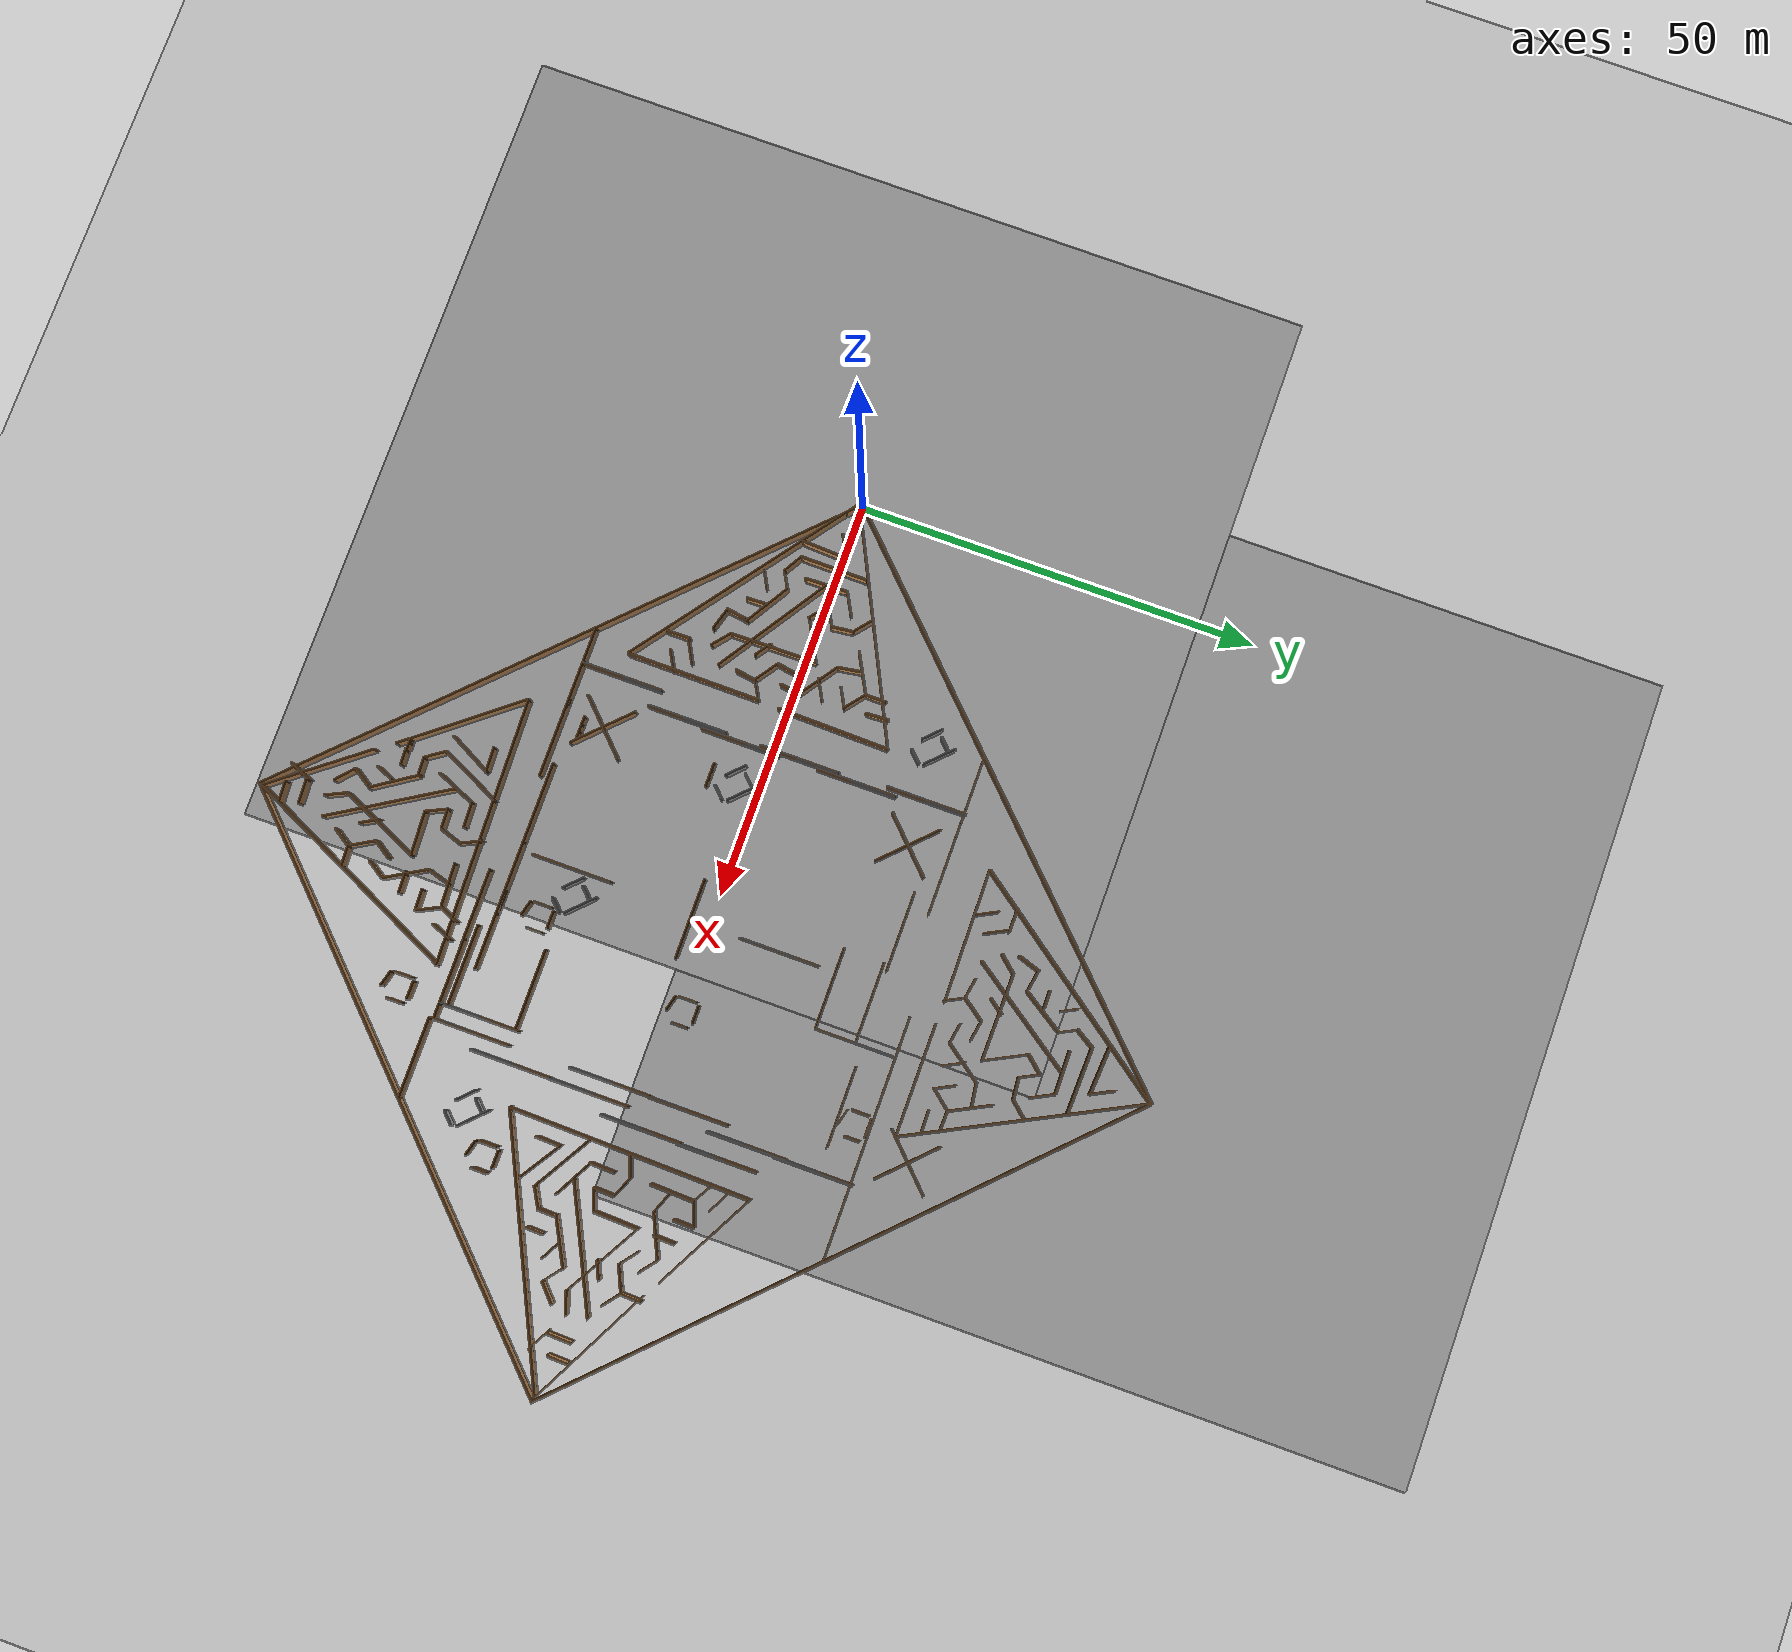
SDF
<sdf version="1.5">
 <world name="__default__">
  <physics name="default_physics" default="0" type="ode">
   <max_step_size>0.001</max_step_size>
   <real_time_factor>1</real_time_factor>
   <real_time_update_rate>1000</real_time_update_rate>
   <gravity>0 0 -9.8</gravity>
   <magnetic_field>5.5645e-06 2.28758e-05 -4.23884e-05</magnetic_field>
  </physics>
  <scene><ambient>0.4 0.4 0.4 1</ambient><background>0.7 0.7 0.7 1</background><shadows>1</shadows></scene>
  <spherical_coordinates>
   <surface_model>EARTH_WGS84</surface_model>
   <latitude_deg>0</latitude_deg>
   <longitude_deg>0</longitude_deg>
   <elevation>0</elevation>
   <heading_deg>0</heading_deg>
  </spherical_coordinates>
  <model name="LoZ">
   <pose>56 -0 0 0 -0 0</pose>
   <link name="Wall_0">
    <collision name="Wall_0_Collision">
     <geometry><box><size>79.346 0.15 2.5</size></box></geometry>
     <pose>0 0 1.25 0 -0 0</pose>
    </collision>
    <visual name="Wall_0_Visual">
     <pose>0 0 1.25 0 -0 0</pose>
     <geometry><box><size>79.346 0.15 2.5</size></box></geometry>
     <material>
      <script><uri>file://media/materials/scripts/gazebo.material</uri><name>Gazebo/Wood</name></script>
      <ambient>1 1 1 1</ambient>
     </material>
    </visual>
    <pose>-28 -28 0 0 0 -0.785398</pose>
   </link>
   <link name="Wall_4">
    <collision name="Wall_4_Collision">
     <geometry><box><size>79.346 0.15 2.5</size></box></geometry>
     <pose>0 0 1.25 0 -0 0</pose>
    </collision>
    <visual name="Wall_4_Visual">
     <pose>0 0 1.25 0 -0 0</pose>
     <geometry><box><size>79.346 0.15 2.5</size></box></geometry>
     <material>
      <script><uri>file://media/materials/scripts/gazebo.material</uri><name>Gazebo/Wood</name></script>
      <ambient>1 1 1 1</ambient>
     </material>
    </visual>
    <pose>-28 28 0 0 -0 0.785398</pose>
   </link>
   <link name="Wall_6">
    <collision name="Wall_6_Collision">
     <geometry><box><size>79.346 0.15 2.5</size></box></geometry>
     <pose>0 0 1.25 0 -0 0</pose>
    </collision>
    <visual name="Wall_6_Visual">
     <pose>0 0 1.25 0 -0 0</pose>
     <geometry><box><size>79.346 0.15 2.5</size></box></geometry>
     <material>
      <script><uri>file://media/materials/scripts/gazebo.material</uri><name>Gazebo/Wood</name></script>
      <ambient>1 1 1 1</ambient>
     </material>
    </visual>
    <pose>28 28 0 0 -0 2.35619</pose>
   </link>
   <link name="Wall_8">
    <collision name="Wall_8_Collision">
     <geometry><box><size>79.346 0.15 2.5</size></box></geometry>
     <pose>0 0 1.25 0 -0 0</pose>
    </collision>
    <visual name="Wall_8_Visual">
     <pose>0 0 1.25 0 -0 0</pose>
     <geometry><box><size>79.346 0.15 2.5</size></box></geometry>
     <material>
      <script><uri>file://media/materials/scripts/gazebo.material</uri><name>Gazebo/Wood</name></script>
      <ambient>1 1 1 1</ambient>
     </material>
    </visual>
    <pose>28 -28 0 0 -0 0.785398</pose>
   </link>
   <static>1</static>
  </model>
  <model name="wall-10m-amodi">
   <pose>31.2626 19.2625 0 0 -0 0</pose>
   <link name="Wall_24">
    <collision name="Wall_24_Collision">
     <geometry><box><size>10 0.15 2.5</size></box></geometry>
     <pose>0 0 1.25 0 -0 0</pose>
    </collision>
    <visual name="Wall_24_Visual">
     <pose>0 0 1.25 0 -0 0</pose>
     <geometry><box><size>10 0.15 2.5</size></box></geometry>
     <material>
      <script><uri>file://media/materials/scripts/gazebo.material</uri><name>Gazebo/Grey</name></script>
      <ambient>1 1 1 1</ambient>
     </material>
    </visual>
    <pose>0 -0 0 0 0 -1.5708</pose>
   </link>
   <link name="Wall_25">
    <collision name="Wall_25_Collision">
     <geometry><box><size>10 0.15 2.5</size></box></geometry>
     <pose>0 0 1.25 0 -0 0</pose>
    </collision>
    <visual name="Wall_25_Visual">
     <pose>0 0 1.25 0 -0 0</pose>
     <geometry><box><size>10 0.15 2.5</size></box></geometry>
     <material>
      <script><uri>file://media/materials/scripts/gazebo.material</uri><name>Gazebo/Wood</name></script>
      <ambient>1 1 1 1</ambient>
     </material>
    </visual>
    <pose>0 -0 0 0 -0 1.5708</pose>
   </link>
   <static>1</static>
  </model>
  <model name="wall-10m-amodi_0">
   <pose>32.051 10.7157 0 0 -0 0</pose>
   <link name="Wall_24">
    <collision name="Wall_24_Collision">
     <geometry><box><size>10 0.15 2.5</size></box></geometry>
     <pose>0 0 1.25 0 -0 0</pose>
    </collision>
    <visual name="Wall_24_Visual">
     <pose>0 0 1.25 0 -0 0</pose>
     <geometry><box><size>10 0.15 2.5</size></box></geometry>
     <material>
      <script><uri>file://media/materials/scripts/gazebo.material</uri><name>Gazebo/Grey</name></script>
      <ambient>1 1 1 1</ambient>
     </material>
    </visual>
    <pose>0 -0 0 0 0 -1.5708</pose>
   </link>
   <link name="Wall_25">
    <collision name="Wall_25_Collision">
     <geometry><box><size>10 0.15 2.5</size></box></geometry>
     <pose>0 0 1.25 0 -0 0</pose>
    </collision>
    <visual name="Wall_25_Visual">
     <pose>0 0 1.25 0 -0 0</pose>
     <geometry><box><size>10 0.15 2.5</size></box></geometry>
     <material>
      <script><uri>file://media/materials/scripts/gazebo.material</uri><name>Gazebo/Wood</name></script>
      <ambient>1 1 1 1</ambient>
     </material>
    </visual>
    <pose>0 -0 0 0 -0 1.5708</pose>
   </link>
   <static>1</static>
  </model>
  <model name="wall-10m-amodi_1">
   <pose>29.4591 -19.9386 0 0 -0 0</pose>
   <link name="Wall_24">
    <collision name="Wall_24_Collision">
     <geometry><box><size>10 0.15 2.5</size></box></geometry>
     <pose>0 0 1.25 0 -0 0</pose>
    </collision>
    <visual name="Wall_24_Visual">
     <pose>0 0 1.25 0 -0 0</pose>
     <geometry><box><size>10 0.15 2.5</size></box></geometry>
     <material>
      <script><uri>file://media/materials/scripts/gazebo.material</uri><name>Gazebo/Grey</name></script>
      <ambient>1 1 1 1</ambient>
     </material>
    </visual>
    <pose>0 -0 0 0 0 -1.5708</pose>
   </link>
   <link name="Wall_25">
    <collision name="Wall_25_Collision">
     <geometry><box><size>10 0.15 2.5</size></box></geometry>
     <pose>0 0 1.25 0 -0 0</pose>
    </collision>
    <visual name="Wall_25_Visual">
     <pose>0 0 1.25 0 -0 0</pose>
     <geometry><box><size>10 0.15 2.5</size></box></geometry>
     <material>
      <script><uri>file://media/materials/scripts/gazebo.material</uri><name>Gazebo/Wood</name></script>
      <ambient>1 1 1 1</ambient>
     </material>
    </visual>
    <pose>0 -0 0 0 -0 1.5708</pose>
   </link>
   <static>1</static>
  </model>
  <model name="wall-10m-amodi_2">
   <pose>31.6636 -10.8812 0 0 -0 0</pose>
   <link name="Wall_24">
    <collision name="Wall_24_Collision">
     <geometry><box><size>10 0.15 2.5</size></box></geometry>
     <pose>0 0 1.25 0 -0 0</pose>
    </collision>
    <visual name="Wall_24_Visual">
     <pose>0 0 1.25 0 -0 0</pose>
     <geometry><box><size>10 0.15 2.5</size></box></geometry>
     <material>
      <script><uri>file://media/materials/scripts/gazebo.material</uri><name>Gazebo/Grey</name></script>
      <ambient>1 1 1 1</ambient>
     </material>
    </visual>
    <pose>0 -0 0 0 0 -1.5708</pose>
   </link>
   <link name="Wall_25">
    <collision name="Wall_25_Collision">
     <geometry><box><size>10 0.15 2.5</size></box></geometry>
     <pose>0 0 1.25 0 -0 0</pose>
    </collision>
    <visual name="Wall_25_Visual">
     <pose>0 0 1.25 0 -0 0</pose>
     <geometry><box><size>10 0.15 2.5</size></box></geometry>
     <material>
      <script><uri>file://media/materials/scripts/gazebo.material</uri><name>Gazebo/Wood</name></script>
      <ambient>1 1 1 1</ambient>
     </material>
    </visual>
    <pose>0 -0 0 0 -0 1.5708</pose>
   </link>
   <static>1</static>
  </model>
  <model name="wall-10m-amodi_3">
   <pose>31.697 3.40181 0 0 -0 0</pose>
   <link name="Wall_24">
    <collision name="Wall_24_Collision">
     <geometry><box><size>10 0.15 2.5</size></box></geometry>
     <pose>0 0 1.25 0 -0 0</pose>
    </collision>
    <visual name="Wall_24_Visual">
     <pose>0 0 1.25 0 -0 0</pose>
     <geometry><box><size>10 0.15 2.5</size></box></geometry>
     <material>
      <script><uri>file://media/materials/scripts/gazebo.material</uri><name>Gazebo/Grey</name></script>
      <ambient>1 1 1 1</ambient>
     </material>
    </visual>
    <pose>0 -0 0 0 0 -1.5708</pose>
   </link>
   <link name="Wall_25">
    <collision name="Wall_25_Collision">
     <geometry><box><size>10 0.15 2.5</size></box></geometry>
     <pose>0 0 1.25 0 -0 0</pose>
    </collision>
    <visual name="Wall_25_Visual">
     <pose>0 0 1.25 0 -0 0</pose>
     <geometry><box><size>10 0.15 2.5</size></box></geometry>
     <material>
      <script><uri>file://media/materials/scripts/gazebo.material</uri><name>Gazebo/Wood</name></script>
      <ambient>1 1 1 1</ambient>
     </material>
    </visual>
    <pose>0 -0 0 0 -0 1.5708</pose>
   </link>
   <static>1</static>
  </model>
  <model name="wall-10m-amodi_4">
   <pose>32.0876 -3.97231 0 0 -0 0</pose>
   <link name="Wall_24">
    <collision name="Wall_24_Collision">
     <geometry><box><size>10 0.15 2.5</size></box></geometry>
     <pose>0 0 1.25 0 -0 0</pose>
    </collision>
    <visual name="Wall_24_Visual">
     <pose>0 0 1.25 0 -0 0</pose>
     <geometry><box><size>10 0.15 2.5</size></box></geometry>
     <material>
      <script><uri>file://media/materials/scripts/gazebo.material</uri><name>Gazebo/Grey</name></script>
      <ambient>1 1 1 1</ambient>
     </material>
    </visual>
    <pose>0 -0 0 0 0 -1.5708</pose>
   </link>
   <link name="Wall_25">
    <collision name="Wall_25_Collision">
     <geometry><box><size>10 0.15 2.5</size></box></geometry>
     <pose>0 0 1.25 0 -0 0</pose>
    </collision>
    <visual name="Wall_25_Visual">
     <pose>0 0 1.25 0 -0 0</pose>
     <geometry><box><size>10 0.15 2.5</size></box></geometry>
     <material>
      <script><uri>file://media/materials/scripts/gazebo.material</uri><name>Gazebo/Wood</name></script>
      <ambient>1 1 1 1</ambient>
     </material>
    </visual>
    <pose>0 -0 0 0 -0 1.5708</pose>
   </link>
   <static>1</static>
  </model>
  <model name="wall-10m-ofoghi">
   <pose>29 24 0 0 -0 0</pose>
   <link name="Wall_22">
    <collision name="Wall_22_Collision">
     <geometry><box><size>10 0.15 2.5</size></box></geometry>
     <pose>0 0 1.25 0 -0 0</pose>
    </collision>
    <visual name="Wall_22_Visual">
     <pose>0 0 1.25 0 -0 0</pose>
     <geometry><box><size>10 0.15 2.5</size></box></geometry>
     <material>
      <script><uri>file://media/materials/scripts/gazebo.material</uri><name>Gazebo/Wood</name></script>
      <ambient>1 1 1 1</ambient>
     </material>
    </visual>
   </link>
   <static>1</static>
  </model>
  <model name="wall-10m-ofoghi_0">
   <pose>39 24 0 0 -0 0</pose>
   <link name="Wall_22">
    <collision name="Wall_22_Collision">
     <geometry><box><size>10 0.15 2.5</size></box></geometry>
     <pose>0 0 1.25 0 -0 0</pose>
    </collision>
    <visual name="Wall_22_Visual">
     <pose>0 0 1.25 0 -0 0</pose>
     <geometry><box><size>10 0.15 2.5</size></box></geometry>
     <material>
      <script><uri>file://media/materials/scripts/gazebo.material</uri><name>Gazebo/Wood</name></script>
      <ambient>1 1 1 1</ambient>
     </material>
    </visual>
   </link>
   <static>1</static>
  </model>
  <model name="wall-10m-ofoghi_1">
   <pose>47 21.5949 0 0 -0 0</pose>
   <link name="Wall_22">
    <collision name="Wall_22_Collision">
     <geometry><box><size>10 0.15 2.5</size></box></geometry>
     <pose>0 0 1.25 0 -0 0</pose>
    </collision>
    <visual name="Wall_22_Visual">
     <pose>0 0 1.25 0 -0 0</pose>
     <geometry><box><size>10 0.15 2.5</size></box></geometry>
     <material>
      <script><uri>file://media/materials/scripts/gazebo.material</uri><name>Gazebo/Wood</name></script>
      <ambient>1 1 1 1</ambient>
     </material>
    </visual>
   </link>
   <static>1</static>
  </model>
  <model name="wall-10m-ofoghi_2">
   <pose>56 21 0 0 -0 0</pose>
   <link name="Wall_22">
    <collision name="Wall_22_Collision">
     <geometry><box><size>10 0.15 2.5</size></box></geometry>
     <pose>0 0 1.25 0 -0 0</pose>
    </collision>
    <visual name="Wall_22_Visual">
     <pose>0 0 1.25 0 -0 0</pose>
     <geometry><box><size>10 0.15 2.5</size></box></geometry>
     <material>
      <script><uri>file://media/materials/scripts/gazebo.material</uri><name>Gazebo/Wood</name></script>
      <ambient>1 1 1 1</ambient>
     </material>
    </visual>
   </link>
   <static>1</static>
  </model>
  <model name="wall-10m-ofoghi_3">
   <pose>81 26 0 0 -0 0</pose>
   <link name="Wall_22">
    <collision name="Wall_22_Collision">
     <geometry><box><size>10 0.15 2.5</size></box></geometry>
     <pose>0 0 1.25 0 -0 0</pose>
    </collision>
    <visual name="Wall_22_Visual">
     <pose>0 0 1.25 0 -0 0</pose>
     <geometry><box><size>10 0.15 2.5</size></box></geometry>
     <material>
      <script><uri>file://media/materials/scripts/gazebo.material</uri><name>Gazebo/Wood</name></script>
      <ambient>1 1 1 1</ambient>
     </material>
    </visual>
   </link>
   <static>1</static>
  </model>
  <model name="wall-10m-ofoghi_4">
   <pose>71 26 0 0 -0 0</pose>
   <link name="Wall_22">
    <collision name="Wall_22_Collision">
     <geometry><box><size>10 0.15 2.5</size></box></geometry>
     <pose>0 0 1.25 0 -0 0</pose>
    </collision>
    <visual name="Wall_22_Visual">
     <pose>0 0 1.25 0 -0 0</pose>
     <geometry><box><size>10 0.15 2.5</size></box></geometry>
     <material>
      <script><uri>file://media/materials/scripts/gazebo.material</uri><name>Gazebo/Wood</name></script>
      <ambient>1 1 1 1</ambient>
     </material>
    </visual>
   </link>
   <static>1</static>
  </model>
  <model name="wall-10m-ofoghi_5">
   <pose>61 26 0 0 -0 0</pose>
   <link name="Wall_22">
    <collision name="Wall_22_Collision">
     <geometry><box><size>10 0.15 2.5</size></box></geometry>
     <pose>0 0 1.25 0 -0 0</pose>
    </collision>
    <visual name="Wall_22_Visual">
     <pose>0 0 1.25 0 -0 0</pose>
     <geometry><box><size>10 0.15 2.5</size></box></geometry>
     <material>
      <script><uri>file://media/materials/scripts/gazebo.material</uri><name>Gazebo/Wood</name></script>
      <ambient>1 1 1 1</ambient>
     </material>
    </visual>
   </link>
   <static>1</static>
  </model>
  <model name="wall-10m-ofoghi_3_clone">
   <pose>30 -25 0 0 -0 0</pose>
   <link name="Wall_22">
    <collision name="Wall_22_Collision">
     <geometry><box><size>10 0.15 2.5</size></box></geometry>
     <pose>0 0 1.25 0 -0 0</pose>
    </collision>
    <visual name="Wall_22_Visual">
     <pose>0 0 1.25 0 -0 0</pose>
     <geometry><box><size>10 0.15 2.5</size></box></geometry>
     <material>
      <script><uri>file://media/materials/scripts/gazebo.material</uri><name>Gazebo/Wood</name></script>
      <ambient>1 1 1 1</ambient>
     </material>
    </visual>
   </link>
   <static>1</static>
  </model>
  <model name="wall-10m-ofoghi_3_clone_0">
   <pose>39 -25 0 0 -0 0</pose>
   <link name="Wall_22">
    <collision name="Wall_22_Collision">
     <geometry><box><size>10 0.15 2.5</size></box></geometry>
     <pose>0 0 1.25 0 -0 0</pose>
    </collision>
    <visual name="Wall_22_Visual">
     <pose>0 0 1.25 0 -0 0</pose>
     <geometry><box><size>10 0.15 2.5</size></box></geometry>
     <material>
      <script><uri>file://media/materials/scripts/gazebo.material</uri><name>Gazebo/Wood</name></script>
      <ambient>1 1 1 1</ambient>
     </material>
    </visual>
   </link>
   <static>1</static>
  </model>
  <model name="wall-10m-ofoghi_3_clone_1">
   <pose>80 -27 0 0 -0 0</pose>
   <link name="Wall_22">
    <collision name="Wall_22_Collision">
     <geometry><box><size>10 0.15 2.5</size></box></geometry>
     <pose>0 0 1.25 0 -0 0</pose>
    </collision>
    <visual name="Wall_22_Visual">
     <pose>0 0 1.25 0 -0 0</pose>
     <geometry><box><size>10 0.15 2.5</size></box></geometry>
     <material>
      <script><uri>file://media/materials/scripts/gazebo.material</uri><name>Gazebo/Wood</name></script>
      <ambient>1 1 1 1</ambient>
     </material>
    </visual>
   </link>
   <static>1</static>
  </model>
  <model name="wall-10m-ofoghi_3_clone_2">
   <pose>70.0318 -26.4863 0 0 -0 0</pose>
   <link name="Wall_22">
    <collision name="Wall_22_Collision">
     <geometry><box><size>10 0.15 2.5</size></box></geometry>
     <pose>0 0 1.25 0 -0 0</pose>
    </collision>
    <visual name="Wall_22_Visual">
     <pose>0 0 1.25 0 -0 0</pose>
     <geometry><box><size>10 0.15 2.5</size></box></geometry>
     <material>
      <script><uri>file://media/materials/scripts/gazebo.material</uri><name>Gazebo/Wood</name></script>
      <ambient>1 1 1 1</ambient>
     </material>
    </visual>
   </link>
   <static>1</static>
  </model>
  <model name="wall-10m-ofoghi_3_clone_3">
   <pose>61.372 -26.5336 0 0 -0 0</pose>
   <link name="Wall_22">
    <collision name="Wall_22_Collision">
     <geometry><box><size>10 0.15 2.5</size></box></geometry>
     <pose>0 0 1.25 0 -0 0</pose>
    </collision>
    <visual name="Wall_22_Visual">
     <pose>0 0 1.25 0 -0 0</pose>
     <geometry><box><size>10 0.15 2.5</size></box></geometry>
     <material>
      <script><uri>file://media/materials/scripts/gazebo.material</uri><name>Gazebo/Wood</name></script>
      <ambient>1 1 1 1</ambient>
     </material>
    </visual>
   </link>
   <static>1</static>
  </model>
  <model name="wall-10m-ofoghi_3_clone_4">
   <pose>47 -24 0 0 -0 0</pose>
   <link name="Wall_22">
    <collision name="Wall_22_Collision">
     <geometry><box><size>10 0.15 2.5</size></box></geometry>
     <pose>0 0 1.25 0 -0 0</pose>
    </collision>
    <visual name="Wall_22_Visual">
     <pose>0 0 1.25 0 -0 0</pose>
     <geometry><box><size>10 0.15 2.5</size></box></geometry>
     <material>
      <script><uri>file://media/materials/scripts/gazebo.material</uri><name>Gazebo/Wood</name></script>
      <ambient>1 1 1 1</ambient>
     </material>
    </visual>
   </link>
   <static>1</static>
  </model>
  <model name="wall-10m-ofoghi_3_clone_5">
   <pose>56 -24 0 0 -0 0</pose>
   <link name="Wall_22">
    <collision name="Wall_22_Collision">
     <geometry><box><size>10 0.15 2.5</size></box></geometry>
     <pose>0 0 1.25 0 -0 0</pose>
    </collision>
    <visual name="Wall_22_Visual">
     <pose>0 0 1.25 0 -0 0</pose>
     <geometry><box><size>10 0.15 2.5</size></box></geometry>
     <material>
      <script><uri>file://media/materials/scripts/gazebo.material</uri><name>Gazebo/Wood</name></script>
      <ambient>1 1 1 1</ambient>
     </material>
    </visual>
   </link>
   <static>1</static>
  </model>
  <model name="wall-10m-ofoghi_3_clone_6">
   <pose>63 -24 0 0 -0 0</pose>
   <link name="Wall_22">
    <collision name="Wall_22_Collision">
     <geometry><box><size>10 0.15 2.5</size></box></geometry>
     <pose>0 0 1.25 0 -0 0</pose>
    </collision>
    <visual name="Wall_22_Visual">
     <pose>0 0 1.25 0 -0 0</pose>
     <geometry><box><size>10 0.15 2.5</size></box></geometry>
     <material>
      <script><uri>file://media/materials/scripts/gazebo.material</uri><name>Gazebo/Wood</name></script>
      <ambient>1 1 1 1</ambient>
     </material>
    </visual>
   </link>
   <static>1</static>
  </model>
  <model name="wall-10m-amodi_2_clone">
   <pose>76.9274 -6.38738 0 0 -0 0</pose>
   <link name="Wall_24">
    <collision name="Wall_24_Collision">
     <geometry><box><size>10 0.15 2.5</size></box></geometry>
     <pose>0 0 1.25 0 -0 0</pose>
    </collision>
    <visual name="Wall_24_Visual">
     <pose>0 0 1.25 0 -0 0</pose>
     <geometry><box><size>10 0.15 2.5</size></box></geometry>
     <material>
      <script><uri>file://media/materials/scripts/gazebo.material</uri><name>Gazebo/Grey</name></script>
      <ambient>1 1 1 1</ambient>
     </material>
    </visual>
    <pose>0 -0 0 0 0 -1.5708</pose>
   </link>
   <link name="Wall_25">
    <collision name="Wall_25_Collision">
     <geometry><box><size>10 0.15 2.5</size></box></geometry>
     <pose>0 0 1.25 0 -0 0</pose>
    </collision>
    <visual name="Wall_25_Visual">
     <pose>0 0 1.25 0 -0 0</pose>
     <geometry><box><size>10 0.15 2.5</size></box></geometry>
     <material>
      <script><uri>file://media/materials/scripts/gazebo.material</uri><name>Gazebo/Wood</name></script>
      <ambient>1 1 1 1</ambient>
     </material>
    </visual>
    <pose>0 -0 0 0 -0 1.5708</pose>
   </link>
   <static>1</static>
  </model>
  <model name="wall-10m-amodi_2_clone_0">
   <pose>76.8913 -16.1637 0 0 -0 0</pose>
   <link name="Wall_24">
    <collision name="Wall_24_Collision">
     <geometry><box><size>10 0.15 2.5</size></box></geometry>
     <pose>0 0 1.25 0 -0 0</pose>
    </collision>
    <visual name="Wall_24_Visual">
     <pose>0 0 1.25 0 -0 0</pose>
     <geometry><box><size>10 0.15 2.5</size></box></geometry>
     <material>
      <script><uri>file://media/materials/scripts/gazebo.material</uri><name>Gazebo/Grey</name></script>
      <ambient>1 1 1 1</ambient>
     </material>
    </visual>
    <pose>0 -0 0 0 0 -1.5708</pose>
   </link>
   <link name="Wall_25">
    <collision name="Wall_25_Collision">
     <geometry><box><size>10 0.15 2.5</size></box></geometry>
     <pose>0 0 1.25 0 -0 0</pose>
    </collision>
    <visual name="Wall_25_Visual">
     <pose>0 0 1.25 0 -0 0</pose>
     <geometry><box><size>10 0.15 2.5</size></box></geometry>
     <material>
      <script><uri>file://media/materials/scripts/gazebo.material</uri><name>Gazebo/Wood</name></script>
      <ambient>1 1 1 1</ambient>
     </material>
    </visual>
    <pose>0 -0 0 0 -0 1.5708</pose>
   </link>
   <static>1</static>
  </model>
  <model name="wall-10m-amodi_2_clone_1">
   <pose>78.8264 0.826129 0 0 -0 0</pose>
   <link name="Wall_24">
    <collision name="Wall_24_Collision">
     <geometry><box><size>10 0.15 2.5</size></box></geometry>
     <pose>0 0 1.25 0 -0 0</pose>
    </collision>
    <visual name="Wall_24_Visual">
     <pose>0 0 1.25 0 -0 0</pose>
     <geometry><box><size>10 0.15 2.5</size></box></geometry>
     <material>
      <script><uri>file://media/materials/scripts/gazebo.material</uri><name>Gazebo/Grey</name></script>
      <ambient>1 1 1 1</ambient>
     </material>
    </visual>
    <pose>0 -0 0 0 0 -1.5708</pose>
   </link>
   <link name="Wall_25">
    <collision name="Wall_25_Collision">
     <geometry><box><size>10 0.15 2.5</size></box></geometry>
     <pose>0 0 1.25 0 -0 0</pose>
    </collision>
    <visual name="Wall_25_Visual">
     <pose>0 0 1.25 0 -0 0</pose>
     <geometry><box><size>10 0.15 2.5</size></box></geometry>
     <material>
      <script><uri>file://media/materials/scripts/gazebo.material</uri><name>Gazebo/Wood</name></script>
      <ambient>1 1 1 1</ambient>
     </material>
    </visual>
    <pose>0 -0 0 0 -0 1.5708</pose>
   </link>
   <static>1</static>
  </model>
  <model name="wall-10m-amodi_2_clone_2">
   <pose>78.9551 10.33 0 0 -0 0</pose>
   <link name="Wall_24">
    <collision name="Wall_24_Collision">
     <geometry><box><size>10 0.15 2.5</size></box></geometry>
     <pose>0 0 1.25 0 -0 0</pose>
    </collision>
    <visual name="Wall_24_Visual">
     <pose>0 0 1.25 0 -0 0</pose>
     <geometry><box><size>10 0.15 2.5</size></box></geometry>
     <material>
      <script><uri>file://media/materials/scripts/gazebo.material</uri><name>Gazebo/Grey</name></script>
      <ambient>1 1 1 1</ambient>
     </material>
    </visual>
    <pose>0 -0 0 0 0 -1.5708</pose>
   </link>
   <link name="Wall_25">
    <collision name="Wall_25_Collision">
     <geometry><box><size>10 0.15 2.5</size></box></geometry>
     <pose>0 0 1.25 0 -0 0</pose>
    </collision>
    <visual name="Wall_25_Visual">
     <pose>0 0 1.25 0 -0 0</pose>
     <geometry><box><size>10 0.15 2.5</size></box></geometry>
     <material>
      <script><uri>file://media/materials/scripts/gazebo.material</uri><name>Gazebo/Wood</name></script>
      <ambient>1 1 1 1</ambient>
     </material>
    </visual>
    <pose>0 -0 0 0 -0 1.5708</pose>
   </link>
   <static>1</static>
  </model>
  <model name="wall-10m-amodi_2_clone_3">
   <pose>75.024 5.31482 0 0 -0 0</pose>
   <link name="Wall_24">
    <collision name="Wall_24_Collision">
     <geometry><box><size>10 0.15 2.5</size></box></geometry>
     <pose>0 0 1.25 0 -0 0</pose>
    </collision>
    <visual name="Wall_24_Visual">
     <pose>0 0 1.25 0 -0 0</pose>
     <geometry><box><size>10 0.15 2.5</size></box></geometry>
     <material>
      <script><uri>file://media/materials/scripts/gazebo.material</uri><name>Gazebo/Grey</name></script>
      <ambient>1 1 1 1</ambient>
     </material>
    </visual>
    <pose>0 -0 0 0 0 -1.5708</pose>
   </link>
   <link name="Wall_25">
    <collision name="Wall_25_Collision">
     <geometry><box><size>10 0.15 2.5</size></box></geometry>
     <pose>0 0 1.25 0 -0 0</pose>
    </collision>
    <visual name="Wall_25_Visual">
     <pose>0 0 1.25 0 -0 0</pose>
     <geometry><box><size>10 0.15 2.5</size></box></geometry>
     <material>
      <script><uri>file://media/materials/scripts/gazebo.material</uri><name>Gazebo/Wood</name></script>
      <ambient>1 1 1 1</ambient>
     </material>
    </visual>
    <pose>0 -0 0 0 -0 1.5708</pose>
   </link>
   <static>1</static>
  </model>
  <model name="wall-10m-amodi_2_clone_4">
   <pose>74.9472 -4.5129 0 0 -0 0</pose>
   <link name="Wall_24">
    <collision name="Wall_24_Collision">
     <geometry><box><size>10 0.15 2.5</size></box></geometry>
     <pose>0 0 1.25 0 -0 0</pose>
    </collision>
    <visual name="Wall_24_Visual">
     <pose>0 0 1.25 0 -0 0</pose>
     <geometry><box><size>10 0.15 2.5</size></box></geometry>
     <material>
      <script><uri>file://media/materials/scripts/gazebo.material</uri><name>Gazebo/Grey</name></script>
      <ambient>1 1 1 1</ambient>
     </material>
    </visual>
    <pose>0 -0 0 0 0 -1.5708</pose>
   </link>
   <link name="Wall_25">
    <collision name="Wall_25_Collision">
     <geometry><box><size>10 0.15 2.5</size></box></geometry>
     <pose>0 0 1.25 0 -0 0</pose>
    </collision>
    <visual name="Wall_25_Visual">
     <pose>0 0 1.25 0 -0 0</pose>
     <geometry><box><size>10 0.15 2.5</size></box></geometry>
     <material>
      <script><uri>file://media/materials/scripts/gazebo.material</uri><name>Gazebo/Wood</name></script>
      <ambient>1 1 1 1</ambient>
     </material>
    </visual>
    <pose>0 -0 0 0 -0 1.5708</pose>
   </link>
   <static>1</static>
  </model>
  <model name="wall-10m-amodi_2_clone_5">
   <pose>76.4715 13.1551 0 0 -0 0</pose>
   <link name="Wall_24">
    <collision name="Wall_24_Collision">
     <geometry><box><size>10 0.15 2.5</size></box></geometry>
     <pose>0 0 1.25 0 -0 0</pose>
    </collision>
    <visual name="Wall_24_Visual">
     <pose>0 0 1.25 0 -0 0</pose>
     <geometry><box><size>10 0.15 2.5</size></box></geometry>
     <material>
      <script><uri>file://media/materials/scripts/gazebo.material</uri><name>Gazebo/Grey</name></script>
      <ambient>1 1 1 1</ambient>
     </material>
    </visual>
    <pose>0 -0 0 0 0 -1.5708</pose>
   </link>
   <link name="Wall_25">
    <collision name="Wall_25_Collision">
     <geometry><box><size>10 0.15 2.5</size></box></geometry>
     <pose>0 0 1.25 0 -0 0</pose>
    </collision>
    <visual name="Wall_25_Visual">
     <pose>0 0 1.25 0 -0 0</pose>
     <geometry><box><size>10 0.15 2.5</size></box></geometry>
     <material>
      <script><uri>file://media/materials/scripts/gazebo.material</uri><name>Gazebo/Wood</name></script>
      <ambient>1 1 1 1</ambient>
     </material>
    </visual>
    <pose>0 -0 0 0 -0 1.5708</pose>
   </link>
   <static>1</static>
  </model>
  <model name="wall-10m-amodi_2_clone_6">
   <pose>76.5849 21.4298 0 0 -0 0</pose>
   <link name="Wall_24">
    <collision name="Wall_24_Collision">
     <geometry><box><size>10 0.15 2.5</size></box></geometry>
     <pose>0 0 1.25 0 -0 0</pose>
    </collision>
    <visual name="Wall_24_Visual">
     <pose>0 0 1.25 0 -0 0</pose>
     <geometry><box><size>10 0.15 2.5</size></box></geometry>
     <material>
      <script><uri>file://media/materials/scripts/gazebo.material</uri><name>Gazebo/Grey</name></script>
      <ambient>1 1 1 1</ambient>
     </material>
    </visual>
    <pose>0 -0 0 0 0 -1.5708</pose>
   </link>
   <link name="Wall_25">
    <collision name="Wall_25_Collision">
     <geometry><box><size>10 0.15 2.5</size></box></geometry>
     <pose>0 0 1.25 0 -0 0</pose>
    </collision>
    <visual name="Wall_25_Visual">
     <pose>0 0 1.25 0 -0 0</pose>
     <geometry><box><size>10 0.15 2.5</size></box></geometry>
     <material>
      <script><uri>file://media/materials/scripts/gazebo.material</uri><name>Gazebo/Wood</name></script>
      <ambient>1 1 1 1</ambient>
     </material>
    </visual>
    <pose>0 -0 0 0 -0 1.5708</pose>
   </link>
   <static>1</static>
  </model>
  <model name="wall-10m-amodi_5">
   <pose>61 21 0 0 -0 0</pose>
   <link name="Wall_24">
    <collision name="Wall_24_Collision">
     <geometry><box><size>10 0.15 2.5</size></box></geometry>
     <pose>0 0 1.25 0 -0 0</pose>
    </collision>
    <visual name="Wall_24_Visual">
     <pose>0 0 1.25 0 -0 0</pose>
     <geometry><box><size>10 0.15 2.5</size></box></geometry>
     <material>
      <script><uri>file://media/materials/scripts/gazebo.material</uri><name>Gazebo/Grey</name></script>
      <ambient>1 1 1 1</ambient>
     </material>
    </visual>
    <pose>0 -0 0 0 0 -1.5708</pose>
   </link>
   <link name="Wall_25">
    <collision name="Wall_25_Collision">
     <geometry><box><size>10 0.15 2.5</size></box></geometry>
     <pose>0 0 1.25 0 -0 0</pose>
    </collision>
    <visual name="Wall_25_Visual">
     <pose>0 0 1.25 0 -0 0</pose>
     <geometry><box><size>10 0.15 2.5</size></box></geometry>
     <material>
      <script><uri>file://media/materials/scripts/gazebo.material</uri><name>Gazebo/Wood</name></script>
      <ambient>1 1 1 1</ambient>
     </material>
    </visual>
    <pose>0 -0 0 0 -0 1.5708</pose>
   </link>
   <static>1</static>
  </model>
  <model name="wall-10m-ofoghi_7">
   <pose>56 16 0 0 -0 0</pose>
   <link name="Wall_22">
    <collision name="Wall_22_Collision">
     <geometry><box><size>10 0.15 2.5</size></box></geometry>
     <pose>0 0 1.25 0 -0 0</pose>
    </collision>
    <visual name="Wall_22_Visual">
     <pose>0 0 1.25 0 -0 0</pose>
     <geometry><box><size>10 0.15 2.5</size></box></geometry>
     <material>
      <script><uri>file://media/materials/scripts/gazebo.material</uri><name>Gazebo/Wood</name></script>
      <ambient>1 1 1 1</ambient>
     </material>
    </visual>
   </link>
   <static>1</static>
  </model>
  <model name="wall-10m-ofoghi_8">
   <pose>68 -25.4857 0 0 -0 0</pose>
   <link name="Wall_22">
    <collision name="Wall_22_Collision">
     <geometry><box><size>10 0.15 2.5</size></box></geometry>
     <pose>0 0 1.25 0 -0 0</pose>
    </collision>
    <visual name="Wall_22_Visual">
     <pose>0 0 1.25 0 -0 0</pose>
     <geometry><box><size>10 0.15 2.5</size></box></geometry>
     <material>
      <script><uri>file://media/materials/scripts/gazebo.material</uri><name>Gazebo/Wood</name></script>
      <ambient>1 1 1 1</ambient>
     </material>
    </visual>
   </link>
   <static>1</static>
  </model>
  <model name="wall-10m-amodi_6">
   <pose>73.0516 -21.5377 0 0 -0 0</pose>
   <link name="Wall_24">
    <collision name="Wall_24_Collision">
     <geometry><box><size>10 0.15 2.5</size></box></geometry>
     <pose>0 0 1.25 0 -0 0</pose>
    </collision>
    <visual name="Wall_24_Visual">
     <pose>0 0 1.25 0 -0 0</pose>
     <geometry><box><size>10 0.15 2.5</size></box></geometry>
     <material>
      <script><uri>file://media/materials/scripts/gazebo.material</uri><name>Gazebo/Grey</name></script>
      <ambient>1 1 1 1</ambient>
     </material>
    </visual>
    <pose>0 -0 0 0 0 -1.5708</pose>
   </link>
   <link name="Wall_25">
    <collision name="Wall_25_Collision">
     <geometry><box><size>10 0.15 2.5</size></box></geometry>
     <pose>0 0 1.25 0 -0 0</pose>
    </collision>
    <visual name="Wall_25_Visual">
     <pose>0 0 1.25 0 -0 0</pose>
     <geometry><box><size>10 0.15 2.5</size></box></geometry>
     <material>
      <script><uri>file://media/materials/scripts/gazebo.material</uri><name>Gazebo/Wood</name></script>
      <ambient>1 1 1 1</ambient>
     </material>
    </visual>
    <pose>0 -0 0 0 -0 1.5708</pose>
   </link>
   <static>1</static>
  </model>
  <model name="wall-10m-ofoghi_9">
   <pose>68 -17 0 0 -0 0</pose>
   <link name="Wall_22">
    <collision name="Wall_22_Collision">
     <geometry><box><size>10 0.15 2.5</size></box></geometry>
     <pose>0 0 1.25 0 -0 0</pose>
    </collision>
    <visual name="Wall_22_Visual">
     <pose>0 0 1.25 0 -0 0</pose>
     <geometry><box><size>10 0.15 2.5</size></box></geometry>
     <material>
      <script><uri>file://media/materials/scripts/gazebo.material</uri><name>Gazebo/Wood</name></script>
      <ambient>1 1 1 1</ambient>
     </material>
    </visual>
   </link>
   <static>1</static>
  </model>
  <model name="tr_layout_1">
   <pose>96.6292 0.322461 0 0 0 -1.58947</pose>
   <link name="Wall_0">
    <collision name="Wall_0_Collision">
     <geometry><box><size>30.15 0.15 2.5</size></box></geometry>
     <pose>0 0 1.25 0 -0 0</pose>
    </collision>
    <visual name="Wall_0_Visual">
     <pose>0 0 1.25 0 -0 0</pose>
     <geometry><box><size>30.15 0.15 2.5</size></box></geometry>
     <material>
      <script><uri>file://media/materials/scripts/gazebo.material</uri><name>Gazebo/Wood</name></script>
      <ambient>1 1 1 1</ambient>
     </material>
    </visual>
    <pose>-0.040638 -14.7092 0 0 -0 0</pose>
   </link>
   <link name="Wall_2">
    <collision name="Wall_2_Collision">
     <geometry><box><size>14.059 0.15 2.5</size></box></geometry>
     <pose>0 0 1.25 0 -0 0</pose>
    </collision>
    <visual name="Wall_2_Visual">
     <pose>0 0 1.25 0 -0 0</pose>
     <geometry><box><size>14.059 0.15 2.5</size></box></geometry>
     <material>
      <script><uri>file://media/materials/scripts/gazebo.material</uri><name>Gazebo/Wood</name></script>
      <ambient>1 1 1 1</ambient>
     </material>
    </visual>
    <pose>-11.8706 -8.51916 0 0 -0 1.0975</pose>
   </link>
   <link name="Wall_4">
    <collision name="Wall_4_Collision">
     <geometry><box><size>33.2446 0.15 2.5</size></box></geometry>
     <pose>0 0 1.25 0 -0 0</pose>
    </collision>
    <visual name="Wall_4_Visual">
     <pose>0 0 1.25 0 -0 0</pose>
     <geometry><box><size>33.2446 0.15 2.5</size></box></geometry>
     <material>
      <script><uri>file://media/materials/scripts/gazebo.material</uri><name>Gazebo/Wood</name></script>
      <ambient>1 1 1 1</ambient>
     </material>
    </visual>
    <pose>7.54073 -0.040527 0 0 0 -1.10039</pose>
   </link>
   <link name="Wall_6">
    <collision name="Wall_6_Collision">
     <geometry><box><size>16.6075 0.15 2.5</size></box></geometry>
     <pose>0 0 1.25 0 -0 0</pose>
    </collision>
    <visual name="Wall_6_Visual">
     <pose>0 0 1.25 0 -0 0</pose>
     <geometry><box><size>16.6075 0.15 2.5</size></box></geometry>
     <material>
      <script><uri>file://media/materials/scripts/gazebo.material</uri><name>Gazebo/Wood</name></script>
      <ambient>1 1 1 1</ambient>
     </material>
    </visual>
    <pose>-3.70064 7.42084 0 0 -0 1.10987</pose>
   </link>
   <static>1</static>
  </model>
  <model name="tr_layout_1_clone">
   <pose>20 -7 0 0 0 -2.68444</pose>
   <link name="Wall_0">
    <collision name="Wall_0_Collision">
     <geometry><box><size>30.15 0.15 2.5</size></box></geometry>
     <pose>0 0 1.25 0 -0 0</pose>
    </collision>
    <visual name="Wall_0_Visual">
     <pose>0 0 1.25 0 -0 0</pose>
     <geometry><box><size>30.15 0.15 2.5</size></box></geometry>
     <material>
      <script><uri>file://media/materials/scripts/gazebo.material</uri><name>Gazebo/Wood</name></script>
      <ambient>1 1 1 1</ambient>
     </material>
    </visual>
    <pose>-0.040638 -14.7092 0 0 -0 0</pose>
   </link>
   <link name="Wall_2">
    <collision name="Wall_2_Collision">
     <geometry><box><size>14.059 0.15 2.5</size></box></geometry>
     <pose>0 0 1.25 0 -0 0</pose>
    </collision>
    <visual name="Wall_2_Visual">
     <pose>0 0 1.25 0 -0 0</pose>
     <geometry><box><size>14.059 0.15 2.5</size></box></geometry>
     <material>
      <script><uri>file://media/materials/scripts/gazebo.material</uri><name>Gazebo/Wood</name></script>
      <ambient>1 1 1 1</ambient>
     </material>
    </visual>
    <pose>-11.8706 -8.51916 0 0 -0 1.0975</pose>
   </link>
   <link name="Wall_4">
    <collision name="Wall_4_Collision">
     <geometry><box><size>33.2446 0.15 2.5</size></box></geometry>
     <pose>0 0 1.25 0 -0 0</pose>
    </collision>
    <visual name="Wall_4_Visual">
     <pose>0 0 1.25 0 -0 0</pose>
     <geometry><box><size>33.2446 0.15 2.5</size></box></geometry>
     <material>
      <script><uri>file://media/materials/scripts/gazebo.material</uri><name>Gazebo/Wood</name></script>
      <ambient>1 1 1 1</ambient>
     </material>
    </visual>
    <pose>7.54073 -0.040527 0 0 0 -1.10039</pose>
   </link>
   <link name="Wall_6">
    <collision name="Wall_6_Collision">
     <geometry><box><size>16.6075 0.15 2.5</size></box></geometry>
     <pose>0 0 1.25 0 -0 0</pose>
    </collision>
    <visual name="Wall_6_Visual">
     <pose>0 0 1.25 0 -0 0</pose>
     <geometry><box><size>16.6075 0.15 2.5</size></box></geometry>
     <material>
      <script><uri>file://media/materials/scripts/gazebo.material</uri><name>Gazebo/Wood</name></script>
      <ambient>1 1 1 1</ambient>
     </material>
    </visual>
    <pose>-3.70064 7.42084 0 0 -0 1.10987</pose>
   </link>
   <static>1</static>
  </model>
  <model name="tr_layout_1_clone_1">
   <pose>49.6932 35.8308 0 0 -0 2.04141</pose>
   <link name="Wall_0">
    <collision name="Wall_0_Collision">
     <geometry><box><size>30.15 0.15 2.5</size></box></geometry>
     <pose>0 0 1.25 0 -0 0</pose>
    </collision>
    <visual name="Wall_0_Visual">
     <pose>0 0 1.25 0 -0 0</pose>
     <geometry><box><size>30.15 0.15 2.5</size></box></geometry>
     <material>
      <script><uri>file://media/materials/scripts/gazebo.material</uri><name>Gazebo/Wood</name></script>
      <ambient>1 1 1 1</ambient>
     </material>
    </visual>
    <pose>-0.040638 -14.7092 0 0 -0 0</pose>
   </link>
   <link name="Wall_2">
    <collision name="Wall_2_Collision">
     <geometry><box><size>14.059 0.15 2.5</size></box></geometry>
     <pose>0 0 1.25 0 -0 0</pose>
    </collision>
    <visual name="Wall_2_Visual">
     <pose>0 0 1.25 0 -0 0</pose>
     <geometry><box><size>14.059 0.15 2.5</size></box></geometry>
     <material>
      <script><uri>file://media/materials/scripts/gazebo.material</uri><name>Gazebo/Wood</name></script>
      <ambient>1 1 1 1</ambient>
     </material>
    </visual>
    <pose>-11.8706 -8.51916 0 0 -0 1.0975</pose>
   </link>
   <link name="Wall_4">
    <collision name="Wall_4_Collision">
     <geometry><box><size>33.2446 0.15 2.5</size></box></geometry>
     <pose>0 0 1.25 0 -0 0</pose>
    </collision>
    <visual name="Wall_4_Visual">
     <pose>0 0 1.25 0 -0 0</pose>
     <geometry><box><size>33.2446 0.15 2.5</size></box></geometry>
     <material>
      <script><uri>file://media/materials/scripts/gazebo.material</uri><name>Gazebo/Wood</name></script>
      <ambient>1 1 1 1</ambient>
     </material>
    </visual>
    <pose>7.54073 -0.040527 0 0 0 -1.10039</pose>
   </link>
   <link name="Wall_6">
    <collision name="Wall_6_Collision">
     <geometry><box><size>16.6075 0.15 2.5</size></box></geometry>
     <pose>0 0 1.25 0 -0 0</pose>
    </collision>
    <visual name="Wall_6_Visual">
     <pose>0 0 1.25 0 -0 0</pose>
     <geometry><box><size>16.6075 0.15 2.5</size></box></geometry>
     <material>
      <script><uri>file://media/materials/scripts/gazebo.material</uri><name>Gazebo/Wood</name></script>
      <ambient>1 1 1 1</ambient>
     </material>
    </visual>
    <pose>-3.70064 7.42084 0 0 -0 1.10987</pose>
   </link>
   <static>1</static>
  </model>
  <model name="wall-10m-amodi_2_clone_4_clone">
   <pose>75 -22 0 0 -0 0</pose>
   <link name="Wall_24">
    <collision name="Wall_24_Collision">
     <geometry><box><size>10 0.15 2.5</size></box></geometry>
     <pose>0 0 1.25 0 -0 0</pose>
    </collision>
    <visual name="Wall_24_Visual">
     <pose>0 0 1.25 0 -0 0</pose>
     <geometry><box><size>10 0.15 2.5</size></box></geometry>
     <material>
      <script><uri>file://media/materials/scripts/gazebo.material</uri><name>Gazebo/Grey</name></script>
      <ambient>1 1 1 1</ambient>
     </material>
    </visual>
    <pose>0 -0 0 0 0 -1.5708</pose>
   </link>
   <link name="Wall_25">
    <collision name="Wall_25_Collision">
     <geometry><box><size>10 0.15 2.5</size></box></geometry>
     <pose>0 0 1.25 0 -0 0</pose>
    </collision>
    <visual name="Wall_25_Visual">
     <pose>0 0 1.25 0 -0 0</pose>
     <geometry><box><size>10 0.15 2.5</size></box></geometry>
     <material>
      <script><uri>file://media/materials/scripts/gazebo.material</uri><name>Gazebo/Wood</name></script>
      <ambient>1 1 1 1</ambient>
     </material>
    </visual>
    <pose>0 -0 0 0 -0 1.5708</pose>
   </link>
   <static>1</static>
  </model>
  <model name="tr_maze_4">
   <pose>94.3115 0.976283 0 0 0 -1.6021</pose>
   <link name="Wall_0">
    <collision name="Wall_0_Collision">
     <geometry><box><size>2.92308 0.15 2.5</size></box></geometry>
     <pose>0 0 1.25 0 -0 0</pose>
    </collision>
    <visual name="Wall_0_Visual">
     <pose>0 0 1.25 0 -0 0</pose>
     <geometry><box><size>2.92308 0.15 2.5</size></box></geometry>
     <material>
      <script><uri>file://media/materials/scripts/gazebo.material</uri><name>Gazebo/Wood</name></script>
      <ambient>1 1 1 1</ambient>
     </material>
    </visual>
    <pose>-11.0014 -10.9997 0 0 -0 1.12328</pose>
   </link>
   <link name="Wall_10">
    <collision name="Wall_10_Collision">
     <geometry><box><size>3.12321 0.15 2.5</size></box></geometry>
     <pose>0 0 1.25 0 -0 0</pose>
    </collision>
    <visual name="Wall_10_Visual">
     <pose>0 0 1.25 0 -0 0</pose>
     <geometry><box><size>3.12321 0.15 2.5</size></box></geometry>
     <material>
      <script><uri>file://media/materials/scripts/gazebo.material</uri><name>Gazebo/Wood</name></script>
      <ambient>1 1 1 1</ambient>
     </material>
    </visual>
    <pose>-4.90142 -8.64967 0 0 -0 1.22777</pose>
   </link>
   <link name="Wall_12">
    <collision name="Wall_12_Collision">
     <geometry><box><size>5.74017 0.15 2.5</size></box></geometry>
     <pose>0 0 1.25 0 -0 0</pose>
    </collision>
    <visual name="Wall_12_Visual">
     <pose>0 0 1.25 0 -0 0</pose>
     <geometry><box><size>5.74017 0.15 2.5</size></box></geometry>
     <material>
      <script><uri>file://media/materials/scripts/gazebo.material</uri><name>Gazebo/Wood</name></script>
      <ambient>0.996078 0.47451 0.0196078 1</ambient>
     </material>
    </visual>
    <pose>-5.65142 -4.74967 0 0 -0 2.03444</pose>
   </link>
   <link name="Wall_14">
    <collision name="Wall_14_Collision">
     <geometry><box><size>2.75 0.15 2.5</size></box></geometry>
     <pose>0 0 1.25 0 -0 0</pose>
    </collision>
    <visual name="Wall_14_Visual">
     <pose>0 0 1.25 0 -0 0</pose>
     <geometry><box><size>2.75 0.15 2.5</size></box></geometry>
     <material>
      <script><uri>file://media/materials/scripts/gazebo.material</uri><name>Gazebo/Wood</name></script>
      <ambient>0.996078 0.47451 0.0196078 1</ambient>
     </material>
    </visual>
    <pose>-6.70142 -4.74967 0 0 -0 3.14159</pose>
   </link>
   <link name="Wall_16">
    <collision name="Wall_16_Collision">
     <geometry><box><size>2.65 0.15 2.5</size></box></geometry>
     <pose>0 0 1.25 0 -0 0</pose>
    </collision>
    <visual name="Wall_16_Visual">
     <pose>0 0 1.25 0 -0 0</pose>
     <geometry><box><size>2.65 0.15 2.5</size></box></geometry>
     <material>
      <script><uri>file://media/materials/scripts/gazebo.material</uri><name>Gazebo/Wood</name></script>
      <ambient>0.996078 0.47451 0.0196078 1</ambient>
     </material>
    </visual>
    <pose>-6.15142 -1.24967 0 0 -0 0.927295</pose>
   </link>
   <link name="Wall_18">
    <collision name="Wall_18_Collision">
     <geometry><box><size>2.65 0.15 2.5</size></box></geometry>
     <pose>0 0 1.25 0 -0 0</pose>
    </collision>
    <visual name="Wall_18_Visual">
     <pose>0 0 1.25 0 -0 0</pose>
     <geometry><box><size>2.65 0.15 2.5</size></box></geometry>
     <material>
      <script><uri>file://media/materials/scripts/gazebo.material</uri><name>Gazebo/Wood</name></script>
      <ambient>0.996078 0.47451 0.0196078 1</ambient>
     </material>
    </visual>
    <pose>-3.65142 -1.24967 0 0 -0 0.927295</pose>
   </link>
   <link name="Wall_2">
    <collision name="Wall_2_Collision">
     <geometry><box><size>2.65599 0.15 2.5</size></box></geometry>
     <pose>0 0 1.25 0 -0 0</pose>
    </collision>
    <visual name="Wall_2_Visual">
     <pose>0 0 1.25 0 -0 0</pose>
     <geometry><box><size>2.65599 0.15 2.5</size></box></geometry>
     <material>
      <script><uri>file://media/materials/scripts/gazebo.material</uri><name>Gazebo/Wood</name></script>
      <ambient>1 1 1 1</ambient>
     </material>
    </visual>
    <pose>-8.80142 -11.1497 0 0 -0 1.07145</pose>
   </link>
   <link name="Wall_20">
    <collision name="Wall_20_Collision">
     <geometry><box><size>3.5041 0.15 2.5</size></box></geometry>
     <pose>0 0 1.25 0 -0 0</pose>
    </collision>
    <visual name="Wall_20_Visual">
     <pose>0 0 1.25 0 -0 0</pose>
     <geometry><box><size>3.5041 0.15 2.5</size></box></geometry>
     <material>
      <script><uri>file://media/materials/scripts/gazebo.material</uri><name>Gazebo/Wood</name></script>
      <ambient>0.996078 0.47451 0.0196078 1</ambient>
     </material>
    </visual>
    <pose>-3.65142 1.25033 0 0 -0 2.03444</pose>
   </link>
   <link name="Wall_22">
    <collision name="Wall_22_Collision">
     <geometry><box><size>2.65 0.15 2.5</size></box></geometry>
     <pose>0 0 1.25 0 -0 0</pose>
    </collision>
    <visual name="Wall_22_Visual">
     <pose>0 0 1.25 0 -0 0</pose>
     <geometry><box><size>2.65 0.15 2.5</size></box></geometry>
     <material>
      <script><uri>file://media/materials/scripts/gazebo.material</uri><name>Gazebo/Wood</name></script>
      <ambient>0.996078 0.47451 0.0196078 1</ambient>
     </material>
    </visual>
    <pose>-3.65142 3.75034 0 0 -0 0.927295</pose>
   </link>
   <link name="Wall_24">
    <collision name="Wall_24_Collision">
     <geometry><box><size>2.65 0.15 2.5</size></box></geometry>
     <pose>0 0 1.25 0 -0 0</pose>
    </collision>
    <visual name="Wall_24_Visual">
     <pose>0 0 1.25 0 -0 0</pose>
     <geometry><box><size>2.65 0.15 2.5</size></box></geometry>
     <material>
      <script><uri>file://media/materials/scripts/gazebo.material</uri><name>Gazebo/Wood</name></script>
      <ambient>0.996078 0.47451 0.0196078 1</ambient>
     </material>
    </visual>
    <pose>-5.65142 2.75034 0 0 -0 3.14159</pose>
   </link>
   <link name="Wall_26">
    <collision name="Wall_26_Collision">
     <geometry><box><size>2.84258 0.15 2.5</size></box></geometry>
     <pose>0 0 1.25 0 -0 0</pose>
    </collision>
    <visual name="Wall_26_Visual">
     <pose>0 0 1.25 0 -0 0</pose>
     <geometry><box><size>2.84258 0.15 2.5</size></box></geometry>
     <material>
      <script><uri>file://media/materials/scripts/gazebo.material</uri><name>Gazebo/Wood</name></script>
      <ambient>1 1 1 1</ambient>
     </material>
    </visual>
    <pose>0.098585 -10.9997 0 0 -0 1.9513</pose>
   </link>
   <link name="Wall_28">
    <collision name="Wall_28_Collision">
     <geometry><box><size>2.84258 0.15 2.5</size></box></geometry>
     <pose>0 0 1.25 0 -0 0</pose>
    </collision>
    <visual name="Wall_28_Visual">
     <pose>0 0 1.25 0 -0 0</pose>
     <geometry><box><size>2.84258 0.15 2.5</size></box></geometry>
     <material>
      <script><uri>file://media/materials/scripts/gazebo.material</uri><name>Gazebo/Wood</name></script>
      <ambient>1 1 1 1</ambient>
     </material>
    </visual>
    <pose>0.098585 -8.49967 0 0 -0 1.19029</pose>
   </link>
   <link name="Wall_30">
    <collision name="Wall_30_Collision">
     <geometry><box><size>2.65 0.15 2.5</size></box></geometry>
     <pose>0 0 1.25 0 -0 0</pose>
    </collision>
    <visual name="Wall_30_Visual">
     <pose>0 0 1.25 0 -0 0</pose>
     <geometry><box><size>2.65 0.15 2.5</size></box></geometry>
     <material>
      <script><uri>file://media/materials/scripts/gazebo.material</uri><name>Gazebo/Wood</name></script>
      <ambient>1 1 1 1</ambient>
     </material>
    </visual>
    <pose>1.84858 -7.24967 0 0 -0 0</pose>
   </link>
   <link name="Wall_32">
    <collision name="Wall_32_Collision">
     <geometry><box><size>2.84258 0.15 2.5</size></box></geometry>
     <pose>0 0 1.25 0 -0 0</pose>
    </collision>
    <visual name="Wall_32_Visual">
     <pose>0 0 1.25 0 -0 0</pose>
     <geometry><box><size>2.84258 0.15 2.5</size></box></geometry>
     <material>
      <script><uri>file://media/materials/scripts/gazebo.material</uri><name>Gazebo/Wood</name></script>
      <ambient>1 1 1 1</ambient>
     </material>
    </visual>
    <pose>2.59858 -5.99967 0 0 -0 1.9513</pose>
   </link>
   <link name="Wall_34">
    <collision name="Wall_34_Collision">
     <geometry><box><size>5.65 0.15 2.5</size></box></geometry>
     <pose>0 0 1.25 0 -0 0</pose>
    </collision>
    <visual name="Wall_34_Visual">
     <pose>0 0 1.25 0 -0 0</pose>
     <geometry><box><size>5.65 0.15 2.5</size></box></geometry>
     <material>
      <script><uri>file://media/materials/scripts/gazebo.material</uri><name>Gazebo/Wood</name></script>
      <ambient>1 1 1 1</ambient>
     </material>
    </visual>
    <pose>-0.651415 -4.74967 0 0 -0 3.14159</pose>
   </link>
   <link name="Wall_36">
    <collision name="Wall_36_Collision">
     <geometry><box><size>10.8855 0.15 2.5</size></box></geometry>
     <pose>0 0 1.25 0 -0 0</pose>
    </collision>
    <visual name="Wall_36_Visual">
     <pose>0 0 1.25 0 -0 0</pose>
     <geometry><box><size>10.8855 0.15 2.5</size></box></geometry>
     <material>
      <script><uri>file://media/materials/scripts/gazebo.material</uri><name>Gazebo/Wood</name></script>
      <ambient>0.996078 0.47451 0.0196078 1</ambient>
     </material>
    </visual>
    <pose>-0.901415 0.000335 0 0 -0 1.08632</pose>
   </link>
   <link name="Wall_38">
    <collision name="Wall_38_Collision">
     <geometry><box><size>2.38607 0.15 2.5</size></box></geometry>
     <pose>0 0 1.25 0 -0 0</pose>
    </collision>
    <visual name="Wall_38_Visual">
     <pose>0 0 1.25 0 -0 0</pose>
     <geometry><box><size>2.38607 0.15 2.5</size></box></geometry>
     <material>
      <script><uri>file://media/materials/scripts/gazebo.material</uri><name>Gazebo/Wood</name></script>
      <ambient>0.996078 0.47451 0.0196078 1</ambient>
     </material>
    </visual>
    <pose>-0.901415 1.25033 0 0 -0 2.03444</pose>
   </link>
   <link name="Wall_4">
    <collision name="Wall_4_Collision">
     <geometry><box><size>5.45 0.15 2.5</size></box></geometry>
     <pose>0 0 1.25 0 -0 0</pose>
    </collision>
    <visual name="Wall_4_Visual">
     <pose>0 0 1.25 0 -0 0</pose>
     <geometry><box><size>5.45 0.15 2.5</size></box></geometry>
     <material>
      <script><uri>file://media/materials/scripts/gazebo.material</uri><name>Gazebo/Wood</name></script>
      <ambient>1 1 1 1</ambient>
     </material>
    </visual>
    <pose>-5.55142 -10.0497 0 0 -0 0</pose>
   </link>
   <link name="Wall_40">
    <collision name="Wall_40_Collision">
     <geometry><box><size>2.84258 0.15 2.5</size></box></geometry>
     <pose>0 0 1.25 0 -0 0</pose>
    </collision>
    <visual name="Wall_40_Visual">
     <pose>0 0 1.25 0 -0 0</pose>
     <geometry><box><size>2.84258 0.15 2.5</size></box></geometry>
     <material>
      <script><uri>file://media/materials/scripts/gazebo.material</uri><name>Gazebo/Wood</name></script>
      <ambient>0.996078 0.47451 0.0196078 1</ambient>
     </material>
    </visual>
    <pose>1.09858 6.00033 0 0 -0 1.9513</pose>
   </link>
   <link name="Wall_42">
    <collision name="Wall_42_Collision">
     <geometry><box><size>16.0324 0.15 2.5</size></box></geometry>
     <pose>0 0 1.25 0 -0 0</pose>
    </collision>
    <visual name="Wall_42_Visual">
     <pose>0 0 1.25 0 -0 0</pose>
     <geometry><box><size>16.0324 0.15 2.5</size></box></geometry>
     <material>
      <script><uri>file://media/materials/scripts/gazebo.material</uri><name>Gazebo/Wood</name></script>
      <ambient>0.996078 0.47451 0.0196078 1</ambient>
     </material>
    </visual>
    <pose>1.84858 -0.249665 0 0 -0 2.06261</pose>
   </link>
   <link name="Wall_44">
    <collision name="Wall_44_Collision">
     <geometry><box><size>5.29296 0.15 2.5</size></box></geometry>
     <pose>0 0 1.25 0 -0 0</pose>
    </collision>
    <visual name="Wall_44_Visual">
     <pose>0 0 1.25 0 -0 0</pose>
     <geometry><box><size>5.29296 0.15 2.5</size></box></geometry>
     <material>
      <script><uri>file://media/materials/scripts/gazebo.material</uri><name>Gazebo/Wood</name></script>
      <ambient>1 1 1 1</ambient>
     </material>
    </visual>
    <pose>5.74858 -7.34966 0 0 -0 1.10715</pose>
   </link>
   <link name="Wall_46">
    <collision name="Wall_46_Collision">
     <geometry><box><size>3.15 0.15 2.5</size></box></geometry>
     <pose>0 0 1.25 0 -0 0</pose>
    </collision>
    <visual name="Wall_46_Visual">
     <pose>0 0 1.25 0 -0 0</pose>
     <geometry><box><size>3.15 0.15 2.5</size></box></geometry>
     <material>
      <script><uri>file://media/materials/scripts/gazebo.material</uri><name>Gazebo/Wood</name></script>
      <ambient>1 1 1 1</ambient>
     </material>
    </visual>
    <pose>3.09858 -9.74967 0 0 -0 3.14159</pose>
   </link>
   <link name="Wall_48">
    <collision name="Wall_48_Collision">
     <geometry><box><size>8.47406 0.15 2.5</size></box></geometry>
     <pose>0 0 1.25 0 -0 0</pose>
    </collision>
    <visual name="Wall_48_Visual">
     <pose>0 0 1.25 0 -0 0</pose>
     <geometry><box><size>8.47406 0.15 2.5</size></box></geometry>
     <material>
      <script><uri>file://media/materials/scripts/gazebo.material</uri><name>Gazebo/Wood</name></script>
      <ambient>1 1 1 1</ambient>
     </material>
    </visual>
    <pose>7.59858 -8.59966 0 0 -0 1.06953</pose>
   </link>
   <link name="Wall_50">
    <collision name="Wall_50_Collision">
     <geometry><box><size>2.84258 0.15 2.5</size></box></geometry>
     <pose>0 0 1.25 0 -0 0</pose>
    </collision>
    <visual name="Wall_50_Visual">
     <pose>0 0 1.25 0 -0 0</pose>
     <geometry><box><size>2.84258 0.15 2.5</size></box></geometry>
     <material>
      <script><uri>file://media/materials/scripts/gazebo.material</uri><name>Gazebo/Wood</name></script>
      <ambient>1 1 1 1</ambient>
     </material>
    </visual>
    <pose>8.89858 -3.79967 0 0 -0 2.11759</pose>
   </link>
   <link name="Wall_52">
    <collision name="Wall_52_Collision">
     <geometry><box><size>2.25 0.15 2.5</size></box></geometry>
     <pose>0 0 1.25 0 -0 0</pose>
    </collision>
    <visual name="Wall_52_Visual">
     <pose>0 0 1.25 0 -0 0</pose>
     <geometry><box><size>2.25 0.15 2.5</size></box></geometry>
     <material>
      <script><uri>file://media/materials/scripts/gazebo.material</uri><name>Gazebo/Wood</name></script>
      <ambient>1 1 1 1</ambient>
     </material>
    </visual>
    <pose>7.14858 -2.64966 0 0 -0 3.14159</pose>
   </link>
   <link name="Wall_54">
    <collision name="Wall_54_Collision">
     <geometry><box><size>6.25 0.15 2.5</size></box></geometry>
     <pose>0 0 1.25 0 -0 0</pose>
    </collision>
    <visual name="Wall_54_Visual">
     <pose>0 0 1.25 0 -0 0</pose>
     <geometry><box><size>6.25 0.15 2.5</size></box></geometry>
     <material>
      <script><uri>file://media/materials/scripts/gazebo.material</uri><name>Gazebo/Wood</name></script>
      <ambient>1 1 1 1</ambient>
     </material>
    </visual>
    <pose>4.42709 -0.065034 0 0 -0 2.0944</pose>
   </link>
   <link name="Wall_56">
    <collision name="Wall_56_Collision">
     <geometry><box><size>2.65 0.15 2.5</size></box></geometry>
     <pose>0 0 1.25 0 -0 0</pose>
    </collision>
    <visual name="Wall_56_Visual">
     <pose>0 0 1.25 0 -0 0</pose>
     <geometry><box><size>2.65 0.15 2.5</size></box></geometry>
     <material>
      <script><uri>file://media/materials/scripts/gazebo.material</uri><name>Gazebo/Wood</name></script>
      <ambient>1 1 1 1</ambient>
     </material>
    </visual>
    <pose>3.84858 3.75034 0 0 -0 0.927295</pose>
   </link>
   <link name="Wall_58">
    <collision name="Wall_58_Collision">
     <geometry><box><size>2.97843 0.15 2.5</size></box></geometry>
     <pose>0 0 1.25 0 -0 0</pose>
    </collision>
    <visual name="Wall_58_Visual">
     <pose>0 0 1.25 0 -0 0</pose>
     <geometry><box><size>2.97843 0.15 2.5</size></box></geometry>
     <material>
      <script><uri>file://media/materials/scripts/gazebo.material</uri><name>Gazebo/Wood</name></script>
      <ambient>1 1 1 1</ambient>
     </material>
    </visual>
    <pose>3.59858 5.75033 0 0 -0 2.35619</pose>
   </link>
   <link name="Wall_6">
    <collision name="Wall_6_Collision">
     <geometry><box><size>3.19631 0.15 2.5</size></box></geometry>
     <pose>0 0 1.25 0 -0 0</pose>
    </collision>
    <visual name="Wall_6_Visual">
     <pose>0 0 1.25 0 -0 0</pose>
     <geometry><box><size>3.19631 0.15 2.5</size></box></geometry>
     <material>
      <script><uri>file://media/materials/scripts/gazebo.material</uri><name>Gazebo/Wood</name></script>
      <ambient>1 1 1 1</ambient>
     </material>
    </visual>
    <pose>-8.80142 -8.64967 0 0 -0 1.97569</pose>
   </link>
   <link name="Wall_60">
    <collision name="Wall_60_Collision">
     <geometry><box><size>3.15 0.15 2.5</size></box></geometry>
     <pose>0 0 1.25 0 -0 0</pose>
    </collision>
    <visual name="Wall_60_Visual">
     <pose>0 0 1.25 0 -0 0</pose>
     <geometry><box><size>3.15 0.15 2.5</size></box></geometry>
     <material>
      <script><uri>file://media/materials/scripts/gazebo.material</uri><name>Gazebo/Wood</name></script>
      <ambient>1 1 1 1</ambient>
     </material>
    </visual>
    <pose>10.0986 -10.2497 0 0 -0 3.14159</pose>
   </link>
   <link name="Wall_62">
    <collision name="Wall_62_Collision">
     <geometry><box><size>5.98095 0.15 2.5</size></box></geometry>
     <pose>0 0 1.25 0 -0 0</pose>
    </collision>
    <visual name="Wall_62_Visual">
     <pose>0 0 1.25 0 -0 0</pose>
     <geometry><box><size>5.98095 0.15 2.5</size></box></geometry>
     <material>
      <script><uri>file://media/materials/scripts/gazebo.material</uri><name>Gazebo/Wood</name></script>
      <ambient>1 1 1 1</ambient>
     </material>
    </visual>
    <pose>10.0986 -7.74967 0 0 -0 1.03038</pose>
   </link>
   <link name="Wall_64">
    <collision name="Wall_64_Collision">
     <geometry><box><size>2.15 0.15 2.5</size></box></geometry>
     <pose>0 0 1.25 0 -0 0</pose>
    </collision>
    <visual name="Wall_64_Visual">
     <pose>0 0 1.25 0 -0 0</pose>
     <geometry><box><size>2.15 0.15 2.5</size></box></geometry>
     <material>
      <script><uri>file://media/materials/scripts/gazebo.material</uri><name>Gazebo/Wood</name></script>
      <ambient>1 1 1 1</ambient>
     </material>
    </visual>
    <pose>7.59858 -0.249665 0 0 -0 3.14159</pose>
   </link>
   <link name="Wall_66">
    <collision name="Wall_66_Collision">
     <geometry><box><size>2.9678 0.15 2.5</size></box></geometry>
     <pose>0 0 1.25 0 -0 0</pose>
    </collision>
    <visual name="Wall_66_Visual">
     <pose>0 0 1.25 0 -0 0</pose>
     <geometry><box><size>2.9678 0.15 2.5</size></box></geometry>
     <material>
      <script><uri>file://media/materials/scripts/gazebo.material</uri><name>Gazebo/Wood</name></script>
      <ambient>0.996078 0.47451 0.0196078 1</ambient>
     </material>
    </visual>
    <pose>2.44859 11.0003 0 0 0 -2.05032</pose>
   </link>
   <link name="Wall_68">
    <collision name="Wall_68_Collision">
     <geometry><box><size>3.15 0.15 2.5</size></box></geometry>
     <pose>0 0 1.25 0 -0 0</pose>
    </collision>
    <visual name="Wall_68_Visual">
     <pose>0 0 1.25 0 -0 0</pose>
     <geometry><box><size>3.15 0.15 2.5</size></box></geometry>
     <material>
      <script><uri>file://media/materials/scripts/gazebo.material</uri><name>Gazebo/Wood</name></script>
      <ambient>0.996078 0.47451 0.0196078 1</ambient>
     </material>
    </visual>
    <pose>0.298584 9.95034 0 0 -0 3.14159</pose>
   </link>
   <link name="Wall_70">
    <collision name="Wall_70_Collision">
     <geometry><box><size>2.65 0.15 2.5</size></box></geometry>
     <pose>0 0 1.25 0 -0 0</pose>
    </collision>
    <visual name="Wall_70_Visual">
     <pose>0 0 1.25 0 -0 0</pose>
     <geometry><box><size>2.65 0.15 2.5</size></box></geometry>
     <material>
      <script><uri>file://media/materials/scripts/gazebo.material</uri><name>Gazebo/Wood</name></script>
      <ambient>1 1 1 1</ambient>
     </material>
    </visual>
    <pose>-0.451416 12.2503 0 0 -0 3.14159</pose>
   </link>
   <link name="Wall_72">
    <collision name="Wall_72_Collision">
     <geometry><box><size>2.38607 0.15 2.5</size></box></geometry>
     <pose>0 0 1.25 0 -0 0</pose>
    </collision>
    <visual name="Wall_72_Visual">
     <pose>0 0 1.25 0 -0 0</pose>
     <geometry><box><size>2.38607 0.15 2.5</size></box></geometry>
     <material>
      <script><uri>file://media/materials/scripts/gazebo.material</uri><name>Gazebo/Wood</name></script>
      <ambient>1 1 1 1</ambient>
     </material>
    </visual>
    <pose>5.09858 1.25033 0 0 -0 1.10715</pose>
   </link>
   <link name="Wall_8">
    <collision name="Wall_8_Collision">
     <geometry><box><size>2.65 0.15 2.5</size></box></geometry>
     <pose>0 0 1.25 0 -0 0</pose>
    </collision>
    <visual name="Wall_8_Visual">
     <pose>0 0 1.25 0 -0 0</pose>
     <geometry><box><size>2.65 0.15 2.5</size></box></geometry>
     <material>
      <script><uri>file://media/materials/scripts/gazebo.material</uri><name>Gazebo/Wood</name></script>
      <ambient>1 1 1 1</ambient>
     </material>
    </visual>
    <pose>-8.15142 -7.24967 0 0 -0 0</pose>
   </link>
   <static>1</static>
  </model>
  <model name="tr_maze_4_clone">
   <pose>52.1155 36.5366 0 0 -0 2.04317</pose>
   <link name="Wall_0">
    <collision name="Wall_0_Collision">
     <geometry><box><size>2.92308 0.15 2.5</size></box></geometry>
     <pose>0 0 1.25 0 -0 0</pose>
    </collision>
    <visual name="Wall_0_Visual">
     <pose>0 0 1.25 0 -0 0</pose>
     <geometry><box><size>2.92308 0.15 2.5</size></box></geometry>
     <material>
      <script><uri>file://media/materials/scripts/gazebo.material</uri><name>Gazebo/Wood</name></script>
      <ambient>1 1 1 1</ambient>
     </material>
    </visual>
    <pose>-11.0014 -10.9997 0 0 -0 1.12328</pose>
   </link>
   <link name="Wall_10">
    <collision name="Wall_10_Collision">
     <geometry><box><size>3.12321 0.15 2.5</size></box></geometry>
     <pose>0 0 1.25 0 -0 0</pose>
    </collision>
    <visual name="Wall_10_Visual">
     <pose>0 0 1.25 0 -0 0</pose>
     <geometry><box><size>3.12321 0.15 2.5</size></box></geometry>
     <material>
      <script><uri>file://media/materials/scripts/gazebo.material</uri><name>Gazebo/Wood</name></script>
      <ambient>1 1 1 1</ambient>
     </material>
    </visual>
    <pose>-4.90142 -8.64967 0 0 -0 1.22777</pose>
   </link>
   <link name="Wall_12">
    <collision name="Wall_12_Collision">
     <geometry><box><size>5.74017 0.15 2.5</size></box></geometry>
     <pose>0 0 1.25 0 -0 0</pose>
    </collision>
    <visual name="Wall_12_Visual">
     <pose>0 0 1.25 0 -0 0</pose>
     <geometry><box><size>5.74017 0.15 2.5</size></box></geometry>
     <material>
      <script><uri>file://media/materials/scripts/gazebo.material</uri><name>Gazebo/Wood</name></script>
      <ambient>0.996078 0.47451 0.0196078 1</ambient>
     </material>
    </visual>
    <pose>-5.65142 -4.74967 0 0 -0 2.03444</pose>
   </link>
   <link name="Wall_14">
    <collision name="Wall_14_Collision">
     <geometry><box><size>2.75 0.15 2.5</size></box></geometry>
     <pose>0 0 1.25 0 -0 0</pose>
    </collision>
    <visual name="Wall_14_Visual">
     <pose>0 0 1.25 0 -0 0</pose>
     <geometry><box><size>2.75 0.15 2.5</size></box></geometry>
     <material>
      <script><uri>file://media/materials/scripts/gazebo.material</uri><name>Gazebo/Wood</name></script>
      <ambient>0.996078 0.47451 0.0196078 1</ambient>
     </material>
    </visual>
    <pose>-6.70142 -4.74967 0 0 -0 3.14159</pose>
   </link>
   <link name="Wall_16">
    <collision name="Wall_16_Collision">
     <geometry><box><size>2.65 0.15 2.5</size></box></geometry>
     <pose>0 0 1.25 0 -0 0</pose>
    </collision>
    <visual name="Wall_16_Visual">
     <pose>0 0 1.25 0 -0 0</pose>
     <geometry><box><size>2.65 0.15 2.5</size></box></geometry>
     <material>
      <script><uri>file://media/materials/scripts/gazebo.material</uri><name>Gazebo/Wood</name></script>
      <ambient>0.996078 0.47451 0.0196078 1</ambient>
     </material>
    </visual>
    <pose>-6.15142 -1.24967 0 0 -0 0.927295</pose>
   </link>
   <link name="Wall_18">
    <collision name="Wall_18_Collision">
     <geometry><box><size>2.65 0.15 2.5</size></box></geometry>
     <pose>0 0 1.25 0 -0 0</pose>
    </collision>
    <visual name="Wall_18_Visual">
     <pose>0 0 1.25 0 -0 0</pose>
     <geometry><box><size>2.65 0.15 2.5</size></box></geometry>
     <material>
      <script><uri>file://media/materials/scripts/gazebo.material</uri><name>Gazebo/Wood</name></script>
      <ambient>0.996078 0.47451 0.0196078 1</ambient>
     </material>
    </visual>
    <pose>-3.65142 -1.24967 0 0 -0 0.927295</pose>
   </link>
   <link name="Wall_2">
    <collision name="Wall_2_Collision">
     <geometry><box><size>2.65599 0.15 2.5</size></box></geometry>
     <pose>0 0 1.25 0 -0 0</pose>
    </collision>
    <visual name="Wall_2_Visual">
     <pose>0 0 1.25 0 -0 0</pose>
     <geometry><box><size>2.65599 0.15 2.5</size></box></geometry>
     <material>
      <script><uri>file://media/materials/scripts/gazebo.material</uri><name>Gazebo/Wood</name></script>
      <ambient>1 1 1 1</ambient>
     </material>
    </visual>
    <pose>-8.80142 -11.1497 0 0 -0 1.07145</pose>
   </link>
   <link name="Wall_20">
    <collision name="Wall_20_Collision">
     <geometry><box><size>3.5041 0.15 2.5</size></box></geometry>
     <pose>0 0 1.25 0 -0 0</pose>
    </collision>
    <visual name="Wall_20_Visual">
     <pose>0 0 1.25 0 -0 0</pose>
     <geometry><box><size>3.5041 0.15 2.5</size></box></geometry>
     <material>
      <script><uri>file://media/materials/scripts/gazebo.material</uri><name>Gazebo/Wood</name></script>
      <ambient>0.996078 0.47451 0.0196078 1</ambient>
     </material>
    </visual>
    <pose>-3.65142 1.25033 0 0 -0 2.03444</pose>
   </link>
   <link name="Wall_22">
    <collision name="Wall_22_Collision">
     <geometry><box><size>2.65 0.15 2.5</size></box></geometry>
     <pose>0 0 1.25 0 -0 0</pose>
    </collision>
    <visual name="Wall_22_Visual">
     <pose>0 0 1.25 0 -0 0</pose>
     <geometry><box><size>2.65 0.15 2.5</size></box></geometry>
     <material>
      <script><uri>file://media/materials/scripts/gazebo.material</uri><name>Gazebo/Wood</name></script>
      <ambient>0.996078 0.47451 0.0196078 1</ambient>
     </material>
    </visual>
    <pose>-3.65142 3.75034 0 0 -0 0.927295</pose>
   </link>
   <link name="Wall_24">
    <collision name="Wall_24_Collision">
     <geometry><box><size>2.65 0.15 2.5</size></box></geometry>
     <pose>0 0 1.25 0 -0 0</pose>
    </collision>
    <visual name="Wall_24_Visual">
     <pose>0 0 1.25 0 -0 0</pose>
     <geometry><box><size>2.65 0.15 2.5</size></box></geometry>
     <material>
      <script><uri>file://media/materials/scripts/gazebo.material</uri><name>Gazebo/Wood</name></script>
      <ambient>0.996078 0.47451 0.0196078 1</ambient>
     </material>
    </visual>
    <pose>-5.65142 2.75034 0 0 -0 3.14159</pose>
   </link>
   <link name="Wall_26">
    <collision name="Wall_26_Collision">
     <geometry><box><size>2.84258 0.15 2.5</size></box></geometry>
     <pose>0 0 1.25 0 -0 0</pose>
    </collision>
    <visual name="Wall_26_Visual">
     <pose>0 0 1.25 0 -0 0</pose>
     <geometry><box><size>2.84258 0.15 2.5</size></box></geometry>
     <material>
      <script><uri>file://media/materials/scripts/gazebo.material</uri><name>Gazebo/Wood</name></script>
      <ambient>1 1 1 1</ambient>
     </material>
    </visual>
    <pose>0.098585 -10.9997 0 0 -0 1.9513</pose>
   </link>
   <link name="Wall_28">
    <collision name="Wall_28_Collision">
     <geometry><box><size>2.84258 0.15 2.5</size></box></geometry>
     <pose>0 0 1.25 0 -0 0</pose>
    </collision>
    <visual name="Wall_28_Visual">
     <pose>0 0 1.25 0 -0 0</pose>
     <geometry><box><size>2.84258 0.15 2.5</size></box></geometry>
     <material>
      <script><uri>file://media/materials/scripts/gazebo.material</uri><name>Gazebo/Wood</name></script>
      <ambient>1 1 1 1</ambient>
     </material>
    </visual>
    <pose>0.098585 -8.49967 0 0 -0 1.19029</pose>
   </link>
   <link name="Wall_30">
    <collision name="Wall_30_Collision">
     <geometry><box><size>2.65 0.15 2.5</size></box></geometry>
     <pose>0 0 1.25 0 -0 0</pose>
    </collision>
    <visual name="Wall_30_Visual">
     <pose>0 0 1.25 0 -0 0</pose>
     <geometry><box><size>2.65 0.15 2.5</size></box></geometry>
     <material>
      <script><uri>file://media/materials/scripts/gazebo.material</uri><name>Gazebo/Wood</name></script>
      <ambient>1 1 1 1</ambient>
     </material>
    </visual>
    <pose>1.84858 -7.24967 0 0 -0 0</pose>
   </link>
   <link name="Wall_32">
    <collision name="Wall_32_Collision">
     <geometry><box><size>2.84258 0.15 2.5</size></box></geometry>
     <pose>0 0 1.25 0 -0 0</pose>
    </collision>
    <visual name="Wall_32_Visual">
     <pose>0 0 1.25 0 -0 0</pose>
     <geometry><box><size>2.84258 0.15 2.5</size></box></geometry>
     <material>
      <script><uri>file://media/materials/scripts/gazebo.material</uri><name>Gazebo/Wood</name></script>
      <ambient>1 1 1 1</ambient>
     </material>
    </visual>
    <pose>2.59858 -5.99967 0 0 -0 1.9513</pose>
   </link>
   <link name="Wall_34">
    <collision name="Wall_34_Collision">
     <geometry><box><size>5.65 0.15 2.5</size></box></geometry>
     <pose>0 0 1.25 0 -0 0</pose>
    </collision>
    <visual name="Wall_34_Visual">
     <pose>0 0 1.25 0 -0 0</pose>
     <geometry><box><size>5.65 0.15 2.5</size></box></geometry>
     <material>
      <script><uri>file://media/materials/scripts/gazebo.material</uri><name>Gazebo/Wood</name></script>
      <ambient>1 1 1 1</ambient>
     </material>
    </visual>
    <pose>-0.651415 -4.74967 0 0 -0 3.14159</pose>
   </link>
   <link name="Wall_36">
    <collision name="Wall_36_Collision">
     <geometry><box><size>10.8855 0.15 2.5</size></box></geometry>
     <pose>0 0 1.25 0 -0 0</pose>
    </collision>
    <visual name="Wall_36_Visual">
     <pose>0 0 1.25 0 -0 0</pose>
     <geometry><box><size>10.8855 0.15 2.5</size></box></geometry>
     <material>
      <script><uri>file://media/materials/scripts/gazebo.material</uri><name>Gazebo/Wood</name></script>
      <ambient>0.996078 0.47451 0.0196078 1</ambient>
     </material>
    </visual>
    <pose>-0.901415 0.000335 0 0 -0 1.08632</pose>
   </link>
   <link name="Wall_38">
    <collision name="Wall_38_Collision">
     <geometry><box><size>2.38607 0.15 2.5</size></box></geometry>
     <pose>0 0 1.25 0 -0 0</pose>
    </collision>
    <visual name="Wall_38_Visual">
     <pose>0 0 1.25 0 -0 0</pose>
     <geometry><box><size>2.38607 0.15 2.5</size></box></geometry>
     <material>
      <script><uri>file://media/materials/scripts/gazebo.material</uri><name>Gazebo/Wood</name></script>
      <ambient>0.996078 0.47451 0.0196078 1</ambient>
     </material>
    </visual>
    <pose>-0.901415 1.25033 0 0 -0 2.03444</pose>
   </link>
   <link name="Wall_4">
    <collision name="Wall_4_Collision">
     <geometry><box><size>5.45 0.15 2.5</size></box></geometry>
     <pose>0 0 1.25 0 -0 0</pose>
    </collision>
    <visual name="Wall_4_Visual">
     <pose>0 0 1.25 0 -0 0</pose>
     <geometry><box><size>5.45 0.15 2.5</size></box></geometry>
     <material>
      <script><uri>file://media/materials/scripts/gazebo.material</uri><name>Gazebo/Wood</name></script>
      <ambient>1 1 1 1</ambient>
     </material>
    </visual>
    <pose>-5.55142 -10.0497 0 0 -0 0</pose>
   </link>
   <link name="Wall_40">
    <collision name="Wall_40_Collision">
     <geometry><box><size>2.84258 0.15 2.5</size></box></geometry>
     <pose>0 0 1.25 0 -0 0</pose>
    </collision>
    <visual name="Wall_40_Visual">
     <pose>0 0 1.25 0 -0 0</pose>
     <geometry><box><size>2.84258 0.15 2.5</size></box></geometry>
     <material>
      <script><uri>file://media/materials/scripts/gazebo.material</uri><name>Gazebo/Wood</name></script>
      <ambient>0.996078 0.47451 0.0196078 1</ambient>
     </material>
    </visual>
    <pose>1.09858 6.00033 0 0 -0 1.9513</pose>
   </link>
   <link name="Wall_42">
    <collision name="Wall_42_Collision">
     <geometry><box><size>16.0324 0.15 2.5</size></box></geometry>
     <pose>0 0 1.25 0 -0 0</pose>
    </collision>
    <visual name="Wall_42_Visual">
     <pose>0 0 1.25 0 -0 0</pose>
     <geometry><box><size>16.0324 0.15 2.5</size></box></geometry>
     <material>
      <script><uri>file://media/materials/scripts/gazebo.material</uri><name>Gazebo/Wood</name></script>
      <ambient>0.996078 0.47451 0.0196078 1</ambient>
     </material>
    </visual>
    <pose>1.84858 -0.249665 0 0 -0 2.06261</pose>
   </link>
   <link name="Wall_44">
    <collision name="Wall_44_Collision">
     <geometry><box><size>5.29296 0.15 2.5</size></box></geometry>
     <pose>0 0 1.25 0 -0 0</pose>
    </collision>
    <visual name="Wall_44_Visual">
     <pose>0 0 1.25 0 -0 0</pose>
     <geometry><box><size>5.29296 0.15 2.5</size></box></geometry>
     <material>
      <script><uri>file://media/materials/scripts/gazebo.material</uri><name>Gazebo/Wood</name></script>
      <ambient>1 1 1 1</ambient>
     </material>
    </visual>
    <pose>5.74858 -7.34966 0 0 -0 1.10715</pose>
   </link>
   <link name="Wall_46">
    <collision name="Wall_46_Collision">
     <geometry><box><size>3.15 0.15 2.5</size></box></geometry>
     <pose>0 0 1.25 0 -0 0</pose>
    </collision>
    <visual name="Wall_46_Visual">
     <pose>0 0 1.25 0 -0 0</pose>
     <geometry><box><size>3.15 0.15 2.5</size></box></geometry>
     <material>
      <script><uri>file://media/materials/scripts/gazebo.material</uri><name>Gazebo/Wood</name></script>
      <ambient>1 1 1 1</ambient>
     </material>
    </visual>
    <pose>3.09858 -9.74967 0 0 -0 3.14159</pose>
   </link>
   <link name="Wall_48">
    <collision name="Wall_48_Collision">
     <geometry><box><size>8.47406 0.15 2.5</size></box></geometry>
     <pose>0 0 1.25 0 -0 0</pose>
    </collision>
    <visual name="Wall_48_Visual">
     <pose>0 0 1.25 0 -0 0</pose>
     <geometry><box><size>8.47406 0.15 2.5</size></box></geometry>
     <material>
      <script><uri>file://media/materials/scripts/gazebo.material</uri><name>Gazebo/Wood</name></script>
      <ambient>1 1 1 1</ambient>
     </material>
    </visual>
    <pose>7.59858 -8.59966 0 0 -0 1.06953</pose>
   </link>
   <link name="Wall_50">
    <collision name="Wall_50_Collision">
     <geometry><box><size>2.84258 0.15 2.5</size></box></geometry>
     <pose>0 0 1.25 0 -0 0</pose>
    </collision>
    <visual name="Wall_50_Visual">
     <pose>0 0 1.25 0 -0 0</pose>
     <geometry><box><size>2.84258 0.15 2.5</size></box></geometry>
     <material>
      <script><uri>file://media/materials/scripts/gazebo.material</uri><name>Gazebo/Wood</name></script>
      <ambient>1 1 1 1</ambient>
     </material>
    </visual>
    <pose>8.89858 -3.79967 0 0 -0 2.11759</pose>
   </link>
   <link name="Wall_52">
    <collision name="Wall_52_Collision">
     <geometry><box><size>2.25 0.15 2.5</size></box></geometry>
     <pose>0 0 1.25 0 -0 0</pose>
    </collision>
    <visual name="Wall_52_Visual">
     <pose>0 0 1.25 0 -0 0</pose>
     <geometry><box><size>2.25 0.15 2.5</size></box></geometry>
     <material>
      <script><uri>file://media/materials/scripts/gazebo.material</uri><name>Gazebo/Wood</name></script>
      <ambient>1 1 1 1</ambient>
     </material>
    </visual>
    <pose>7.14858 -2.64966 0 0 -0 3.14159</pose>
   </link>
   <link name="Wall_54">
    <collision name="Wall_54_Collision">
     <geometry><box><size>6.25 0.15 2.5</size></box></geometry>
     <pose>0 0 1.25 0 -0 0</pose>
    </collision>
    <visual name="Wall_54_Visual">
     <pose>0 0 1.25 0 -0 0</pose>
     <geometry><box><size>6.25 0.15 2.5</size></box></geometry>
     <material>
      <script><uri>file://media/materials/scripts/gazebo.material</uri><name>Gazebo/Wood</name></script>
      <ambient>1 1 1 1</ambient>
     </material>
    </visual>
    <pose>4.42709 -0.065034 0 0 -0 2.0944</pose>
   </link>
   <link name="Wall_56">
    <collision name="Wall_56_Collision">
     <geometry><box><size>2.65 0.15 2.5</size></box></geometry>
     <pose>0 0 1.25 0 -0 0</pose>
    </collision>
    <visual name="Wall_56_Visual">
     <pose>0 0 1.25 0 -0 0</pose>
     <geometry><box><size>2.65 0.15 2.5</size></box></geometry>
     <material>
      <script><uri>file://media/materials/scripts/gazebo.material</uri><name>Gazebo/Wood</name></script>
      <ambient>1 1 1 1</ambient>
     </material>
    </visual>
    <pose>3.84858 3.75034 0 0 -0 0.927295</pose>
   </link>
   <link name="Wall_58">
    <collision name="Wall_58_Collision">
     <geometry><box><size>2.97843 0.15 2.5</size></box></geometry>
     <pose>0 0 1.25 0 -0 0</pose>
    </collision>
    <visual name="Wall_58_Visual">
     <pose>0 0 1.25 0 -0 0</pose>
     <geometry><box><size>2.97843 0.15 2.5</size></box></geometry>
     <material>
      <script><uri>file://media/materials/scripts/gazebo.material</uri><name>Gazebo/Wood</name></script>
      <ambient>1 1 1 1</ambient>
     </material>
    </visual>
    <pose>3.59858 5.75033 0 0 -0 2.35619</pose>
   </link>
   <link name="Wall_6">
    <collision name="Wall_6_Collision">
     <geometry><box><size>3.19631 0.15 2.5</size></box></geometry>
     <pose>0 0 1.25 0 -0 0</pose>
    </collision>
    <visual name="Wall_6_Visual">
     <pose>0 0 1.25 0 -0 0</pose>
     <geometry><box><size>3.19631 0.15 2.5</size></box></geometry>
     <material>
      <script><uri>file://media/materials/scripts/gazebo.material</uri><name>Gazebo/Wood</name></script>
      <ambient>1 1 1 1</ambient>
     </material>
    </visual>
    <pose>-8.80142 -8.64967 0 0 -0 1.97569</pose>
   </link>
   <link name="Wall_60">
    <collision name="Wall_60_Collision">
     <geometry><box><size>3.15 0.15 2.5</size></box></geometry>
     <pose>0 0 1.25 0 -0 0</pose>
    </collision>
    <visual name="Wall_60_Visual">
     <pose>0 0 1.25 0 -0 0</pose>
     <geometry><box><size>3.15 0.15 2.5</size></box></geometry>
     <material>
      <script><uri>file://media/materials/scripts/gazebo.material</uri><name>Gazebo/Wood</name></script>
      <ambient>1 1 1 1</ambient>
     </material>
    </visual>
    <pose>10.0986 -10.2497 0 0 -0 3.14159</pose>
   </link>
   <link name="Wall_62">
    <collision name="Wall_62_Collision">
     <geometry><box><size>5.98095 0.15 2.5</size></box></geometry>
     <pose>0 0 1.25 0 -0 0</pose>
    </collision>
    <visual name="Wall_62_Visual">
     <pose>0 0 1.25 0 -0 0</pose>
     <geometry><box><size>5.98095 0.15 2.5</size></box></geometry>
     <material>
      <script><uri>file://media/materials/scripts/gazebo.material</uri><name>Gazebo/Wood</name></script>
      <ambient>1 1 1 1</ambient>
     </material>
    </visual>
    <pose>10.0986 -7.74967 0 0 -0 1.03038</pose>
   </link>
   <link name="Wall_64">
    <collision name="Wall_64_Collision">
     <geometry><box><size>2.15 0.15 2.5</size></box></geometry>
     <pose>0 0 1.25 0 -0 0</pose>
    </collision>
    <visual name="Wall_64_Visual">
     <pose>0 0 1.25 0 -0 0</pose>
     <geometry><box><size>2.15 0.15 2.5</size></box></geometry>
     <material>
      <script><uri>file://media/materials/scripts/gazebo.material</uri><name>Gazebo/Wood</name></script>
      <ambient>1 1 1 1</ambient>
     </material>
    </visual>
    <pose>7.59858 -0.249665 0 0 -0 3.14159</pose>
   </link>
   <link name="Wall_66">
    <collision name="Wall_66_Collision">
     <geometry><box><size>2.9678 0.15 2.5</size></box></geometry>
     <pose>0 0 1.25 0 -0 0</pose>
    </collision>
    <visual name="Wall_66_Visual">
     <pose>0 0 1.25 0 -0 0</pose>
     <geometry><box><size>2.9678 0.15 2.5</size></box></geometry>
     <material>
      <script><uri>file://media/materials/scripts/gazebo.material</uri><name>Gazebo/Wood</name></script>
      <ambient>0.996078 0.47451 0.0196078 1</ambient>
     </material>
    </visual>
    <pose>2.44859 11.0003 0 0 0 -2.05032</pose>
   </link>
   <link name="Wall_68">
    <collision name="Wall_68_Collision">
     <geometry><box><size>3.15 0.15 2.5</size></box></geometry>
     <pose>0 0 1.25 0 -0 0</pose>
    </collision>
    <visual name="Wall_68_Visual">
     <pose>0 0 1.25 0 -0 0</pose>
     <geometry><box><size>3.15 0.15 2.5</size></box></geometry>
     <material>
      <script><uri>file://media/materials/scripts/gazebo.material</uri><name>Gazebo/Wood</name></script>
      <ambient>0.996078 0.47451 0.0196078 1</ambient>
     </material>
    </visual>
    <pose>0.298584 9.95034 0 0 -0 3.14159</pose>
   </link>
   <link name="Wall_70">
    <collision name="Wall_70_Collision">
     <geometry><box><size>2.65 0.15 2.5</size></box></geometry>
     <pose>0 0 1.25 0 -0 0</pose>
    </collision>
    <visual name="Wall_70_Visual">
     <pose>0 0 1.25 0 -0 0</pose>
     <geometry><box><size>2.65 0.15 2.5</size></box></geometry>
     <material>
      <script><uri>file://media/materials/scripts/gazebo.material</uri><name>Gazebo/Wood</name></script>
      <ambient>1 1 1 1</ambient>
     </material>
    </visual>
    <pose>-0.451416 12.2503 0 0 -0 3.14159</pose>
   </link>
   <link name="Wall_72">
    <collision name="Wall_72_Collision">
     <geometry><box><size>2.38607 0.15 2.5</size></box></geometry>
     <pose>0 0 1.25 0 -0 0</pose>
    </collision>
    <visual name="Wall_72_Visual">
     <pose>0 0 1.25 0 -0 0</pose>
     <geometry><box><size>2.38607 0.15 2.5</size></box></geometry>
     <material>
      <script><uri>file://media/materials/scripts/gazebo.material</uri><name>Gazebo/Wood</name></script>
      <ambient>1 1 1 1</ambient>
     </material>
    </visual>
    <pose>5.09858 1.25033 0 0 -0 1.10715</pose>
   </link>
   <link name="Wall_8">
    <collision name="Wall_8_Collision">
     <geometry><box><size>2.65 0.15 2.5</size></box></geometry>
     <pose>0 0 1.25 0 -0 0</pose>
    </collision>
    <visual name="Wall_8_Visual">
     <pose>0 0 1.25 0 -0 0</pose>
     <geometry><box><size>2.65 0.15 2.5</size></box></geometry>
     <material>
      <script><uri>file://media/materials/scripts/gazebo.material</uri><name>Gazebo/Wood</name></script>
      <ambient>1 1 1 1</ambient>
     </material>
    </visual>
    <pose>-8.15142 -7.24967 0 0 -0 0</pose>
   </link>
   <static>1</static>
  </model>
  <model name="tr_maze_4_clone_0">
   <pose>19.3157 -4.57073 0 0 0 -2.64571</pose>
   <link name="Wall_0">
    <collision name="Wall_0_Collision">
     <geometry><box><size>2.92308 0.15 2.5</size></box></geometry>
     <pose>0 0 1.25 0 -0 0</pose>
    </collision>
    <visual name="Wall_0_Visual">
     <pose>0 0 1.25 0 -0 0</pose>
     <geometry><box><size>2.92308 0.15 2.5</size></box></geometry>
     <material>
      <script><uri>file://media/materials/scripts/gazebo.material</uri><name>Gazebo/Wood</name></script>
      <ambient>1 1 1 1</ambient>
     </material>
    </visual>
    <pose>-11.0014 -10.9997 0 0 -0 1.12328</pose>
   </link>
   <link name="Wall_10">
    <collision name="Wall_10_Collision">
     <geometry><box><size>3.12321 0.15 2.5</size></box></geometry>
     <pose>0 0 1.25 0 -0 0</pose>
    </collision>
    <visual name="Wall_10_Visual">
     <pose>0 0 1.25 0 -0 0</pose>
     <geometry><box><size>3.12321 0.15 2.5</size></box></geometry>
     <material>
      <script><uri>file://media/materials/scripts/gazebo.material</uri><name>Gazebo/Wood</name></script>
      <ambient>1 1 1 1</ambient>
     </material>
    </visual>
    <pose>-4.90142 -8.64967 0 0 -0 1.22777</pose>
   </link>
   <link name="Wall_12">
    <collision name="Wall_12_Collision">
     <geometry><box><size>5.74017 0.15 2.5</size></box></geometry>
     <pose>0 0 1.25 0 -0 0</pose>
    </collision>
    <visual name="Wall_12_Visual">
     <pose>0 0 1.25 0 -0 0</pose>
     <geometry><box><size>5.74017 0.15 2.5</size></box></geometry>
     <material>
      <script><uri>file://media/materials/scripts/gazebo.material</uri><name>Gazebo/Wood</name></script>
      <ambient>0.996078 0.47451 0.0196078 1</ambient>
     </material>
    </visual>
    <pose>-5.65142 -4.74967 0 0 -0 2.03444</pose>
   </link>
   <link name="Wall_14">
    <collision name="Wall_14_Collision">
     <geometry><box><size>2.75 0.15 2.5</size></box></geometry>
     <pose>0 0 1.25 0 -0 0</pose>
    </collision>
    <visual name="Wall_14_Visual">
     <pose>0 0 1.25 0 -0 0</pose>
     <geometry><box><size>2.75 0.15 2.5</size></box></geometry>
     <material>
      <script><uri>file://media/materials/scripts/gazebo.material</uri><name>Gazebo/Wood</name></script>
      <ambient>0.996078 0.47451 0.0196078 1</ambient>
     </material>
    </visual>
    <pose>-6.70142 -4.74967 0 0 -0 3.14159</pose>
   </link>
   <link name="Wall_16">
    <collision name="Wall_16_Collision">
     <geometry><box><size>2.65 0.15 2.5</size></box></geometry>
     <pose>0 0 1.25 0 -0 0</pose>
    </collision>
    <visual name="Wall_16_Visual">
     <pose>0 0 1.25 0 -0 0</pose>
     <geometry><box><size>2.65 0.15 2.5</size></box></geometry>
     <material>
      <script><uri>file://media/materials/scripts/gazebo.material</uri><name>Gazebo/Wood</name></script>
      <ambient>0.996078 0.47451 0.0196078 1</ambient>
     </material>
    </visual>
    <pose>-6.15142 -1.24967 0 0 -0 0.927295</pose>
   </link>
   <link name="Wall_18">
    <collision name="Wall_18_Collision">
     <geometry><box><size>2.65 0.15 2.5</size></box></geometry>
     <pose>0 0 1.25 0 -0 0</pose>
    </collision>
    <visual name="Wall_18_Visual">
     <pose>0 0 1.25 0 -0 0</pose>
     <geometry><box><size>2.65 0.15 2.5</size></box></geometry>
     <material>
      <script><uri>file://media/materials/scripts/gazebo.material</uri><name>Gazebo/Wood</name></script>
      <ambient>0.996078 0.47451 0.0196078 1</ambient>
     </material>
    </visual>
    <pose>-3.65142 -1.24967 0 0 -0 0.927295</pose>
   </link>
   <link name="Wall_2">
    <collision name="Wall_2_Collision">
     <geometry><box><size>2.65599 0.15 2.5</size></box></geometry>
     <pose>0 0 1.25 0 -0 0</pose>
    </collision>
    <visual name="Wall_2_Visual">
     <pose>0 0 1.25 0 -0 0</pose>
     <geometry><box><size>2.65599 0.15 2.5</size></box></geometry>
     <material>
      <script><uri>file://media/materials/scripts/gazebo.material</uri><name>Gazebo/Wood</name></script>
      <ambient>1 1 1 1</ambient>
     </material>
    </visual>
    <pose>-8.80142 -11.1497 0 0 -0 1.07145</pose>
   </link>
   <link name="Wall_20">
    <collision name="Wall_20_Collision">
     <geometry><box><size>3.5041 0.15 2.5</size></box></geometry>
     <pose>0 0 1.25 0 -0 0</pose>
    </collision>
    <visual name="Wall_20_Visual">
     <pose>0 0 1.25 0 -0 0</pose>
     <geometry><box><size>3.5041 0.15 2.5</size></box></geometry>
     <material>
      <script><uri>file://media/materials/scripts/gazebo.material</uri><name>Gazebo/Wood</name></script>
      <ambient>0.996078 0.47451 0.0196078 1</ambient>
     </material>
    </visual>
    <pose>-3.65142 1.25033 0 0 -0 2.03444</pose>
   </link>
   <link name="Wall_22">
    <collision name="Wall_22_Collision">
     <geometry><box><size>2.65 0.15 2.5</size></box></geometry>
     <pose>0 0 1.25 0 -0 0</pose>
    </collision>
    <visual name="Wall_22_Visual">
     <pose>0 0 1.25 0 -0 0</pose>
     <geometry><box><size>2.65 0.15 2.5</size></box></geometry>
     <material>
      <script><uri>file://media/materials/scripts/gazebo.material</uri><name>Gazebo/Wood</name></script>
      <ambient>0.996078 0.47451 0.0196078 1</ambient>
     </material>
    </visual>
    <pose>-3.65142 3.75034 0 0 -0 0.927295</pose>
   </link>
   <link name="Wall_24">
    <collision name="Wall_24_Collision">
     <geometry><box><size>2.65 0.15 2.5</size></box></geometry>
     <pose>0 0 1.25 0 -0 0</pose>
    </collision>
    <visual name="Wall_24_Visual">
     <pose>0 0 1.25 0 -0 0</pose>
     <geometry><box><size>2.65 0.15 2.5</size></box></geometry>
     <material>
      <script><uri>file://media/materials/scripts/gazebo.material</uri><name>Gazebo/Wood</name></script>
      <ambient>0.996078 0.47451 0.0196078 1</ambient>
     </material>
    </visual>
    <pose>-5.65142 2.75034 0 0 -0 3.14159</pose>
   </link>
   <link name="Wall_26">
    <collision name="Wall_26_Collision">
     <geometry><box><size>2.84258 0.15 2.5</size></box></geometry>
     <pose>0 0 1.25 0 -0 0</pose>
    </collision>
    <visual name="Wall_26_Visual">
     <pose>0 0 1.25 0 -0 0</pose>
     <geometry><box><size>2.84258 0.15 2.5</size></box></geometry>
     <material>
      <script><uri>file://media/materials/scripts/gazebo.material</uri><name>Gazebo/Wood</name></script>
      <ambient>1 1 1 1</ambient>
     </material>
    </visual>
    <pose>0.098585 -10.9997 0 0 -0 1.9513</pose>
   </link>
   <link name="Wall_28">
    <collision name="Wall_28_Collision">
     <geometry><box><size>2.84258 0.15 2.5</size></box></geometry>
     <pose>0 0 1.25 0 -0 0</pose>
    </collision>
    <visual name="Wall_28_Visual">
     <pose>0 0 1.25 0 -0 0</pose>
     <geometry><box><size>2.84258 0.15 2.5</size></box></geometry>
     <material>
      <script><uri>file://media/materials/scripts/gazebo.material</uri><name>Gazebo/Wood</name></script>
      <ambient>1 1 1 1</ambient>
     </material>
    </visual>
    <pose>0.098585 -8.49967 0 0 -0 1.19029</pose>
   </link>
   <link name="Wall_30">
    <collision name="Wall_30_Collision">
     <geometry><box><size>2.65 0.15 2.5</size></box></geometry>
     <pose>0 0 1.25 0 -0 0</pose>
    </collision>
    <visual name="Wall_30_Visual">
     <pose>0 0 1.25 0 -0 0</pose>
     <geometry><box><size>2.65 0.15 2.5</size></box></geometry>
     <material>
      <script><uri>file://media/materials/scripts/gazebo.material</uri><name>Gazebo/Wood</name></script>
      <ambient>1 1 1 1</ambient>
     </material>
    </visual>
    <pose>1.84858 -7.24967 0 0 -0 0</pose>
   </link>
   <link name="Wall_32">
    <collision name="Wall_32_Collision">
     <geometry><box><size>2.84258 0.15 2.5</size></box></geometry>
     <pose>0 0 1.25 0 -0 0</pose>
    </collision>
    <visual name="Wall_32_Visual">
     <pose>0 0 1.25 0 -0 0</pose>
     <geometry><box><size>2.84258 0.15 2.5</size></box></geometry>
     <material>
      <script><uri>file://media/materials/scripts/gazebo.material</uri><name>Gazebo/Wood</name></script>
      <ambient>1 1 1 1</ambient>
     </material>
    </visual>
    <pose>2.59858 -5.99967 0 0 -0 1.9513</pose>
   </link>
   <link name="Wall_34">
    <collision name="Wall_34_Collision">
     <geometry><box><size>5.65 0.15 2.5</size></box></geometry>
     <pose>0 0 1.25 0 -0 0</pose>
    </collision>
    <visual name="Wall_34_Visual">
     <pose>0 0 1.25 0 -0 0</pose>
     <geometry><box><size>5.65 0.15 2.5</size></box></geometry>
     <material>
      <script><uri>file://media/materials/scripts/gazebo.material</uri><name>Gazebo/Wood</name></script>
      <ambient>1 1 1 1</ambient>
     </material>
    </visual>
    <pose>-0.651415 -4.74967 0 0 -0 3.14159</pose>
   </link>
   <link name="Wall_36">
    <collision name="Wall_36_Collision">
     <geometry><box><size>10.8855 0.15 2.5</size></box></geometry>
     <pose>0 0 1.25 0 -0 0</pose>
    </collision>
    <visual name="Wall_36_Visual">
     <pose>0 0 1.25 0 -0 0</pose>
     <geometry><box><size>10.8855 0.15 2.5</size></box></geometry>
     <material>
      <script><uri>file://media/materials/scripts/gazebo.material</uri><name>Gazebo/Wood</name></script>
      <ambient>0.996078 0.47451 0.0196078 1</ambient>
     </material>
    </visual>
    <pose>-0.901415 0.000335 0 0 -0 1.08632</pose>
   </link>
   <link name="Wall_38">
    <collision name="Wall_38_Collision">
     <geometry><box><size>2.38607 0.15 2.5</size></box></geometry>
     <pose>0 0 1.25 0 -0 0</pose>
    </collision>
    <visual name="Wall_38_Visual">
     <pose>0 0 1.25 0 -0 0</pose>
     <geometry><box><size>2.38607 0.15 2.5</size></box></geometry>
     <material>
      <script><uri>file://media/materials/scripts/gazebo.material</uri><name>Gazebo/Wood</name></script>
      <ambient>0.996078 0.47451 0.0196078 1</ambient>
     </material>
    </visual>
    <pose>-0.901415 1.25033 0 0 -0 2.03444</pose>
   </link>
   <link name="Wall_4">
    <collision name="Wall_4_Collision">
     <geometry><box><size>5.45 0.15 2.5</size></box></geometry>
     <pose>0 0 1.25 0 -0 0</pose>
    </collision>
    <visual name="Wall_4_Visual">
     <pose>0 0 1.25 0 -0 0</pose>
     <geometry><box><size>5.45 0.15 2.5</size></box></geometry>
     <material>
      <script><uri>file://media/materials/scripts/gazebo.material</uri><name>Gazebo/Wood</name></script>
      <ambient>1 1 1 1</ambient>
     </material>
    </visual>
    <pose>-5.55142 -10.0497 0 0 -0 0</pose>
   </link>
   <link name="Wall_40">
    <collision name="Wall_40_Collision">
     <geometry><box><size>2.84258 0.15 2.5</size></box></geometry>
     <pose>0 0 1.25 0 -0 0</pose>
    </collision>
    <visual name="Wall_40_Visual">
     <pose>0 0 1.25 0 -0 0</pose>
     <geometry><box><size>2.84258 0.15 2.5</size></box></geometry>
     <material>
      <script><uri>file://media/materials/scripts/gazebo.material</uri><name>Gazebo/Wood</name></script>
      <ambient>0.996078 0.47451 0.0196078 1</ambient>
     </material>
    </visual>
    <pose>1.09858 6.00033 0 0 -0 1.9513</pose>
   </link>
   <link name="Wall_42">
    <collision name="Wall_42_Collision">
     <geometry><box><size>16.0324 0.15 2.5</size></box></geometry>
     <pose>0 0 1.25 0 -0 0</pose>
    </collision>
    <visual name="Wall_42_Visual">
     <pose>0 0 1.25 0 -0 0</pose>
     <geometry><box><size>16.0324 0.15 2.5</size></box></geometry>
     <material>
      <script><uri>file://media/materials/scripts/gazebo.material</uri><name>Gazebo/Wood</name></script>
      <ambient>0.996078 0.47451 0.0196078 1</ambient>
     </material>
    </visual>
    <pose>1.84858 -0.249665 0 0 -0 2.06261</pose>
   </link>
   <link name="Wall_44">
    <collision name="Wall_44_Collision">
     <geometry><box><size>5.29296 0.15 2.5</size></box></geometry>
     <pose>0 0 1.25 0 -0 0</pose>
    </collision>
    <visual name="Wall_44_Visual">
     <pose>0 0 1.25 0 -0 0</pose>
     <geometry><box><size>5.29296 0.15 2.5</size></box></geometry>
     <material>
      <script><uri>file://media/materials/scripts/gazebo.material</uri><name>Gazebo/Wood</name></script>
      <ambient>1 1 1 1</ambient>
     </material>
    </visual>
    <pose>5.74858 -7.34966 0 0 -0 1.10715</pose>
   </link>
   <link name="Wall_46">
    <collision name="Wall_46_Collision">
     <geometry><box><size>3.15 0.15 2.5</size></box></geometry>
     <pose>0 0 1.25 0 -0 0</pose>
    </collision>
    <visual name="Wall_46_Visual">
     <pose>0 0 1.25 0 -0 0</pose>
     <geometry><box><size>3.15 0.15 2.5</size></box></geometry>
     <material>
      <script><uri>file://media/materials/scripts/gazebo.material</uri><name>Gazebo/Wood</name></script>
      <ambient>1 1 1 1</ambient>
     </material>
    </visual>
    <pose>3.09858 -9.74967 0 0 -0 3.14159</pose>
   </link>
   <link name="Wall_48">
    <collision name="Wall_48_Collision">
     <geometry><box><size>8.47406 0.15 2.5</size></box></geometry>
     <pose>0 0 1.25 0 -0 0</pose>
    </collision>
    <visual name="Wall_48_Visual">
     <pose>0 0 1.25 0 -0 0</pose>
     <geometry><box><size>8.47406 0.15 2.5</size></box></geometry>
     <material>
      <script><uri>file://media/materials/scripts/gazebo.material</uri><name>Gazebo/Wood</name></script>
      <ambient>1 1 1 1</ambient>
     </material>
    </visual>
    <pose>7.59858 -8.59966 0 0 -0 1.06953</pose>
   </link>
   <link name="Wall_50">
    <collision name="Wall_50_Collision">
     <geometry><box><size>2.84258 0.15 2.5</size></box></geometry>
     <pose>0 0 1.25 0 -0 0</pose>
    </collision>
    <visual name="Wall_50_Visual">
     <pose>0 0 1.25 0 -0 0</pose>
     <geometry><box><size>2.84258 0.15 2.5</size></box></geometry>
     <material>
      <script><uri>file://media/materials/scripts/gazebo.material</uri><name>Gazebo/Wood</name></script>
      <ambient>1 1 1 1</ambient>
     </material>
    </visual>
    <pose>8.89858 -3.79967 0 0 -0 2.11759</pose>
   </link>
   <link name="Wall_52">
    <collision name="Wall_52_Collision">
     <geometry><box><size>2.25 0.15 2.5</size></box></geometry>
     <pose>0 0 1.25 0 -0 0</pose>
    </collision>
    <visual name="Wall_52_Visual">
     <pose>0 0 1.25 0 -0 0</pose>
     <geometry><box><size>2.25 0.15 2.5</size></box></geometry>
     <material>
      <script><uri>file://media/materials/scripts/gazebo.material</uri><name>Gazebo/Wood</name></script>
      <ambient>1 1 1 1</ambient>
     </material>
    </visual>
    <pose>7.14858 -2.64966 0 0 -0 3.14159</pose>
   </link>
   <link name="Wall_54">
    <collision name="Wall_54_Collision">
     <geometry><box><size>6.25 0.15 2.5</size></box></geometry>
     <pose>0 0 1.25 0 -0 0</pose>
    </collision>
    <visual name="Wall_54_Visual">
     <pose>0 0 1.25 0 -0 0</pose>
     <geometry><box><size>6.25 0.15 2.5</size></box></geometry>
     <material>
      <script><uri>file://media/materials/scripts/gazebo.material</uri><name>Gazebo/Wood</name></script>
      <ambient>1 1 1 1</ambient>
     </material>
    </visual>
    <pose>4.42709 -0.065034 0 0 -0 2.0944</pose>
   </link>
   <link name="Wall_56">
    <collision name="Wall_56_Collision">
     <geometry><box><size>2.65 0.15 2.5</size></box></geometry>
     <pose>0 0 1.25 0 -0 0</pose>
    </collision>
    <visual name="Wall_56_Visual">
     <pose>0 0 1.25 0 -0 0</pose>
     <geometry><box><size>2.65 0.15 2.5</size></box></geometry>
     <material>
      <script><uri>file://media/materials/scripts/gazebo.material</uri><name>Gazebo/Wood</name></script>
      <ambient>1 1 1 1</ambient>
     </material>
    </visual>
    <pose>3.84858 3.75034 0 0 -0 0.927295</pose>
   </link>
   <link name="Wall_58">
    <collision name="Wall_58_Collision">
     <geometry><box><size>2.97843 0.15 2.5</size></box></geometry>
     <pose>0 0 1.25 0 -0 0</pose>
    </collision>
    <visual name="Wall_58_Visual">
     <pose>0 0 1.25 0 -0 0</pose>
     <geometry><box><size>2.97843 0.15 2.5</size></box></geometry>
     <material>
      <script><uri>file://media/materials/scripts/gazebo.material</uri><name>Gazebo/Wood</name></script>
      <ambient>1 1 1 1</ambient>
     </material>
    </visual>
    <pose>3.59858 5.75033 0 0 -0 2.35619</pose>
   </link>
   <link name="Wall_6">
    <collision name="Wall_6_Collision">
     <geometry><box><size>3.19631 0.15 2.5</size></box></geometry>
     <pose>0 0 1.25 0 -0 0</pose>
    </collision>
    <visual name="Wall_6_Visual">
     <pose>0 0 1.25 0 -0 0</pose>
     <geometry><box><size>3.19631 0.15 2.5</size></box></geometry>
     <material>
      <script><uri>file://media/materials/scripts/gazebo.material</uri><name>Gazebo/Wood</name></script>
      <ambient>1 1 1 1</ambient>
     </material>
    </visual>
    <pose>-8.80142 -8.64967 0 0 -0 1.97569</pose>
   </link>
   <link name="Wall_60">
    <collision name="Wall_60_Collision">
     <geometry><box><size>3.15 0.15 2.5</size></box></geometry>
     <pose>0 0 1.25 0 -0 0</pose>
    </collision>
    <visual name="Wall_60_Visual">
     <pose>0 0 1.25 0 -0 0</pose>
     <geometry><box><size>3.15 0.15 2.5</size></box></geometry>
     <material>
      <script><uri>file://media/materials/scripts/gazebo.material</uri><name>Gazebo/Wood</name></script>
      <ambient>1 1 1 1</ambient>
     </material>
    </visual>
    <pose>10.0986 -10.2497 0 0 -0 3.14159</pose>
   </link>
   <link name="Wall_62">
    <collision name="Wall_62_Collision">
     <geometry><box><size>5.98095 0.15 2.5</size></box></geometry>
     <pose>0 0 1.25 0 -0 0</pose>
    </collision>
    <visual name="Wall_62_Visual">
     <pose>0 0 1.25 0 -0 0</pose>
     <geometry><box><size>5.98095 0.15 2.5</size></box></geometry>
     <material>
      <script><uri>file://media/materials/scripts/gazebo.material</uri><name>Gazebo/Wood</name></script>
      <ambient>1 1 1 1</ambient>
     </material>
    </visual>
    <pose>10.0986 -7.74967 0 0 -0 1.03038</pose>
   </link>
   <link name="Wall_64">
    <collision name="Wall_64_Collision">
     <geometry><box><size>2.15 0.15 2.5</size></box></geometry>
     <pose>0 0 1.25 0 -0 0</pose>
    </collision>
    <visual name="Wall_64_Visual">
     <pose>0 0 1.25 0 -0 0</pose>
     <geometry><box><size>2.15 0.15 2.5</size></box></geometry>
     <material>
      <script><uri>file://media/materials/scripts/gazebo.material</uri><name>Gazebo/Wood</name></script>
      <ambient>1 1 1 1</ambient>
     </material>
    </visual>
    <pose>7.59858 -0.249665 0 0 -0 3.14159</pose>
   </link>
   <link name="Wall_66">
    <collision name="Wall_66_Collision">
     <geometry><box><size>2.9678 0.15 2.5</size></box></geometry>
     <pose>0 0 1.25 0 -0 0</pose>
    </collision>
    <visual name="Wall_66_Visual">
     <pose>0 0 1.25 0 -0 0</pose>
     <geometry><box><size>2.9678 0.15 2.5</size></box></geometry>
     <material>
      <script><uri>file://media/materials/scripts/gazebo.material</uri><name>Gazebo/Wood</name></script>
      <ambient>0.996078 0.47451 0.0196078 1</ambient>
     </material>
    </visual>
    <pose>2.44859 11.0003 0 0 0 -2.05032</pose>
   </link>
   <link name="Wall_68">
    <collision name="Wall_68_Collision">
     <geometry><box><size>3.15 0.15 2.5</size></box></geometry>
     <pose>0 0 1.25 0 -0 0</pose>
    </collision>
    <visual name="Wall_68_Visual">
     <pose>0 0 1.25 0 -0 0</pose>
     <geometry><box><size>3.15 0.15 2.5</size></box></geometry>
     <material>
      <script><uri>file://media/materials/scripts/gazebo.material</uri><name>Gazebo/Wood</name></script>
      <ambient>0.996078 0.47451 0.0196078 1</ambient>
     </material>
    </visual>
    <pose>0.298584 9.95034 0 0 -0 3.14159</pose>
   </link>
   <link name="Wall_70">
    <collision name="Wall_70_Collision">
     <geometry><box><size>2.65 0.15 2.5</size></box></geometry>
     <pose>0 0 1.25 0 -0 0</pose>
    </collision>
    <visual name="Wall_70_Visual">
     <pose>0 0 1.25 0 -0 0</pose>
     <geometry><box><size>2.65 0.15 2.5</size></box></geometry>
     <material>
      <script><uri>file://media/materials/scripts/gazebo.material</uri><name>Gazebo/Wood</name></script>
      <ambient>1 1 1 1</ambient>
     </material>
    </visual>
    <pose>-0.451416 12.2503 0 0 -0 3.14159</pose>
   </link>
   <link name="Wall_72">
    <collision name="Wall_72_Collision">
     <geometry><box><size>2.38607 0.15 2.5</size></box></geometry>
     <pose>0 0 1.25 0 -0 0</pose>
    </collision>
    <visual name="Wall_72_Visual">
     <pose>0 0 1.25 0 -0 0</pose>
     <geometry><box><size>2.38607 0.15 2.5</size></box></geometry>
     <material>
      <script><uri>file://media/materials/scripts/gazebo.material</uri><name>Gazebo/Wood</name></script>
      <ambient>1 1 1 1</ambient>
     </material>
    </visual>
    <pose>5.09858 1.25033 0 0 -0 1.10715</pose>
   </link>
   <link name="Wall_8">
    <collision name="Wall_8_Collision">
     <geometry><box><size>2.65 0.15 2.5</size></box></geometry>
     <pose>0 0 1.25 0 -0 0</pose>
    </collision>
    <visual name="Wall_8_Visual">
     <pose>0 0 1.25 0 -0 0</pose>
     <geometry><box><size>2.65 0.15 2.5</size></box></geometry>
     <material>
      <script><uri>file://media/materials/scripts/gazebo.material</uri><name>Gazebo/Wood</name></script>
      <ambient>1 1 1 1</ambient>
     </material>
    </visual>
    <pose>-8.15142 -7.24967 0 0 -0 0</pose>
   </link>
   <static>1</static>
  </model>
  <model name="ground_plane">
   <static>1</static>
   <link name="link">
    <collision name="collision">
     <geometry><plane><normal>0 0 1</normal><size>100 100</size></plane></geometry>
     <surface><friction><ode><mu>100</mu><mu2>50</mu2></ode></friction></surface>
    </collision>
    <visual name="visual">
     <cast_shadows>0</cast_shadows>
     <geometry><plane><normal>0 0 1</normal><size>100 100</size></plane></geometry>
     <material>
      <script><uri>file://media/materials/scripts/gazebo.material</uri><name>Gazebo/Grey</name></script>
     </material>
    </visual>
   </link>
   <pose>62 -10 0 0 -0 0</pose>
  </model>
  <model name="ground_plane_0">
   <static>1</static>
   <link name="link">
    <collision name="collision">
     <geometry><plane><normal>0 0 1</normal><size>100 100</size></plane></geometry>
     <surface><friction><ode><mu>100</mu><mu2>50</mu2></ode></friction></surface>
    </collision>
    <visual name="visual">
     <cast_shadows>0</cast_shadows>
     <geometry><plane><normal>0 0 1</normal><size>100 100</size></plane></geometry>
     <material>
      <script><uri>file://media/materials/scripts/gazebo.material</uri><name>Gazebo/Grey</name></script>
     </material>
    </visual>
   </link>
   <pose>10 -7 0 0 -0 0</pose>
  </model>
  <model name="ground_plane_1">
   <static>1</static>
   <link name="link">
    <collision name="collision">
     <geometry><plane><normal>0 0 1</normal><size>100 100</size></plane></geometry>
     <surface><friction><ode><mu>100</mu><mu2>50</mu2></ode></friction></surface>
    </collision>
    <visual name="visual">
     <cast_shadows>0</cast_shadows>
     <geometry><plane><normal>0 0 1</normal><size>100 100</size></plane></geometry>
     <material>
      <script><uri>file://media/materials/scripts/gazebo.material</uri><name>Gazebo/Grey</name></script>
     </material>
    </visual>
   </link>
   <pose>38 48 0 0 -0 0</pose>
  </model>
  <light name="sun" type="directional">
   <pose>57.4765 2 10 0 -0 0</pose>
   <diffuse>0.8 0.8 0.8 1</diffuse>
   <specular>0.2 0.2 0.2 1</specular>
   <attenuation>
    <range>1000</range>
    <constant>0.9</constant>
    <linear>0.01</linear>
    <quadratic>0.001</quadratic>
   </attenuation>
   <direction>-0.5 0.1 -0.9</direction>
  </light>
  <model name="tr_layout_1_clone_2">
   <pose>49.2375 -35.7781 0 0 -0 1.13077</pose>
   <link name="Wall_0">
    <collision name="Wall_0_Collision">
     <geometry><box><size>30.15 0.15 2.5</size></box></geometry>
     <pose>0 0 1.25 0 -0 0</pose>
    </collision>
    <visual name="Wall_0_Visual">
     <pose>0 0 1.25 0 -0 0</pose>
     <geometry><box><size>30.15 0.15 2.5</size></box></geometry>
     <material>
      <script><uri>file://media/materials/scripts/gazebo.material</uri><name>Gazebo/Wood</name></script>
      <ambient>1 1 1 1</ambient>
     </material>
    </visual>
    <pose>-0.040638 -14.7092 0 0 -0 0</pose>
   </link>
   <link name="Wall_2">
    <collision name="Wall_2_Collision">
     <geometry><box><size>14.059 0.15 2.5</size></box></geometry>
     <pose>0 0 1.25 0 -0 0</pose>
    </collision>
    <visual name="Wall_2_Visual">
     <pose>0 0 1.25 0 -0 0</pose>
     <geometry><box><size>14.059 0.15 2.5</size></box></geometry>
     <material>
      <script><uri>file://media/materials/scripts/gazebo.material</uri><name>Gazebo/Wood</name></script>
      <ambient>1 1 1 1</ambient>
     </material>
    </visual>
    <pose>-11.8706 -8.51916 0 0 -0 1.0975</pose>
   </link>
   <link name="Wall_4">
    <collision name="Wall_4_Collision">
     <geometry><box><size>33.2446 0.15 2.5</size></box></geometry>
     <pose>0 0 1.25 0 -0 0</pose>
    </collision>
    <visual name="Wall_4_Visual">
     <pose>0 0 1.25 0 -0 0</pose>
     <geometry><box><size>33.2446 0.15 2.5</size></box></geometry>
     <material>
      <script><uri>file://media/materials/scripts/gazebo.material</uri><name>Gazebo/Wood</name></script>
      <ambient>1 1 1 1</ambient>
     </material>
    </visual>
    <pose>7.54073 -0.040527 0 0 0 -1.10039</pose>
   </link>
   <link name="Wall_6">
    <collision name="Wall_6_Collision">
     <geometry><box><size>16.6075 0.15 2.5</size></box></geometry>
     <pose>0 0 1.25 0 -0 0</pose>
    </collision>
    <visual name="Wall_6_Visual">
     <pose>0 0 1.25 0 -0 0</pose>
     <geometry><box><size>16.6075 0.15 2.5</size></box></geometry>
     <material>
      <script><uri>file://media/materials/scripts/gazebo.material</uri><name>Gazebo/Wood</name></script>
      <ambient>1 1 1 1</ambient>
     </material>
    </visual>
    <pose>-3.70064 7.42084 0 0 -0 1.10987</pose>
   </link>
   <static>1</static>
  </model>
  <model name="tr_maze_4_clone_0_clone_0">
   <pose>54.8749 -40.8837 0 0 0 -3.08374</pose>
   <link name="Wall_0">
    <collision name="Wall_0_Collision">
     <geometry><box><size>2.92308 0.15 2.5</size></box></geometry>
     <pose>0 0 1.25 0 -0 0</pose>
    </collision>
    <visual name="Wall_0_Visual">
     <pose>0 0 1.25 0 -0 0</pose>
     <geometry><box><size>2.92308 0.15 2.5</size></box></geometry>
     <material>
      <script><uri>file://media/materials/scripts/gazebo.material</uri><name>Gazebo/Wood</name></script>
      <ambient>1 1 1 1</ambient>
     </material>
    </visual>
    <pose>-11.0014 -10.9997 0 0 -0 1.12328</pose>
   </link>
   <link name="Wall_10">
    <collision name="Wall_10_Collision">
     <geometry><box><size>3.12321 0.15 2.5</size></box></geometry>
     <pose>0 0 1.25 0 -0 0</pose>
    </collision>
    <visual name="Wall_10_Visual">
     <pose>0 0 1.25 0 -0 0</pose>
     <geometry><box><size>3.12321 0.15 2.5</size></box></geometry>
     <material>
      <script><uri>file://media/materials/scripts/gazebo.material</uri><name>Gazebo/Wood</name></script>
      <ambient>1 1 1 1</ambient>
     </material>
    </visual>
    <pose>-4.90142 -8.64967 0 0 -0 1.22777</pose>
   </link>
   <link name="Wall_12">
    <collision name="Wall_12_Collision">
     <geometry><box><size>5.74017 0.15 2.5</size></box></geometry>
     <pose>0 0 1.25 0 -0 0</pose>
    </collision>
    <visual name="Wall_12_Visual">
     <pose>0 0 1.25 0 -0 0</pose>
     <geometry><box><size>5.74017 0.15 2.5</size></box></geometry>
     <material>
      <script><uri>file://media/materials/scripts/gazebo.material</uri><name>Gazebo/Wood</name></script>
      <ambient>0.996078 0.47451 0.0196078 1</ambient>
     </material>
    </visual>
    <pose>-5.65142 -4.74967 0 0 -0 2.03444</pose>
   </link>
   <link name="Wall_14">
    <collision name="Wall_14_Collision">
     <geometry><box><size>2.75 0.15 2.5</size></box></geometry>
     <pose>0 0 1.25 0 -0 0</pose>
    </collision>
    <visual name="Wall_14_Visual">
     <pose>0 0 1.25 0 -0 0</pose>
     <geometry><box><size>2.75 0.15 2.5</size></box></geometry>
     <material>
      <script><uri>file://media/materials/scripts/gazebo.material</uri><name>Gazebo/Wood</name></script>
      <ambient>0.996078 0.47451 0.0196078 1</ambient>
     </material>
    </visual>
    <pose>-6.70142 -4.74967 0 0 -0 3.14159</pose>
   </link>
   <link name="Wall_16">
    <collision name="Wall_16_Collision">
     <geometry><box><size>2.65 0.15 2.5</size></box></geometry>
     <pose>0 0 1.25 0 -0 0</pose>
    </collision>
    <visual name="Wall_16_Visual">
     <pose>0 0 1.25 0 -0 0</pose>
     <geometry><box><size>2.65 0.15 2.5</size></box></geometry>
     <material>
      <script><uri>file://media/materials/scripts/gazebo.material</uri><name>Gazebo/Wood</name></script>
      <ambient>0.996078 0.47451 0.0196078 1</ambient>
     </material>
    </visual>
    <pose>-6.15142 -1.24967 0 0 -0 0.927295</pose>
   </link>
   <link name="Wall_18">
    <collision name="Wall_18_Collision">
     <geometry><box><size>2.65 0.15 2.5</size></box></geometry>
     <pose>0 0 1.25 0 -0 0</pose>
    </collision>
    <visual name="Wall_18_Visual">
     <pose>0 0 1.25 0 -0 0</pose>
     <geometry><box><size>2.65 0.15 2.5</size></box></geometry>
     <material>
      <script><uri>file://media/materials/scripts/gazebo.material</uri><name>Gazebo/Wood</name></script>
      <ambient>0.996078 0.47451 0.0196078 1</ambient>
     </material>
    </visual>
    <pose>-3.65142 -1.24967 0 0 -0 0.927295</pose>
   </link>
   <link name="Wall_2">
    <collision name="Wall_2_Collision">
     <geometry><box><size>2.65599 0.15 2.5</size></box></geometry>
     <pose>0 0 1.25 0 -0 0</pose>
    </collision>
    <visual name="Wall_2_Visual">
     <pose>0 0 1.25 0 -0 0</pose>
     <geometry><box><size>2.65599 0.15 2.5</size></box></geometry>
     <material>
      <script><uri>file://media/materials/scripts/gazebo.material</uri><name>Gazebo/Wood</name></script>
      <ambient>1 1 1 1</ambient>
     </material>
    </visual>
    <pose>-8.80142 -11.1497 0 0 -0 1.07145</pose>
   </link>
   <link name="Wall_20">
    <collision name="Wall_20_Collision">
     <geometry><box><size>3.5041 0.15 2.5</size></box></geometry>
     <pose>0 0 1.25 0 -0 0</pose>
    </collision>
    <visual name="Wall_20_Visual">
     <pose>0 0 1.25 0 -0 0</pose>
     <geometry><box><size>3.5041 0.15 2.5</size></box></geometry>
     <material>
      <script><uri>file://media/materials/scripts/gazebo.material</uri><name>Gazebo/Wood</name></script>
      <ambient>0.996078 0.47451 0.0196078 1</ambient>
     </material>
    </visual>
    <pose>-3.65142 1.25033 0 0 -0 2.03444</pose>
   </link>
   <link name="Wall_22">
    <collision name="Wall_22_Collision">
     <geometry><box><size>2.65 0.15 2.5</size></box></geometry>
     <pose>0 0 1.25 0 -0 0</pose>
    </collision>
    <visual name="Wall_22_Visual">
     <pose>0 0 1.25 0 -0 0</pose>
     <geometry><box><size>2.65 0.15 2.5</size></box></geometry>
     <material>
      <script><uri>file://media/materials/scripts/gazebo.material</uri><name>Gazebo/Wood</name></script>
      <ambient>0.996078 0.47451 0.0196078 1</ambient>
     </material>
    </visual>
    <pose>-3.65142 3.75034 0 0 -0 0.927295</pose>
   </link>
   <link name="Wall_24">
    <collision name="Wall_24_Collision">
     <geometry><box><size>2.65 0.15 2.5</size></box></geometry>
     <pose>0 0 1.25 0 -0 0</pose>
    </collision>
    <visual name="Wall_24_Visual">
     <pose>0 0 1.25 0 -0 0</pose>
     <geometry><box><size>2.65 0.15 2.5</size></box></geometry>
     <material>
      <script><uri>file://media/materials/scripts/gazebo.material</uri><name>Gazebo/Wood</name></script>
      <ambient>0.996078 0.47451 0.0196078 1</ambient>
     </material>
    </visual>
    <pose>-5.65142 2.75034 0 0 -0 3.14159</pose>
   </link>
   <link name="Wall_26">
    <collision name="Wall_26_Collision">
     <geometry><box><size>2.84258 0.15 2.5</size></box></geometry>
     <pose>0 0 1.25 0 -0 0</pose>
    </collision>
    <visual name="Wall_26_Visual">
     <pose>0 0 1.25 0 -0 0</pose>
     <geometry><box><size>2.84258 0.15 2.5</size></box></geometry>
     <material>
      <script><uri>file://media/materials/scripts/gazebo.material</uri><name>Gazebo/Wood</name></script>
      <ambient>1 1 1 1</ambient>
     </material>
    </visual>
    <pose>0.098585 -10.9997 0 0 -0 1.9513</pose>
   </link>
   <link name="Wall_28">
    <collision name="Wall_28_Collision">
     <geometry><box><size>2.84258 0.15 2.5</size></box></geometry>
     <pose>0 0 1.25 0 -0 0</pose>
    </collision>
    <visual name="Wall_28_Visual">
     <pose>0 0 1.25 0 -0 0</pose>
     <geometry><box><size>2.84258 0.15 2.5</size></box></geometry>
     <material>
      <script><uri>file://media/materials/scripts/gazebo.material</uri><name>Gazebo/Wood</name></script>
      <ambient>1 1 1 1</ambient>
     </material>
    </visual>
    <pose>0.098585 -8.49967 0 0 -0 1.19029</pose>
   </link>
   <link name="Wall_30">
    <collision name="Wall_30_Collision">
     <geometry><box><size>2.65 0.15 2.5</size></box></geometry>
     <pose>0 0 1.25 0 -0 0</pose>
    </collision>
    <visual name="Wall_30_Visual">
     <pose>0 0 1.25 0 -0 0</pose>
     <geometry><box><size>2.65 0.15 2.5</size></box></geometry>
     <material>
      <script><uri>file://media/materials/scripts/gazebo.material</uri><name>Gazebo/Wood</name></script>
      <ambient>1 1 1 1</ambient>
     </material>
    </visual>
    <pose>1.84858 -7.24967 0 0 -0 0</pose>
   </link>
   <link name="Wall_32">
    <collision name="Wall_32_Collision">
     <geometry><box><size>2.84258 0.15 2.5</size></box></geometry>
     <pose>0 0 1.25 0 -0 0</pose>
    </collision>
    <visual name="Wall_32_Visual">
     <pose>0 0 1.25 0 -0 0</pose>
     <geometry><box><size>2.84258 0.15 2.5</size></box></geometry>
     <material>
      <script><uri>file://media/materials/scripts/gazebo.material</uri><name>Gazebo/Wood</name></script>
      <ambient>1 1 1 1</ambient>
     </material>
    </visual>
    <pose>2.59858 -5.99967 0 0 -0 1.9513</pose>
   </link>
   <link name="Wall_34">
    <collision name="Wall_34_Collision">
     <geometry><box><size>5.65 0.15 2.5</size></box></geometry>
     <pose>0 0 1.25 0 -0 0</pose>
    </collision>
    <visual name="Wall_34_Visual">
     <pose>0 0 1.25 0 -0 0</pose>
     <geometry><box><size>5.65 0.15 2.5</size></box></geometry>
     <material>
      <script><uri>file://media/materials/scripts/gazebo.material</uri><name>Gazebo/Wood</name></script>
      <ambient>1 1 1 1</ambient>
     </material>
    </visual>
    <pose>-0.651415 -4.74967 0 0 -0 3.14159</pose>
   </link>
   <link name="Wall_36">
    <collision name="Wall_36_Collision">
     <geometry><box><size>10.8855 0.15 2.5</size></box></geometry>
     <pose>0 0 1.25 0 -0 0</pose>
    </collision>
    <visual name="Wall_36_Visual">
     <pose>0 0 1.25 0 -0 0</pose>
     <geometry><box><size>10.8855 0.15 2.5</size></box></geometry>
     <material>
      <script><uri>file://media/materials/scripts/gazebo.material</uri><name>Gazebo/Wood</name></script>
      <ambient>0.996078 0.47451 0.0196078 1</ambient>
     </material>
    </visual>
    <pose>-0.901415 0.000335 0 0 -0 1.08632</pose>
   </link>
   <link name="Wall_38">
    <collision name="Wall_38_Collision">
     <geometry><box><size>2.38607 0.15 2.5</size></box></geometry>
     <pose>0 0 1.25 0 -0 0</pose>
    </collision>
    <visual name="Wall_38_Visual">
     <pose>0 0 1.25 0 -0 0</pose>
     <geometry><box><size>2.38607 0.15 2.5</size></box></geometry>
     <material>
      <script><uri>file://media/materials/scripts/gazebo.material</uri><name>Gazebo/Wood</name></script>
      <ambient>0.996078 0.47451 0.0196078 1</ambient>
     </material>
    </visual>
    <pose>-0.901415 1.25033 0 0 -0 2.03444</pose>
   </link>
   <link name="Wall_4">
    <collision name="Wall_4_Collision">
     <geometry><box><size>5.45 0.15 2.5</size></box></geometry>
     <pose>0 0 1.25 0 -0 0</pose>
    </collision>
    <visual name="Wall_4_Visual">
     <pose>0 0 1.25 0 -0 0</pose>
     <geometry><box><size>5.45 0.15 2.5</size></box></geometry>
     <material>
      <script><uri>file://media/materials/scripts/gazebo.material</uri><name>Gazebo/Wood</name></script>
      <ambient>1 1 1 1</ambient>
     </material>
    </visual>
    <pose>-5.55142 -10.0497 0 0 -0 0</pose>
   </link>
   <link name="Wall_40">
    <collision name="Wall_40_Collision">
     <geometry><box><size>2.84258 0.15 2.5</size></box></geometry>
     <pose>0 0 1.25 0 -0 0</pose>
    </collision>
    <visual name="Wall_40_Visual">
     <pose>0 0 1.25 0 -0 0</pose>
     <geometry><box><size>2.84258 0.15 2.5</size></box></geometry>
     <material>
      <script><uri>file://media/materials/scripts/gazebo.material</uri><name>Gazebo/Wood</name></script>
      <ambient>0.996078 0.47451 0.0196078 1</ambient>
     </material>
    </visual>
    <pose>1.09858 6.00033 0 0 -0 1.9513</pose>
   </link>
   <link name="Wall_42">
    <collision name="Wall_42_Collision">
     <geometry><box><size>16.0324 0.15 2.5</size></box></geometry>
     <pose>0 0 1.25 0 -0 0</pose>
    </collision>
    <visual name="Wall_42_Visual">
     <pose>0 0 1.25 0 -0 0</pose>
     <geometry><box><size>16.0324 0.15 2.5</size></box></geometry>
     <material>
      <script><uri>file://media/materials/scripts/gazebo.material</uri><name>Gazebo/Wood</name></script>
      <ambient>0.996078 0.47451 0.0196078 1</ambient>
     </material>
    </visual>
    <pose>1.84858 -0.249665 0 0 -0 2.06261</pose>
   </link>
   <link name="Wall_44">
    <collision name="Wall_44_Collision">
     <geometry><box><size>5.29296 0.15 2.5</size></box></geometry>
     <pose>0 0 1.25 0 -0 0</pose>
    </collision>
    <visual name="Wall_44_Visual">
     <pose>0 0 1.25 0 -0 0</pose>
     <geometry><box><size>5.29296 0.15 2.5</size></box></geometry>
     <material>
      <script><uri>file://media/materials/scripts/gazebo.material</uri><name>Gazebo/Wood</name></script>
      <ambient>1 1 1 1</ambient>
     </material>
    </visual>
    <pose>5.74858 -7.34966 0 0 -0 1.10715</pose>
   </link>
   <link name="Wall_46">
    <collision name="Wall_46_Collision">
     <geometry><box><size>3.15 0.15 2.5</size></box></geometry>
     <pose>0 0 1.25 0 -0 0</pose>
    </collision>
    <visual name="Wall_46_Visual">
     <pose>0 0 1.25 0 -0 0</pose>
     <geometry><box><size>3.15 0.15 2.5</size></box></geometry>
     <material>
      <script><uri>file://media/materials/scripts/gazebo.material</uri><name>Gazebo/Wood</name></script>
      <ambient>1 1 1 1</ambient>
     </material>
    </visual>
    <pose>3.09858 -9.74967 0 0 -0 3.14159</pose>
   </link>
   <link name="Wall_48">
    <collision name="Wall_48_Collision">
     <geometry><box><size>8.47406 0.15 2.5</size></box></geometry>
     <pose>0 0 1.25 0 -0 0</pose>
    </collision>
    <visual name="Wall_48_Visual">
     <pose>0 0 1.25 0 -0 0</pose>
     <geometry><box><size>8.47406 0.15 2.5</size></box></geometry>
     <material>
      <script><uri>file://media/materials/scripts/gazebo.material</uri><name>Gazebo/Wood</name></script>
      <ambient>1 1 1 1</ambient>
     </material>
    </visual>
    <pose>7.59858 -8.59966 0 0 -0 1.06953</pose>
   </link>
   <link name="Wall_50">
    <collision name="Wall_50_Collision">
     <geometry><box><size>2.84258 0.15 2.5</size></box></geometry>
     <pose>0 0 1.25 0 -0 0</pose>
    </collision>
    <visual name="Wall_50_Visual">
     <pose>0 0 1.25 0 -0 0</pose>
     <geometry><box><size>2.84258 0.15 2.5</size></box></geometry>
     <material>
      <script><uri>file://media/materials/scripts/gazebo.material</uri><name>Gazebo/Wood</name></script>
      <ambient>1 1 1 1</ambient>
     </material>
    </visual>
    <pose>8.89858 -3.79967 0 0 -0 2.11759</pose>
   </link>
   <link name="Wall_52">
    <collision name="Wall_52_Collision">
     <geometry><box><size>2.25 0.15 2.5</size></box></geometry>
     <pose>0 0 1.25 0 -0 0</pose>
    </collision>
    <visual name="Wall_52_Visual">
     <pose>0 0 1.25 0 -0 0</pose>
     <geometry><box><size>2.25 0.15 2.5</size></box></geometry>
     <material>
      <script><uri>file://media/materials/scripts/gazebo.material</uri><name>Gazebo/Wood</name></script>
      <ambient>1 1 1 1</ambient>
     </material>
    </visual>
    <pose>7.14858 -2.64966 0 0 -0 3.14159</pose>
   </link>
   <link name="Wall_54">
    <collision name="Wall_54_Collision">
     <geometry><box><size>6.25 0.15 2.5</size></box></geometry>
     <pose>0 0 1.25 0 -0 0</pose>
    </collision>
    <visual name="Wall_54_Visual">
     <pose>0 0 1.25 0 -0 0</pose>
     <geometry><box><size>6.25 0.15 2.5</size></box></geometry>
     <material>
      <script><uri>file://media/materials/scripts/gazebo.material</uri><name>Gazebo/Wood</name></script>
      <ambient>1 1 1 1</ambient>
     </material>
    </visual>
    <pose>4.42709 -0.065034 0 0 -0 2.0944</pose>
   </link>
   <link name="Wall_56">
    <collision name="Wall_56_Collision">
     <geometry><box><size>2.65 0.15 2.5</size></box></geometry>
     <pose>0 0 1.25 0 -0 0</pose>
    </collision>
    <visual name="Wall_56_Visual">
     <pose>0 0 1.25 0 -0 0</pose>
     <geometry><box><size>2.65 0.15 2.5</size></box></geometry>
     <material>
      <script><uri>file://media/materials/scripts/gazebo.material</uri><name>Gazebo/Wood</name></script>
      <ambient>1 1 1 1</ambient>
     </material>
    </visual>
    <pose>3.84858 3.75034 0 0 -0 0.927295</pose>
   </link>
   <link name="Wall_58">
    <collision name="Wall_58_Collision">
     <geometry><box><size>2.97843 0.15 2.5</size></box></geometry>
     <pose>0 0 1.25 0 -0 0</pose>
    </collision>
    <visual name="Wall_58_Visual">
     <pose>0 0 1.25 0 -0 0</pose>
     <geometry><box><size>2.97843 0.15 2.5</size></box></geometry>
     <material>
      <script><uri>file://media/materials/scripts/gazebo.material</uri><name>Gazebo/Wood</name></script>
      <ambient>1 1 1 1</ambient>
     </material>
    </visual>
    <pose>3.59858 5.75033 0 0 -0 2.35619</pose>
   </link>
   <link name="Wall_6">
    <collision name="Wall_6_Collision">
     <geometry><box><size>3.19631 0.15 2.5</size></box></geometry>
     <pose>0 0 1.25 0 -0 0</pose>
    </collision>
    <visual name="Wall_6_Visual">
     <pose>0 0 1.25 0 -0 0</pose>
     <geometry><box><size>3.19631 0.15 2.5</size></box></geometry>
     <material>
      <script><uri>file://media/materials/scripts/gazebo.material</uri><name>Gazebo/Wood</name></script>
      <ambient>1 1 1 1</ambient>
     </material>
    </visual>
    <pose>-8.80142 -8.64967 0 0 -0 1.97569</pose>
   </link>
   <link name="Wall_60">
    <collision name="Wall_60_Collision">
     <geometry><box><size>3.15 0.15 2.5</size></box></geometry>
     <pose>0 0 1.25 0 -0 0</pose>
    </collision>
    <visual name="Wall_60_Visual">
     <pose>0 0 1.25 0 -0 0</pose>
     <geometry><box><size>3.15 0.15 2.5</size></box></geometry>
     <material>
      <script><uri>file://media/materials/scripts/gazebo.material</uri><name>Gazebo/Wood</name></script>
      <ambient>1 1 1 1</ambient>
     </material>
    </visual>
    <pose>10.0986 -10.2497 0 0 -0 3.14159</pose>
   </link>
   <link name="Wall_62">
    <collision name="Wall_62_Collision">
     <geometry><box><size>5.98095 0.15 2.5</size></box></geometry>
     <pose>0 0 1.25 0 -0 0</pose>
    </collision>
    <visual name="Wall_62_Visual">
     <pose>0 0 1.25 0 -0 0</pose>
     <geometry><box><size>5.98095 0.15 2.5</size></box></geometry>
     <material>
      <script><uri>file://media/materials/scripts/gazebo.material</uri><name>Gazebo/Wood</name></script>
      <ambient>1 1 1 1</ambient>
     </material>
    </visual>
    <pose>10.0986 -7.74967 0 0 -0 1.03038</pose>
   </link>
   <link name="Wall_64">
    <collision name="Wall_64_Collision">
     <geometry><box><size>2.15 0.15 2.5</size></box></geometry>
     <pose>0 0 1.25 0 -0 0</pose>
    </collision>
    <visual name="Wall_64_Visual">
     <pose>0 0 1.25 0 -0 0</pose>
     <geometry><box><size>2.15 0.15 2.5</size></box></geometry>
     <material>
      <script><uri>file://media/materials/scripts/gazebo.material</uri><name>Gazebo/Wood</name></script>
      <ambient>1 1 1 1</ambient>
     </material>
    </visual>
    <pose>7.59858 -0.249665 0 0 -0 3.14159</pose>
   </link>
   <link name="Wall_66">
    <collision name="Wall_66_Collision">
     <geometry><box><size>2.9678 0.15 2.5</size></box></geometry>
     <pose>0 0 1.25 0 -0 0</pose>
    </collision>
    <visual name="Wall_66_Visual">
     <pose>0 0 1.25 0 -0 0</pose>
     <geometry><box><size>2.9678 0.15 2.5</size></box></geometry>
     <material>
      <script><uri>file://media/materials/scripts/gazebo.material</uri><name>Gazebo/Wood</name></script>
      <ambient>0.996078 0.47451 0.0196078 1</ambient>
     </material>
    </visual>
    <pose>2.44859 11.0003 0 0 0 -2.05032</pose>
   </link>
   <link name="Wall_68">
    <collision name="Wall_68_Collision">
     <geometry><box><size>3.15 0.15 2.5</size></box></geometry>
     <pose>0 0 1.25 0 -0 0</pose>
    </collision>
    <visual name="Wall_68_Visual">
     <pose>0 0 1.25 0 -0 0</pose>
     <geometry><box><size>3.15 0.15 2.5</size></box></geometry>
     <material>
      <script><uri>file://media/materials/scripts/gazebo.material</uri><name>Gazebo/Wood</name></script>
      <ambient>0.996078 0.47451 0.0196078 1</ambient>
     </material>
    </visual>
    <pose>0.298584 9.95034 0 0 -0 3.14159</pose>
   </link>
   <link name="Wall_70">
    <collision name="Wall_70_Collision">
     <geometry><box><size>2.65 0.15 2.5</size></box></geometry>
     <pose>0 0 1.25 0 -0 0</pose>
    </collision>
    <visual name="Wall_70_Visual">
     <pose>0 0 1.25 0 -0 0</pose>
     <geometry><box><size>2.65 0.15 2.5</size></box></geometry>
     <material>
      <script><uri>file://media/materials/scripts/gazebo.material</uri><name>Gazebo/Wood</name></script>
      <ambient>1 1 1 1</ambient>
     </material>
    </visual>
    <pose>-0.451416 12.2503 0 0 -0 3.14159</pose>
   </link>
   <link name="Wall_72">
    <collision name="Wall_72_Collision">
     <geometry><box><size>2.38607 0.15 2.5</size></box></geometry>
     <pose>0 0 1.25 0 -0 0</pose>
    </collision>
    <visual name="Wall_72_Visual">
     <pose>0 0 1.25 0 -0 0</pose>
     <geometry><box><size>2.38607 0.15 2.5</size></box></geometry>
     <material>
      <script><uri>file://media/materials/scripts/gazebo.material</uri><name>Gazebo/Wood</name></script>
      <ambient>1 1 1 1</ambient>
     </material>
    </visual>
    <pose>5.09858 1.25033 0 0 -0 1.10715</pose>
   </link>
   <link name="Wall_8">
    <collision name="Wall_8_Collision">
     <geometry><box><size>2.65 0.15 2.5</size></box></geometry>
     <pose>0 0 1.25 0 -0 0</pose>
    </collision>
    <visual name="Wall_8_Visual">
     <pose>0 0 1.25 0 -0 0</pose>
     <geometry><box><size>2.65 0.15 2.5</size></box></geometry>
     <material>
      <script><uri>file://media/materials/scripts/gazebo.material</uri><name>Gazebo/Wood</name></script>
      <ambient>1 1 1 1</ambient>
     </material>
    </visual>
    <pose>-8.15142 -7.24967 0 0 -0 0</pose>
   </link>
   <static>1</static>
  </model>
  <model name="oo">
   <pose>46 -41 0 0 -0 0</pose>
   <link name="Wall_35">
    <collision name="Wall_35_Collision">
     <geometry><box><size>1 0.15 2.5</size></box></geometry>
     <pose>0 0 1.25 0 -0 0</pose>
    </collision>
    <visual name="Wall_35_Visual">
     <pose>0 0 1.25 0 -0 0</pose>
     <geometry><box><size>1 0.15 2.5</size></box></geometry>
     <material>
      <script><uri>file://media/materials/scripts/gazebo.material</uri><name>Gazebo/Wood</name></script>
      <ambient>1 1 1 1</ambient>
     </material>
    </visual>
    <pose>0 0 0 0 -0 3.14159</pose>
   </link>
   <static>1</static>
  </model>
  <model name="oo_0">
   <pose>45.5806 -41 0 0 -0 0</pose>
   <link name="Wall_35">
    <collision name="Wall_35_Collision">
     <geometry><box><size>1 0.15 2.5</size></box></geometry>
     <pose>0 0 1.25 0 -0 0</pose>
    </collision>
    <visual name="Wall_35_Visual">
     <pose>0 0 1.25 0 -0 0</pose>
     <geometry><box><size>1 0.15 2.5</size></box></geometry>
     <material>
      <script><uri>file://media/materials/scripts/gazebo.material</uri><name>Gazebo/Wood</name></script>
      <ambient>1 1 1 1</ambient>
     </material>
    </visual>
    <pose>0 0 0 0 -0 3.14159</pose>
   </link>
   <static>1</static>
  </model>
  <model name="wall-10m-amodi_7">
   <pose>54 9 0 0 -0 0</pose>
   <link name="Wall_24">
    <collision name="Wall_24_Collision">
     <geometry><box><size>10 0.15 2.5</size></box></geometry>
     <pose>0 0 1.25 0 -0 0</pose>
    </collision>
    <visual name="Wall_24_Visual">
     <pose>0 0 1.25 0 -0 0</pose>
     <geometry><box><size>10 0.15 2.5</size></box></geometry>
     <material>
      <script><uri>file://media/materials/scripts/gazebo.material</uri><name>Gazebo/Grey</name></script>
      <ambient>1 1 1 1</ambient>
     </material>
    </visual>
    <pose>0 -0 0 0 0 -1.5708</pose>
   </link>
   <link name="Wall_25">
    <collision name="Wall_25_Collision">
     <geometry><box><size>10 0.15 2.5</size></box></geometry>
     <pose>0 0 1.25 0 -0 0</pose>
    </collision>
    <visual name="Wall_25_Visual">
     <pose>0 0 1.25 0 -0 0</pose>
     <geometry><box><size>10 0.15 2.5</size></box></geometry>
     <material>
      <script><uri>file://media/materials/scripts/gazebo.material</uri><name>Gazebo/Wood</name></script>
      <ambient>1 1 1 1</ambient>
     </material>
    </visual>
    <pose>0 -0 0 0 -0 1.5708</pose>
   </link>
   <static>1</static>
  </model>
  <model name="wall-10m-amodi_8">
   <pose>53 -17.4969 0 0 -0 0</pose>
   <link name="Wall_24">
    <collision name="Wall_24_Collision">
     <geometry><box><size>10 0.15 2.5</size></box></geometry>
     <pose>0 0 1.25 0 -0 0</pose>
    </collision>
    <visual name="Wall_24_Visual">
     <pose>0 0 1.25 0 -0 0</pose>
     <geometry><box><size>10 0.15 2.5</size></box></geometry>
     <material>
      <script><uri>file://media/materials/scripts/gazebo.material</uri><name>Gazebo/Grey</name></script>
      <ambient>1 1 1 1</ambient>
     </material>
    </visual>
    <pose>0 -0 0 0 0 -1.5708</pose>
   </link>
   <link name="Wall_25">
    <collision name="Wall_25_Collision">
     <geometry><box><size>10 0.15 2.5</size></box></geometry>
     <pose>0 0 1.25 0 -0 0</pose>
    </collision>
    <visual name="Wall_25_Visual">
     <pose>0 0 1.25 0 -0 0</pose>
     <geometry><box><size>10 0.15 2.5</size></box></geometry>
     <material>
      <script><uri>file://media/materials/scripts/gazebo.material</uri><name>Gazebo/Wood</name></script>
      <ambient>1 1 1 1</ambient>
     </material>
    </visual>
    <pose>0 -0 0 0 -0 1.5708</pose>
   </link>
   <static>1</static>
  </model>
  <model name="wall-10m-ofoghi_6">
   <pose>53.8934 -2.26857 0 0 -0 0</pose>
   <link name="Wall_22">
    <collision name="Wall_22_Collision">
     <geometry><box><size>10 0.15 2.5</size></box></geometry>
     <pose>0 0 1.25 0 -0 0</pose>
    </collision>
    <visual name="Wall_22_Visual">
     <pose>0 0 1.25 0 -0 0</pose>
     <geometry><box><size>10 0.15 2.5</size></box></geometry>
     <material>
      <script><uri>file://media/materials/scripts/gazebo.material</uri><name>Gazebo/Wood</name></script>
      <ambient>1 1 1 1</ambient>
     </material>
    </visual>
   </link>
   <static>1</static>
  </model>
  <model name="obs3">
   <pose>36 -20 0 0 -0 0</pose>
   <link name="Wall_0">
    <collision name="Wall_0_Collision">
     <geometry><box><size>8.63528 0.15 2.5</size></box></geometry>
     <pose>0 0 1.25 0 -0 0</pose>
    </collision>
    <visual name="Wall_0_Visual">
     <pose>0 0 1.25 0 -0 0</pose>
     <geometry><box><size>8.63528 0.15 2.5</size></box></geometry>
     <material>
      <script><uri>file://media/materials/scripts/gazebo.material</uri><name>Gazebo/Wood</name></script>
      <ambient>1 1 1 1</ambient>
     </material>
    </visual>
    <pose>0 0 0 0 0 -0.785398</pose>
   </link>
   <link name="Wall_2">
    <collision name="Wall_2_Collision">
     <geometry><box><size>8.63528 0.15 2.5</size></box></geometry>
     <pose>0 0 1.25 0 -0 0</pose>
    </collision>
    <visual name="Wall_2_Visual">
     <pose>0 0 1.25 0 -0 0</pose>
     <geometry><box><size>8.63528 0.15 2.5</size></box></geometry>
     <material>
      <script><uri>file://media/materials/scripts/gazebo.material</uri><name>Gazebo/Wood</name></script>
      <ambient>1 1 1 1</ambient>
     </material>
    </visual>
    <pose>0 0 0 0 0 -2.35619</pose>
   </link>
   <static>1</static>
  </model>
  <model name="obs3_0">
   <pose>37 19 0 0 -0 0</pose>
   <link name="Wall_0">
    <collision name="Wall_0_Collision">
     <geometry><box><size>8.63528 0.15 2.5</size></box></geometry>
     <pose>0 0 1.25 0 -0 0</pose>
    </collision>
    <visual name="Wall_0_Visual">
     <pose>0 0 1.25 0 -0 0</pose>
     <geometry><box><size>8.63528 0.15 2.5</size></box></geometry>
     <material>
      <script><uri>file://media/materials/scripts/gazebo.material</uri><name>Gazebo/Wood</name></script>
      <ambient>1 1 1 1</ambient>
     </material>
    </visual>
    <pose>0 0 0 0 0 -0.785398</pose>
   </link>
   <link name="Wall_2">
    <collision name="Wall_2_Collision">
     <geometry><box><size>8.63528 0.15 2.5</size></box></geometry>
     <pose>0 0 1.25 0 -0 0</pose>
    </collision>
    <visual name="Wall_2_Visual">
     <pose>0 0 1.25 0 -0 0</pose>
     <geometry><box><size>8.63528 0.15 2.5</size></box></geometry>
     <material>
      <script><uri>file://media/materials/scripts/gazebo.material</uri><name>Gazebo/Wood</name></script>
      <ambient>1 1 1 1</ambient>
     </material>
    </visual>
    <pose>0 0 0 0 0 -2.35619</pose>
   </link>
   <static>1</static>
  </model>
  <model name="obs1">
   <pose>64.4405 0.508133 0 0 -0 0</pose>
   <link name="Wall_10">
    <collision name="Wall_10_Collision">
     <geometry><box><size>2 0.15 2.5</size></box></geometry>
     <pose>0 0 1.25 0 -0 0</pose>
    </collision>
    <visual name="Wall_10_Visual">
     <pose>0 0 1.25 0 -0 0</pose>
     <geometry><box><size>2 0.15 2.5</size></box></geometry>
     <material>
      <script><uri>file://media/materials/scripts/gazebo.material</uri><name>Gazebo/Wood</name></script>
      <ambient>1 1 1 1</ambient>
     </material>
    </visual>
    <pose>-0.505188 -1.46687 0 0 0 -0.261799</pose>
   </link>
   <link name="Wall_2">
    <collision name="Wall_2_Collision">
     <geometry><box><size>2.25 0.15 2.5</size></box></geometry>
     <pose>0 0 1.25 0 -0 0</pose>
    </collision>
    <visual name="Wall_2_Visual">
     <pose>0 0 1.25 0 -0 0</pose>
     <geometry><box><size>2.25 0.15 2.5</size></box></geometry>
     <material>
      <script><uri>file://media/materials/scripts/gazebo.material</uri><name>Gazebo/Wood</name></script>
      <ambient>1 1 1 1</ambient>
     </material>
    </visual>
    <pose>-1.58039 0.313508 0 0 0 -1.5708</pose>
   </link>
   <link name="Wall_5">
    <collision name="Wall_5_Collision">
     <geometry><box><size>2.25 0.15 2.5</size></box></geometry>
     <pose>0 0 1.25 0 -0 0</pose>
    </collision>
    <visual name="Wall_5_Visual">
     <pose>0 0 1.25 0 -0 0</pose>
     <geometry><box><size>2.25 0.15 2.5</size></box></geometry>
     <material>
      <script><uri>file://media/materials/scripts/gazebo.material</uri><name>Gazebo/Wood</name></script>
      <ambient>1 1 1 1</ambient>
     </material>
    </visual>
    <pose>-0.185262 1.72313 0 0 -0 0</pose>
   </link>
   <link name="Wall_7">
    <collision name="Wall_7_Collision">
     <geometry><box><size>2 0.15 2.5</size></box></geometry>
     <pose>0 0 1.25 0 -0 0</pose>
    </collision>
    <visual name="Wall_7_Visual">
     <pose>0 0 1.25 0 -0 0</pose>
     <geometry><box><size>2 0.15 2.5</size></box></geometry>
     <material>
      <script><uri>file://media/materials/scripts/gazebo.material</uri><name>Gazebo/Wood</name></script>
      <ambient>1 1 1 1</ambient>
     </material>
    </visual>
    <pose>1.58039 0.398833 0 0 0 -1.5708</pose>
   </link>
   <link name="Wall_8">
    <collision name="Wall_8_Collision">
     <geometry><box><size>0.15 0.15 2.5</size></box></geometry>
     <pose>0 0 1.25 0 -0 0</pose>
    </collision>
    <visual name="Wall_8_Visual">
     <pose>0 0 1.25 0 -0 0</pose>
     <geometry><box><size>0.15 0.15 2.5</size></box></geometry>
     <material>
      <script><uri>file://media/materials/scripts/gazebo.material</uri><name>Gazebo/Grey</name></script>
      <ambient>1 1 1 1</ambient>
     </material>
    </visual>
    <pose>1.58039 -0.526167 0 0 -0 0</pose>
   </link>
   <static>1</static>
  </model>
  <model name="obs1_0">
   <pose>59.7556 -19.455 0 0 -0 0</pose>
   <link name="Wall_10">
    <collision name="Wall_10_Collision">
     <geometry><box><size>2 0.15 2.5</size></box></geometry>
     <pose>0 0 1.25 0 -0 0</pose>
    </collision>
    <visual name="Wall_10_Visual">
     <pose>0 0 1.25 0 -0 0</pose>
     <geometry><box><size>2 0.15 2.5</size></box></geometry>
     <material>
      <script><uri>file://media/materials/scripts/gazebo.material</uri><name>Gazebo/Wood</name></script>
      <ambient>1 1 1 1</ambient>
     </material>
    </visual>
    <pose>-0.505188 -1.46687 0 0 0 -0.261799</pose>
   </link>
   <link name="Wall_2">
    <collision name="Wall_2_Collision">
     <geometry><box><size>2.25 0.15 2.5</size></box></geometry>
     <pose>0 0 1.25 0 -0 0</pose>
    </collision>
    <visual name="Wall_2_Visual">
     <pose>0 0 1.25 0 -0 0</pose>
     <geometry><box><size>2.25 0.15 2.5</size></box></geometry>
     <material>
      <script><uri>file://media/materials/scripts/gazebo.material</uri><name>Gazebo/Wood</name></script>
      <ambient>1 1 1 1</ambient>
     </material>
    </visual>
    <pose>-1.58039 0.313508 0 0 0 -1.5708</pose>
   </link>
   <link name="Wall_5">
    <collision name="Wall_5_Collision">
     <geometry><box><size>2.25 0.15 2.5</size></box></geometry>
     <pose>0 0 1.25 0 -0 0</pose>
    </collision>
    <visual name="Wall_5_Visual">
     <pose>0 0 1.25 0 -0 0</pose>
     <geometry><box><size>2.25 0.15 2.5</size></box></geometry>
     <material>
      <script><uri>file://media/materials/scripts/gazebo.material</uri><name>Gazebo/Wood</name></script>
      <ambient>1 1 1 1</ambient>
     </material>
    </visual>
    <pose>-0.185262 1.72313 0 0 -0 0</pose>
   </link>
   <link name="Wall_7">
    <collision name="Wall_7_Collision">
     <geometry><box><size>2 0.15 2.5</size></box></geometry>
     <pose>0 0 1.25 0 -0 0</pose>
    </collision>
    <visual name="Wall_7_Visual">
     <pose>0 0 1.25 0 -0 0</pose>
     <geometry><box><size>2 0.15 2.5</size></box></geometry>
     <material>
      <script><uri>file://media/materials/scripts/gazebo.material</uri><name>Gazebo/Wood</name></script>
      <ambient>1 1 1 1</ambient>
     </material>
    </visual>
    <pose>1.58039 0.398833 0 0 0 -1.5708</pose>
   </link>
   <link name="Wall_8">
    <collision name="Wall_8_Collision">
     <geometry><box><size>0.15 0.15 2.5</size></box></geometry>
     <pose>0 0 1.25 0 -0 0</pose>
    </collision>
    <visual name="Wall_8_Visual">
     <pose>0 0 1.25 0 -0 0</pose>
     <geometry><box><size>0.15 0.15 2.5</size></box></geometry>
     <material>
      <script><uri>file://media/materials/scripts/gazebo.material</uri><name>Gazebo/Grey</name></script>
      <ambient>1 1 1 1</ambient>
     </material>
    </visual>
    <pose>1.58039 -0.526167 0 0 -0 0</pose>
   </link>
   <static>1</static>
  </model>
  <model name="obs2">
   <pose>36.9643 -2.54957 0 0 -0 0</pose>
   <link name="Wall_0">
    <collision name="Wall_0_Collision">
     <geometry><box><size>2 0.15 2.5</size></box></geometry>
     <pose>0 0 1.25 0 -0 0</pose>
    </collision>
    <visual name="Wall_0_Visual">
     <pose>0 0 1.25 0 -0 0</pose>
     <geometry><box><size>2 0.15 2.5</size></box></geometry>
     <material>
      <script><uri>file://media/materials/scripts/gazebo.material</uri><name>Gazebo/Grey</name></script>
      <ambient>1 1 1 1</ambient>
     </material>
    </visual>
    <pose>-0.796332 1.10862 0 0 -0 0.785398</pose>
   </link>
   <link name="Wall_2">
    <collision name="Wall_2_Collision">
     <geometry><box><size>4.25 0.15 2.5</size></box></geometry>
     <pose>0 0 1.25 0 -0 0</pose>
    </collision>
    <visual name="Wall_2_Visual">
     <pose>0 0 1.25 0 -0 0</pose>
     <geometry><box><size>4.25 0.15 2.5</size></box></geometry>
     <material>
      <script><uri>file://media/materials/scripts/gazebo.material</uri><name>Gazebo/Grey</name></script>
      <ambient>1 1 1 1</ambient>
     </material>
    </visual>
    <pose>0.773928 0.982661 0 0 0 -0.785398</pose>
   </link>
   <link name="Wall_4">
    <collision name="Wall_4_Collision">
     <geometry><box><size>2.75 0.15 2.5</size></box></geometry>
     <pose>0 0 1.25 0 -0 0</pose>
    </collision>
    <visual name="Wall_4_Visual">
     <pose>0 0 1.25 0 -0 0</pose>
     <geometry><box><size>2.75 0.15 2.5</size></box></geometry>
     <material>
      <script><uri>file://media/materials/scripts/gazebo.material</uri><name>Gazebo/Grey</name></script>
      <ambient>1 1 1 1</ambient>
     </material>
    </visual>
    <pose>-1.45556 -0.740711 0 0 0 -0.785398</pose>
   </link>
   <link name="Wall_6">
    <collision name="Wall_6_Collision">
     <geometry><box><size>2 0.15 2.5</size></box></geometry>
     <pose>0 0 1.25 0 -0 0</pose>
    </collision>
    <visual name="Wall_6_Visual">
     <pose>0 0 1.25 0 -0 0</pose>
     <geometry><box><size>2 0.15 2.5</size></box></geometry>
     <material>
      <script><uri>file://media/materials/scripts/gazebo.material</uri><name>Gazebo/Grey</name></script>
      <ambient>1 1 1 1</ambient>
     </material>
    </visual>
    <pose>1.72073 -1.77816 0 0 -0 0.785398</pose>
   </link>
   <static>1</static>
  </model>
  <model name="wall-10m-ofoghi_10">
   <pose>68.5419 22 0 0 -0 0</pose>
   <link name="Wall_22">
    <collision name="Wall_22_Collision">
     <geometry><box><size>10 0.15 2.5</size></box></geometry>
     <pose>0 0 1.25 0 -0 0</pose>
    </collision>
    <visual name="Wall_22_Visual">
     <pose>0 0 1.25 0 -0 0</pose>
     <geometry><box><size>10 0.15 2.5</size></box></geometry>
     <material>
      <script><uri>file://media/materials/scripts/gazebo.material</uri><name>Gazebo/Wood</name></script>
      <ambient>1 1 1 1</ambient>
     </material>
    </visual>
   </link>
   <static>1</static>
  </model>
  <model name="obs1_1">
   <pose>88 -15.573 0 0 -0 0</pose>
   <link name="Wall_10">
    <collision name="Wall_10_Collision">
     <geometry><box><size>2 0.15 2.5</size></box></geometry>
     <pose>0 0 1.25 0 -0 0</pose>
    </collision>
    <visual name="Wall_10_Visual">
     <pose>0 0 1.25 0 -0 0</pose>
     <geometry><box><size>2 0.15 2.5</size></box></geometry>
     <material>
      <script><uri>file://media/materials/scripts/gazebo.material</uri><name>Gazebo/Wood</name></script>
      <ambient>1 1 1 1</ambient>
     </material>
    </visual>
    <pose>-0.505188 -1.46687 0 0 0 -0.261799</pose>
   </link>
   <link name="Wall_2">
    <collision name="Wall_2_Collision">
     <geometry><box><size>2.25 0.15 2.5</size></box></geometry>
     <pose>0 0 1.25 0 -0 0</pose>
    </collision>
    <visual name="Wall_2_Visual">
     <pose>0 0 1.25 0 -0 0</pose>
     <geometry><box><size>2.25 0.15 2.5</size></box></geometry>
     <material>
      <script><uri>file://media/materials/scripts/gazebo.material</uri><name>Gazebo/Wood</name></script>
      <ambient>1 1 1 1</ambient>
     </material>
    </visual>
    <pose>-1.58039 0.313508 0 0 0 -1.5708</pose>
   </link>
   <link name="Wall_5">
    <collision name="Wall_5_Collision">
     <geometry><box><size>2.25 0.15 2.5</size></box></geometry>
     <pose>0 0 1.25 0 -0 0</pose>
    </collision>
    <visual name="Wall_5_Visual">
     <pose>0 0 1.25 0 -0 0</pose>
     <geometry><box><size>2.25 0.15 2.5</size></box></geometry>
     <material>
      <script><uri>file://media/materials/scripts/gazebo.material</uri><name>Gazebo/Wood</name></script>
      <ambient>1 1 1 1</ambient>
     </material>
    </visual>
    <pose>-0.185262 1.72313 0 0 -0 0</pose>
   </link>
   <link name="Wall_7">
    <collision name="Wall_7_Collision">
     <geometry><box><size>2 0.15 2.5</size></box></geometry>
     <pose>0 0 1.25 0 -0 0</pose>
    </collision>
    <visual name="Wall_7_Visual">
     <pose>0 0 1.25 0 -0 0</pose>
     <geometry><box><size>2 0.15 2.5</size></box></geometry>
     <material>
      <script><uri>file://media/materials/scripts/gazebo.material</uri><name>Gazebo/Wood</name></script>
      <ambient>1 1 1 1</ambient>
     </material>
    </visual>
    <pose>1.58039 0.398833 0 0 0 -1.5708</pose>
   </link>
   <link name="Wall_8">
    <collision name="Wall_8_Collision">
     <geometry><box><size>0.15 0.15 2.5</size></box></geometry>
     <pose>0 0 1.25 0 -0 0</pose>
    </collision>
    <visual name="Wall_8_Visual">
     <pose>0 0 1.25 0 -0 0</pose>
     <geometry><box><size>0.15 0.15 2.5</size></box></geometry>
     <material>
      <script><uri>file://media/materials/scripts/gazebo.material</uri><name>Gazebo/Grey</name></script>
      <ambient>1 1 1 1</ambient>
     </material>
    </visual>
    <pose>1.58039 -0.526167 0 0 -0 0</pose>
   </link>
   <static>1</static>
  </model>
  <model name="obs1_2">
   <pose>73 -32 0 0 -0 0</pose>
   <link name="Wall_10">
    <collision name="Wall_10_Collision">
     <geometry><box><size>2 0.15 2.5</size></box></geometry>
     <pose>0 0 1.25 0 -0 0</pose>
    </collision>
    <visual name="Wall_10_Visual">
     <pose>0 0 1.25 0 -0 0</pose>
     <geometry><box><size>2 0.15 2.5</size></box></geometry>
     <material>
      <script><uri>file://media/materials/scripts/gazebo.material</uri><name>Gazebo/Wood</name></script>
      <ambient>1 1 1 1</ambient>
     </material>
    </visual>
    <pose>-0.505188 -1.46687 0 0 0 -0.261799</pose>
   </link>
   <link name="Wall_2">
    <collision name="Wall_2_Collision">
     <geometry><box><size>2.25 0.15 2.5</size></box></geometry>
     <pose>0 0 1.25 0 -0 0</pose>
    </collision>
    <visual name="Wall_2_Visual">
     <pose>0 0 1.25 0 -0 0</pose>
     <geometry><box><size>2.25 0.15 2.5</size></box></geometry>
     <material>
      <script><uri>file://media/materials/scripts/gazebo.material</uri><name>Gazebo/Wood</name></script>
      <ambient>1 1 1 1</ambient>
     </material>
    </visual>
    <pose>-1.58039 0.313508 0 0 0 -1.5708</pose>
   </link>
   <link name="Wall_5">
    <collision name="Wall_5_Collision">
     <geometry><box><size>2.25 0.15 2.5</size></box></geometry>
     <pose>0 0 1.25 0 -0 0</pose>
    </collision>
    <visual name="Wall_5_Visual">
     <pose>0 0 1.25 0 -0 0</pose>
     <geometry><box><size>2.25 0.15 2.5</size></box></geometry>
     <material>
      <script><uri>file://media/materials/scripts/gazebo.material</uri><name>Gazebo/Wood</name></script>
      <ambient>1 1 1 1</ambient>
     </material>
    </visual>
    <pose>-0.185262 1.72313 0 0 -0 0</pose>
   </link>
   <link name="Wall_7">
    <collision name="Wall_7_Collision">
     <geometry><box><size>2 0.15 2.5</size></box></geometry>
     <pose>0 0 1.25 0 -0 0</pose>
    </collision>
    <visual name="Wall_7_Visual">
     <pose>0 0 1.25 0 -0 0</pose>
     <geometry><box><size>2 0.15 2.5</size></box></geometry>
     <material>
      <script><uri>file://media/materials/scripts/gazebo.material</uri><name>Gazebo/Wood</name></script>
      <ambient>1 1 1 1</ambient>
     </material>
    </visual>
    <pose>1.58039 0.398833 0 0 0 -1.5708</pose>
   </link>
   <link name="Wall_8">
    <collision name="Wall_8_Collision">
     <geometry><box><size>0.15 0.15 2.5</size></box></geometry>
     <pose>0 0 1.25 0 -0 0</pose>
    </collision>
    <visual name="Wall_8_Visual">
     <pose>0 0 1.25 0 -0 0</pose>
     <geometry><box><size>0.15 0.15 2.5</size></box></geometry>
     <material>
      <script><uri>file://media/materials/scripts/gazebo.material</uri><name>Gazebo/Grey</name></script>
      <ambient>1 1 1 1</ambient>
     </material>
    </visual>
    <pose>1.58039 -0.526167 0 0 -0 0</pose>
   </link>
   <static>1</static>
  </model>
  <model name="obs2_0">
   <pose>83.4389 -19 0 0 -0 0</pose>
   <link name="Wall_0">
    <collision name="Wall_0_Collision">
     <geometry><box><size>2 0.15 2.5</size></box></geometry>
     <pose>0 0 1.25 0 -0 0</pose>
    </collision>
    <visual name="Wall_0_Visual">
     <pose>0 0 1.25 0 -0 0</pose>
     <geometry><box><size>2 0.15 2.5</size></box></geometry>
     <material>
      <script><uri>file://media/materials/scripts/gazebo.material</uri><name>Gazebo/Grey</name></script>
      <ambient>1 1 1 1</ambient>
     </material>
    </visual>
    <pose>-0.796332 1.10862 0 0 -0 0.785398</pose>
   </link>
   <link name="Wall_2">
    <collision name="Wall_2_Collision">
     <geometry><box><size>4.25 0.15 2.5</size></box></geometry>
     <pose>0 0 1.25 0 -0 0</pose>
    </collision>
    <visual name="Wall_2_Visual">
     <pose>0 0 1.25 0 -0 0</pose>
     <geometry><box><size>4.25 0.15 2.5</size></box></geometry>
     <material>
      <script><uri>file://media/materials/scripts/gazebo.material</uri><name>Gazebo/Grey</name></script>
      <ambient>1 1 1 1</ambient>
     </material>
    </visual>
    <pose>0.773928 0.982661 0 0 0 -0.785398</pose>
   </link>
   <link name="Wall_4">
    <collision name="Wall_4_Collision">
     <geometry><box><size>2.75 0.15 2.5</size></box></geometry>
     <pose>0 0 1.25 0 -0 0</pose>
    </collision>
    <visual name="Wall_4_Visual">
     <pose>0 0 1.25 0 -0 0</pose>
     <geometry><box><size>2.75 0.15 2.5</size></box></geometry>
     <material>
      <script><uri>file://media/materials/scripts/gazebo.material</uri><name>Gazebo/Grey</name></script>
      <ambient>1 1 1 1</ambient>
     </material>
    </visual>
    <pose>-1.45556 -0.740711 0 0 0 -0.785398</pose>
   </link>
   <link name="Wall_6">
    <collision name="Wall_6_Collision">
     <geometry><box><size>2 0.15 2.5</size></box></geometry>
     <pose>0 0 1.25 0 -0 0</pose>
    </collision>
    <visual name="Wall_6_Visual">
     <pose>0 0 1.25 0 -0 0</pose>
     <geometry><box><size>2 0.15 2.5</size></box></geometry>
     <material>
      <script><uri>file://media/materials/scripts/gazebo.material</uri><name>Gazebo/Grey</name></script>
      <ambient>1 1 1 1</ambient>
     </material>
    </visual>
    <pose>1.72073 -1.77816 0 0 -0 0.785398</pose>
   </link>
   <static>1</static>
  </model>
  <model name="obs2_1">
   <pose>25 18 0 0 -0 0</pose>
   <link name="Wall_0">
    <collision name="Wall_0_Collision">
     <geometry><box><size>2 0.15 2.5</size></box></geometry>
     <pose>0 0 1.25 0 -0 0</pose>
    </collision>
    <visual name="Wall_0_Visual">
     <pose>0 0 1.25 0 -0 0</pose>
     <geometry><box><size>2 0.15 2.5</size></box></geometry>
     <material>
      <script><uri>file://media/materials/scripts/gazebo.material</uri><name>Gazebo/Grey</name></script>
      <ambient>1 1 1 1</ambient>
     </material>
    </visual>
    <pose>-0.796332 1.10862 0 0 -0 0.785398</pose>
   </link>
   <link name="Wall_2">
    <collision name="Wall_2_Collision">
     <geometry><box><size>4.25 0.15 2.5</size></box></geometry>
     <pose>0 0 1.25 0 -0 0</pose>
    </collision>
    <visual name="Wall_2_Visual">
     <pose>0 0 1.25 0 -0 0</pose>
     <geometry><box><size>4.25 0.15 2.5</size></box></geometry>
     <material>
      <script><uri>file://media/materials/scripts/gazebo.material</uri><name>Gazebo/Grey</name></script>
      <ambient>1 1 1 1</ambient>
     </material>
    </visual>
    <pose>0.773928 0.982661 0 0 0 -0.785398</pose>
   </link>
   <link name="Wall_4">
    <collision name="Wall_4_Collision">
     <geometry><box><size>2.75 0.15 2.5</size></box></geometry>
     <pose>0 0 1.25 0 -0 0</pose>
    </collision>
    <visual name="Wall_4_Visual">
     <pose>0 0 1.25 0 -0 0</pose>
     <geometry><box><size>2.75 0.15 2.5</size></box></geometry>
     <material>
      <script><uri>file://media/materials/scripts/gazebo.material</uri><name>Gazebo/Grey</name></script>
      <ambient>1 1 1 1</ambient>
     </material>
    </visual>
    <pose>-1.45556 -0.740711 0 0 0 -0.785398</pose>
   </link>
   <link name="Wall_6">
    <collision name="Wall_6_Collision">
     <geometry><box><size>2 0.15 2.5</size></box></geometry>
     <pose>0 0 1.25 0 -0 0</pose>
    </collision>
    <visual name="Wall_6_Visual">
     <pose>0 0 1.25 0 -0 0</pose>
     <geometry><box><size>2 0.15 2.5</size></box></geometry>
     <material>
      <script><uri>file://media/materials/scripts/gazebo.material</uri><name>Gazebo/Grey</name></script>
      <ambient>1 1 1 1</ambient>
     </material>
    </visual>
    <pose>1.72073 -1.77816 0 0 -0 0.785398</pose>
   </link>
   <static>1</static>
  </model>
  <model name="obs1_3">
   <pose>70 24 0 0 -0 0</pose>
   <link name="Wall_10">
    <collision name="Wall_10_Collision">
     <geometry><box><size>2 0.15 2.5</size></box></geometry>
     <pose>0 0 1.25 0 -0 0</pose>
    </collision>
    <visual name="Wall_10_Visual">
     <pose>0 0 1.25 0 -0 0</pose>
     <geometry><box><size>2 0.15 2.5</size></box></geometry>
     <material>
      <script><uri>file://media/materials/scripts/gazebo.material</uri><name>Gazebo/Wood</name></script>
      <ambient>1 1 1 1</ambient>
     </material>
    </visual>
    <pose>-0.505188 -1.46687 0 0 0 -0.261799</pose>
   </link>
   <link name="Wall_2">
    <collision name="Wall_2_Collision">
     <geometry><box><size>2.25 0.15 2.5</size></box></geometry>
     <pose>0 0 1.25 0 -0 0</pose>
    </collision>
    <visual name="Wall_2_Visual">
     <pose>0 0 1.25 0 -0 0</pose>
     <geometry><box><size>2.25 0.15 2.5</size></box></geometry>
     <material>
      <script><uri>file://media/materials/scripts/gazebo.material</uri><name>Gazebo/Wood</name></script>
      <ambient>1 1 1 1</ambient>
     </material>
    </visual>
    <pose>-1.58039 0.313508 0 0 0 -1.5708</pose>
   </link>
   <link name="Wall_5">
    <collision name="Wall_5_Collision">
     <geometry><box><size>2.25 0.15 2.5</size></box></geometry>
     <pose>0 0 1.25 0 -0 0</pose>
    </collision>
    <visual name="Wall_5_Visual">
     <pose>0 0 1.25 0 -0 0</pose>
     <geometry><box><size>2.25 0.15 2.5</size></box></geometry>
     <material>
      <script><uri>file://media/materials/scripts/gazebo.material</uri><name>Gazebo/Wood</name></script>
      <ambient>1 1 1 1</ambient>
     </material>
    </visual>
    <pose>-0.185262 1.72313 0 0 -0 0</pose>
   </link>
   <link name="Wall_7">
    <collision name="Wall_7_Collision">
     <geometry><box><size>2 0.15 2.5</size></box></geometry>
     <pose>0 0 1.25 0 -0 0</pose>
    </collision>
    <visual name="Wall_7_Visual">
     <pose>0 0 1.25 0 -0 0</pose>
     <geometry><box><size>2 0.15 2.5</size></box></geometry>
     <material>
      <script><uri>file://media/materials/scripts/gazebo.material</uri><name>Gazebo/Wood</name></script>
      <ambient>1 1 1 1</ambient>
     </material>
    </visual>
    <pose>1.58039 0.398833 0 0 0 -1.5708</pose>
   </link>
   <link name="Wall_8">
    <collision name="Wall_8_Collision">
     <geometry><box><size>0.15 0.15 2.5</size></box></geometry>
     <pose>0 0 1.25 0 -0 0</pose>
    </collision>
    <visual name="Wall_8_Visual">
     <pose>0 0 1.25 0 -0 0</pose>
     <geometry><box><size>0.15 0.15 2.5</size></box></geometry>
     <material>
      <script><uri>file://media/materials/scripts/gazebo.material</uri><name>Gazebo/Grey</name></script>
      <ambient>1 1 1 1</ambient>
     </material>
    </visual>
    <pose>1.58039 -0.526167 0 0 -0 0</pose>
   </link>
   <static>1</static>
  </model>
  <model name="obs2_2">
   <pose>56 -16 0 0 -0 0</pose>
   <link name="Wall_0">
    <collision name="Wall_0_Collision">
     <geometry><box><size>2 0.15 2.5</size></box></geometry>
     <pose>0 0 1.25 0 -0 0</pose>
    </collision>
    <visual name="Wall_0_Visual">
     <pose>0 0 1.25 0 -0 0</pose>
     <geometry><box><size>2 0.15 2.5</size></box></geometry>
     <material>
      <script><uri>file://media/materials/scripts/gazebo.material</uri><name>Gazebo/Grey</name></script>
      <ambient>1 1 1 1</ambient>
     </material>
    </visual>
    <pose>-0.796332 1.10862 0 0 -0 0.785398</pose>
   </link>
   <link name="Wall_2">
    <collision name="Wall_2_Collision">
     <geometry><box><size>4.25 0.15 2.5</size></box></geometry>
     <pose>0 0 1.25 0 -0 0</pose>
    </collision>
    <visual name="Wall_2_Visual">
     <pose>0 0 1.25 0 -0 0</pose>
     <geometry><box><size>4.25 0.15 2.5</size></box></geometry>
     <material>
      <script><uri>file://media/materials/scripts/gazebo.material</uri><name>Gazebo/Grey</name></script>
      <ambient>1 1 1 1</ambient>
     </material>
    </visual>
    <pose>0.773928 0.982661 0 0 0 -0.785398</pose>
   </link>
   <link name="Wall_4">
    <collision name="Wall_4_Collision">
     <geometry><box><size>2.75 0.15 2.5</size></box></geometry>
     <pose>0 0 1.25 0 -0 0</pose>
    </collision>
    <visual name="Wall_4_Visual">
     <pose>0 0 1.25 0 -0 0</pose>
     <geometry><box><size>2.75 0.15 2.5</size></box></geometry>
     <material>
      <script><uri>file://media/materials/scripts/gazebo.material</uri><name>Gazebo/Grey</name></script>
      <ambient>1 1 1 1</ambient>
     </material>
    </visual>
    <pose>-1.45556 -0.740711 0 0 0 -0.785398</pose>
   </link>
   <link name="Wall_6">
    <collision name="Wall_6_Collision">
     <geometry><box><size>2 0.15 2.5</size></box></geometry>
     <pose>0 0 1.25 0 -0 0</pose>
    </collision>
    <visual name="Wall_6_Visual">
     <pose>0 0 1.25 0 -0 0</pose>
     <geometry><box><size>2 0.15 2.5</size></box></geometry>
     <material>
      <script><uri>file://media/materials/scripts/gazebo.material</uri><name>Gazebo/Grey</name></script>
      <ambient>1 1 1 1</ambient>
     </material>
    </visual>
    <pose>1.72073 -1.77816 0 0 -0 0.785398</pose>
   </link>
   <static>1</static>
  </model>
  <model name="oo_1">
   <pose>38 -22.4754 0 0 -0 0</pose>
   <link name="Wall_35">
    <collision name="Wall_35_Collision">
     <geometry><box><size>1 0.15 2.5</size></box></geometry>
     <pose>0 0 1.25 0 -0 0</pose>
    </collision>
    <visual name="Wall_35_Visual">
     <pose>0 0 1.25 0 -0 0</pose>
     <geometry><box><size>1 0.15 2.5</size></box></geometry>
     <material>
      <script><uri>file://media/materials/scripts/gazebo.material</uri><name>Gazebo/Wood</name></script>
      <ambient>1 1 1 1</ambient>
     </material>
    </visual>
    <pose>0 0 0 0 -0 3.14159</pose>
   </link>
   <static>1</static>
  </model>
  <model name="oo_2">
   <pose>37 -22.4738 0 0 -0 0</pose>
   <link name="Wall_35">
    <collision name="Wall_35_Collision">
     <geometry><box><size>1 0.15 2.5</size></box></geometry>
     <pose>0 0 1.25 0 -0 0</pose>
    </collision>
    <visual name="Wall_35_Visual">
     <pose>0 0 1.25 0 -0 0</pose>
     <geometry><box><size>1 0.15 2.5</size></box></geometry>
     <material>
      <script><uri>file://media/materials/scripts/gazebo.material</uri><name>Gazebo/Wood</name></script>
      <ambient>1 1 1 1</ambient>
     </material>
    </visual>
    <pose>0 0 0 0 -0 3.14159</pose>
   </link>
   <static>1</static>
  </model>
  <model name="oo_3">
   <pose>36 -22.4709 0 0 -0 0</pose>
   <link name="Wall_35">
    <collision name="Wall_35_Collision">
     <geometry><box><size>1 0.15 2.5</size></box></geometry>
     <pose>0 0 1.25 0 -0 0</pose>
    </collision>
    <visual name="Wall_35_Visual">
     <pose>0 0 1.25 0 -0 0</pose>
     <geometry><box><size>1 0.15 2.5</size></box></geometry>
     <material>
      <script><uri>file://media/materials/scripts/gazebo.material</uri><name>Gazebo/Wood</name></script>
      <ambient>1 1 1 1</ambient>
     </material>
    </visual>
    <pose>0 0 0 0 -0 3.14159</pose>
   </link>
   <static>1</static>
  </model>
  <model name="oo_4">
   <pose>38 -6 0 0 -0 0</pose>
   <link name="Wall_35">
    <collision name="Wall_35_Collision">
     <geometry><box><size>1 0.15 2.5</size></box></geometry>
     <pose>0 0 1.25 0 -0 0</pose>
    </collision>
    <visual name="Wall_35_Visual">
     <pose>0 0 1.25 0 -0 0</pose>
     <geometry><box><size>1 0.15 2.5</size></box></geometry>
     <material>
      <script><uri>file://media/materials/scripts/gazebo.material</uri><name>Gazebo/Wood</name></script>
      <ambient>1 1 1 1</ambient>
     </material>
    </visual>
    <pose>0 0 0 0 -0 3.14159</pose>
   </link>
   <static>1</static>
  </model>
  <model name="oo_5">
   <pose>37 -6 0 0 -0 0</pose>
   <link name="Wall_35">
    <collision name="Wall_35_Collision">
     <geometry><box><size>1 0.15 2.5</size></box></geometry>
     <pose>0 0 1.25 0 -0 0</pose>
    </collision>
    <visual name="Wall_35_Visual">
     <pose>0 0 1.25 0 -0 0</pose>
     <geometry><box><size>1 0.15 2.5</size></box></geometry>
     <material>
      <script><uri>file://media/materials/scripts/gazebo.material</uri><name>Gazebo/Wood</name></script>
      <ambient>1 1 1 1</ambient>
     </material>
    </visual>
    <pose>0 0 0 0 -0 3.14159</pose>
   </link>
   <static>1</static>
  </model>
  <model name="oo_6">
   <pose>36 -6 0 0 -0 0</pose>
   <link name="Wall_35">
    <collision name="Wall_35_Collision">
     <geometry><box><size>1 0.15 2.5</size></box></geometry>
     <pose>0 0 1.25 0 -0 0</pose>
    </collision>
    <visual name="Wall_35_Visual">
     <pose>0 0 1.25 0 -0 0</pose>
     <geometry><box><size>1 0.15 2.5</size></box></geometry>
     <material>
      <script><uri>file://media/materials/scripts/gazebo.material</uri><name>Gazebo/Wood</name></script>
      <ambient>1 1 1 1</ambient>
     </material>
    </visual>
    <pose>0 0 0 0 -0 3.14159</pose>
   </link>
   <static>1</static>
  </model>
  <model name="obs3_2">
   <pose>72 31.4436 0 0 -0 0</pose>
   <link name="Wall_0">
    <collision name="Wall_0_Collision">
     <geometry><box><size>8.63528 0.15 2.5</size></box></geometry>
     <pose>0 0 1.25 0 -0 0</pose>
    </collision>
    <visual name="Wall_0_Visual">
     <pose>0 0 1.25 0 -0 0</pose>
     <geometry><box><size>8.63528 0.15 2.5</size></box></geometry>
     <material>
      <script><uri>file://media/materials/scripts/gazebo.material</uri><name>Gazebo/Wood</name></script>
      <ambient>1 1 1 1</ambient>
     </material>
    </visual>
    <pose>0 0 0 0 0 -0.785398</pose>
   </link>
   <link name="Wall_2">
    <collision name="Wall_2_Collision">
     <geometry><box><size>8.63528 0.15 2.5</size></box></geometry>
     <pose>0 0 1.25 0 -0 0</pose>
    </collision>
    <visual name="Wall_2_Visual">
     <pose>0 0 1.25 0 -0 0</pose>
     <geometry><box><size>8.63528 0.15 2.5</size></box></geometry>
     <material>
      <script><uri>file://media/materials/scripts/gazebo.material</uri><name>Gazebo/Wood</name></script>
      <ambient>1 1 1 1</ambient>
     </material>
    </visual>
    <pose>0 0 0 0 0 -2.35619</pose>
   </link>
   <static>1</static>
  </model>
 </world>
</sdf>
